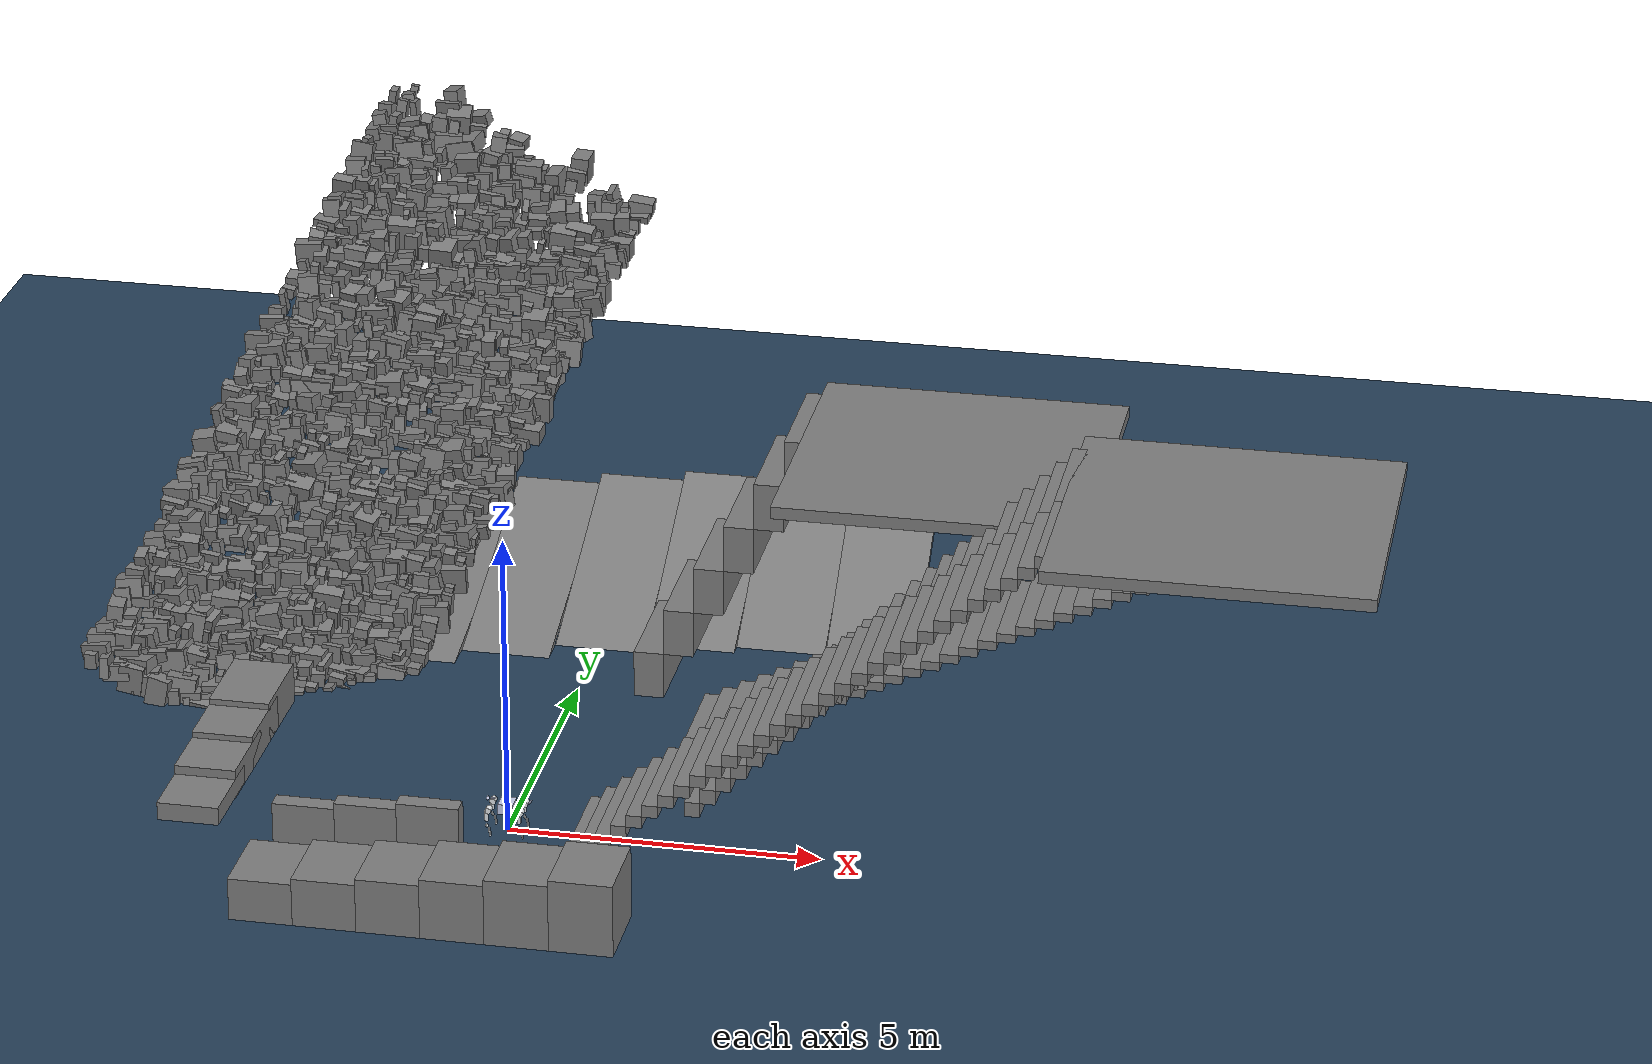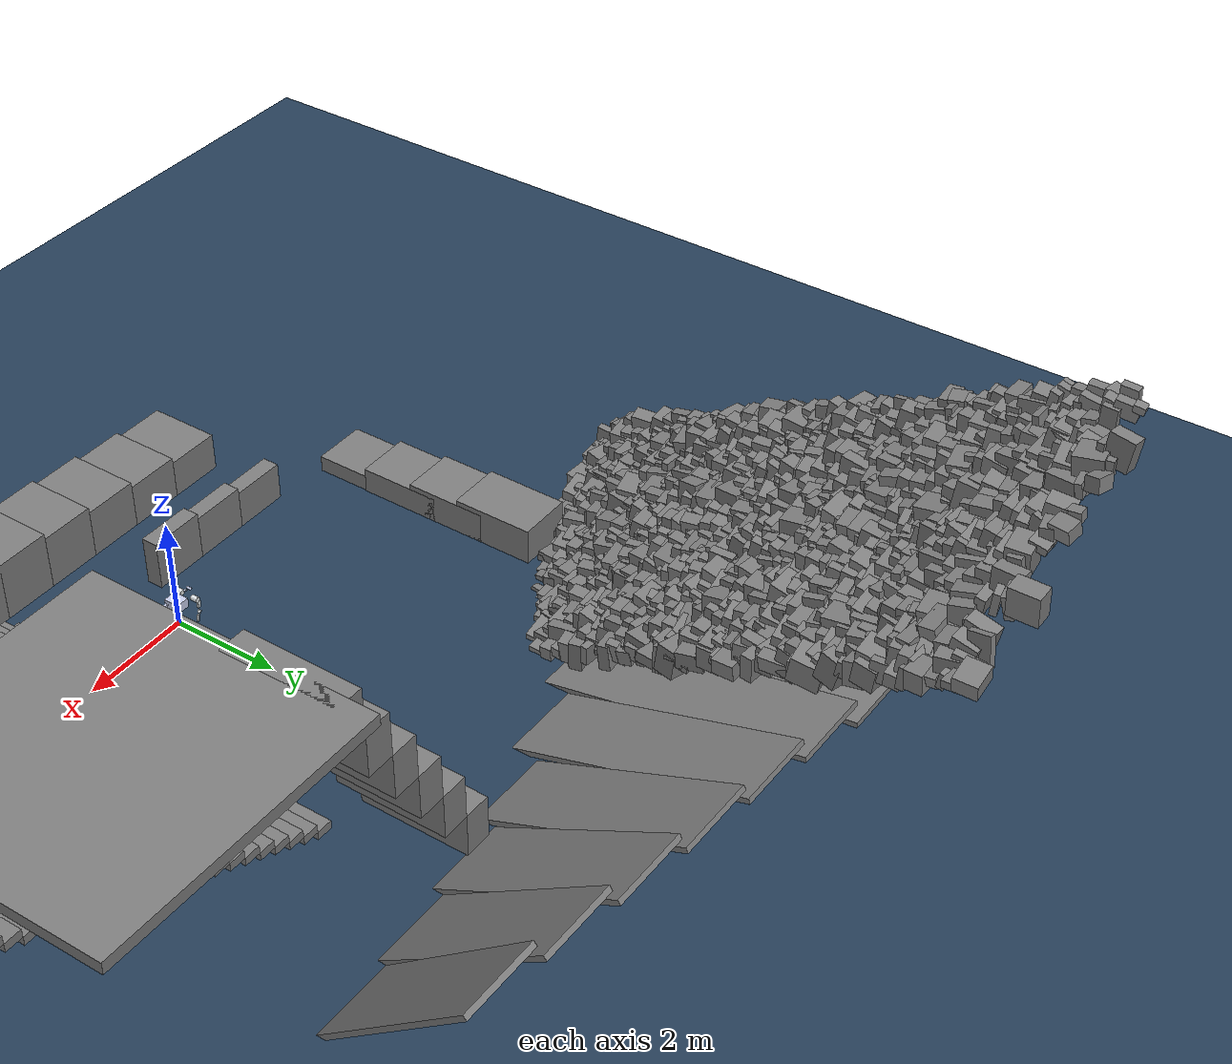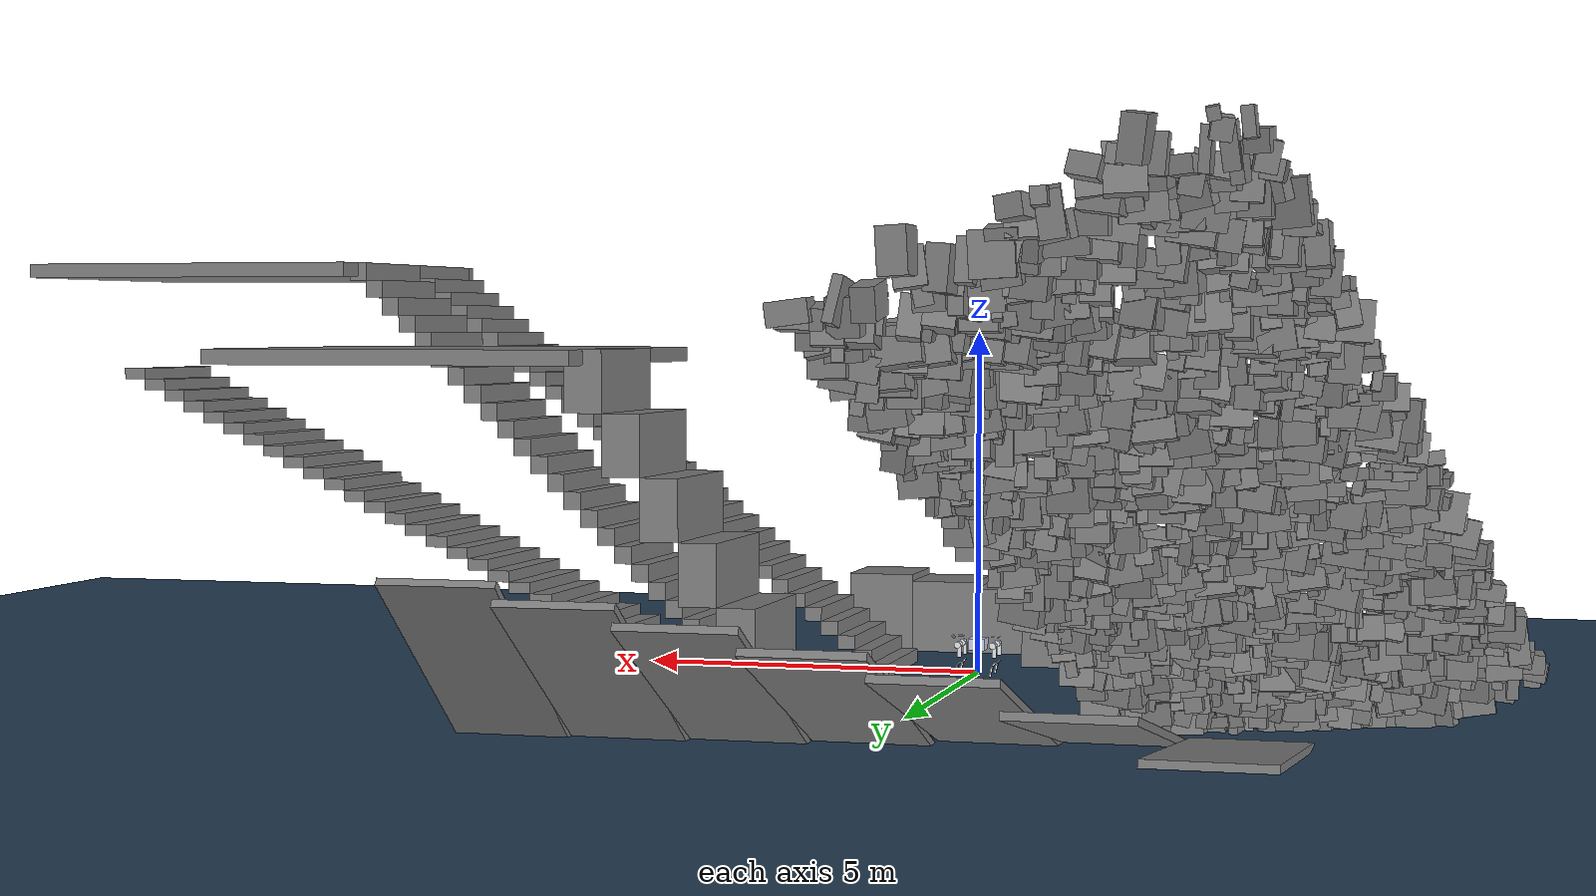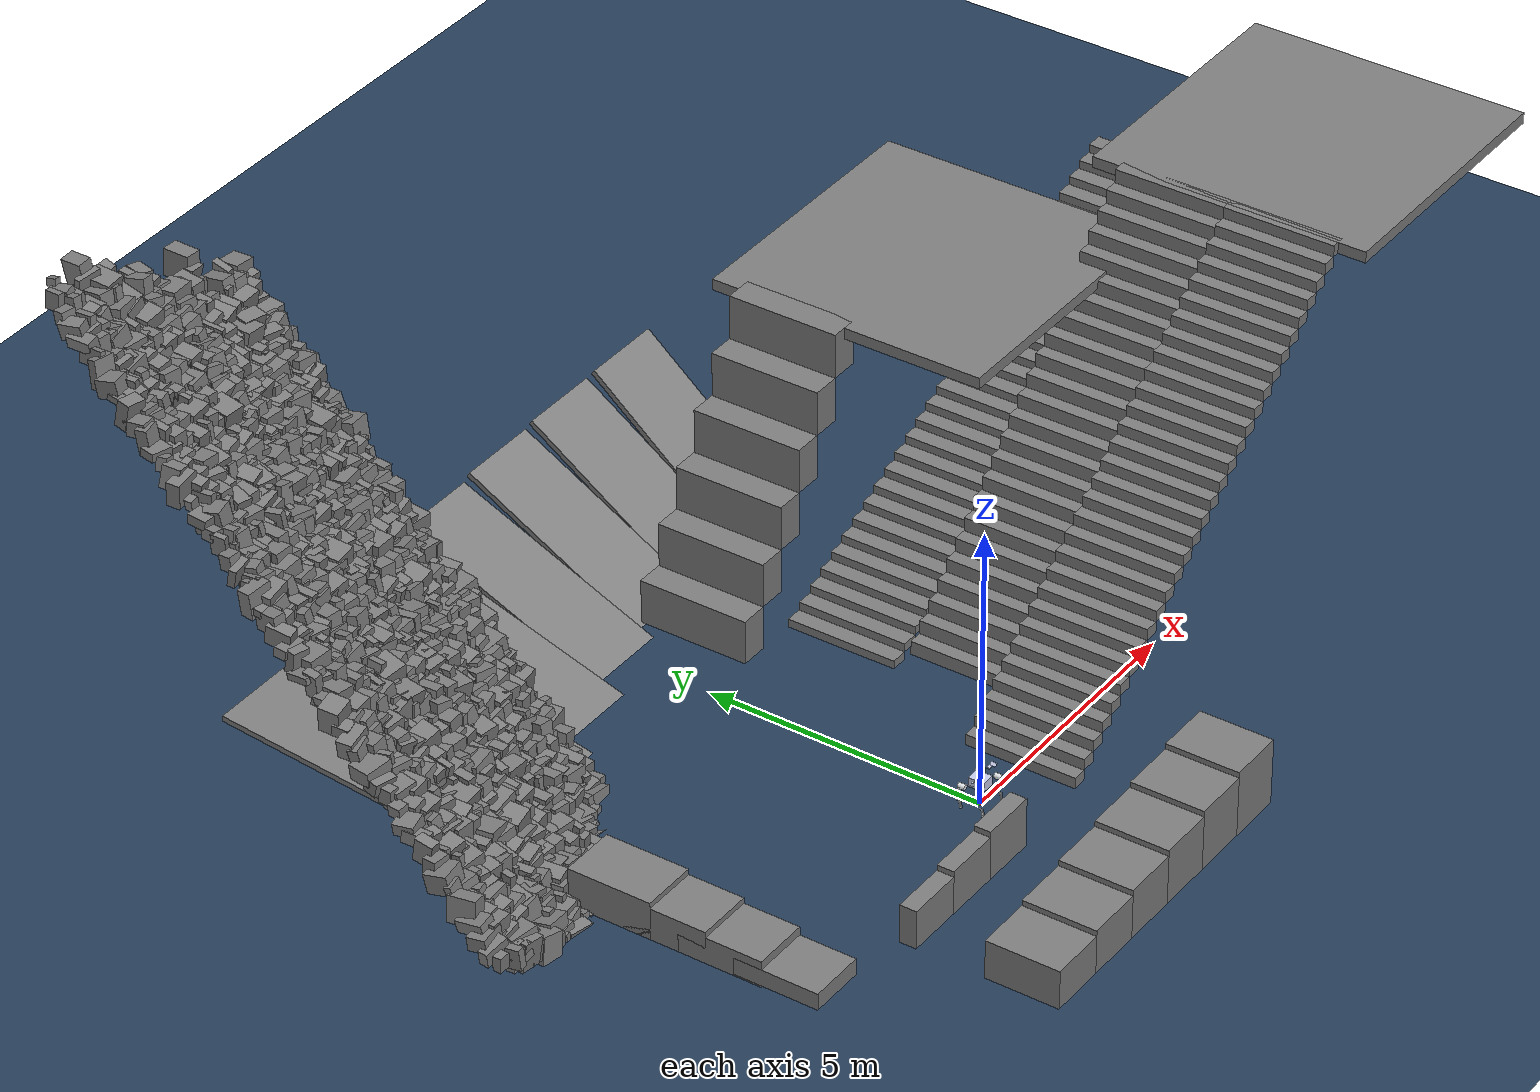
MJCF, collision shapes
<mujoco model="a2 scene">
  <include file="a2.xml" />

  <statistic center="0 0 0.1" extent="3.0" />

  <visual>
    <headlight diffuse="0.6 0.6 0.6" ambient="0.3 0.3 0.3" specular="0 0 0" />
    <rgba haze="0.15 0.25 0.35 1" />
    <global azimuth="-130" elevation="-20" />
  </visual>

  <asset>
    <texture type="skybox" builtin="gradient" rgb1="0.3 0.5 0.7" rgb2="0 0 0" width="512"
      height="3072" />
    <texture type="2d" name="groundplane" builtin="checker" mark="edge" rgb1="0.2 0.3 0.4"
      rgb2="0.1 0.2 0.3" markrgb="0.8 0.8 0.8" width="300" height="300" />
    <material name="groundplane" texture="groundplane" texuniform="true" texrepeat="5 5"
      reflectance="0.2" />
  </asset>

  <worldbody>
    <geom name="floor" size="0 0 0.05" type="plane" material="groundplane" />
    <geom pos="-5.0 0.0 0.15" type="box" size="0.5 0.75 0.15" quat="1.0 0.0 0.0 0.0" />
    <geom pos="-4.5 8.0 0.2" type="box" size="2.5 0.75 0.05"
      quat="0.7065042180310854 0.03532653537124295 -0.03535467804479965 0.7059418336827035" />
    <geom pos="-3.0 8.0 0.4" type="box" size="2.5 0.75 0.05"
      quat="0.703854274290177 0.07056477280176178 -0.0706209878068477 0.7032939993232339" />
    <geom pos="-1.5 8.0 0.5" type="box" size="2.5 0.75 0.05"
      quat="0.6994450614237634 0.10562663504969944 -0.10571078187807807 0.6988882962338909" />
    <geom pos="0.0 8.0 0.5" type="box" size="2.5 0.75 0.05"
      quat="0.6932876001677367 0.14042448571930102 -0.14053635404772424 0.6927357363779519" />
    <geom pos="1.5 8.0 0.5" type="box" size="2.5 0.75 0.05"
      quat="0.6853972809684932 0.17487134830626277 -0.17501065852216943 0.6848516979508653" />
    <geom pos="3.0 8.0 0.5" type="box" size="2.5 0.75 0.05"
      quat="0.6757938255148319 0.20888112359369654 -0.20904752749409825 0.675255886942771" />
    <geom pos="4.5 8.0 0.5" type="box" size="2.5 0.75 0.05"
      quat="0.6645012374440044 0.2423688048553323 -0.2425618865171395 0.6639722878837875" />
    <geom pos="-3.0 -3.0 0.35" type="box" size="0.5 0.65 0.35" quat="1.0 0.0 0.0 0.0" />
    <geom pos="-2.0 -3.0 0.4" type="box" size="0.5 0.65 0.4" quat="1.0 0.0 0.0 0.0" />
    <geom pos="-1.0 -3.0 0.45" type="box" size="0.5 0.65 0.45" quat="1.0 0.0 0.0 0.0" />
    <geom pos="0.0 -3.0 0.5" type="box" size="0.5 0.65 0.5" quat="1.0 0.0 0.0 0.0" />
    <geom pos="1.0 -3.0 0.55" type="box" size="0.5 0.65 0.55" quat="1.0 0.0 0.0 0.0" />
    <geom pos="2.0 -3.0 0.6" type="box" size="0.5 0.65 0.6" quat="1.0 0.0 0.0 0.0" />
    <geom pos="-3.0 -1.0 0.35" type="box" size="0.5 0.15 0.35" quat="1.0 0.0 0.0 0.0" />
    <geom pos="-2.0 -1.0 0.4" type="box" size="0.5 0.15 0.4" quat="1.0 0.0 0.0 0.0" />
    <geom pos="-1.0 -1.0 0.45" type="box" size="0.5 0.15 0.45" quat="1.0 0.0 0.0 0.0" />
    <geom pos="-5.0 1.0 0.2" type="box" size="0.5 0.75 0.25" quat="1.0 0.0 0.0 0.0" />
    <geom pos="-5.0 2.0 0.25" type="box" size="0.5 0.75 0.3" quat="1.0 0.0 0.0 0.0" />
    <geom pos="-5.0 3.0 0.3" type="box" size="0.5 0.75 0.35" quat="1.0 0.0 0.0 0.0" />
    <geom pos="1.25 0.0 0.1" type="box" size="0.125 1.0 0.1" quat="1.0 0.0 0.0 0.0" />
    <geom pos="1.5 0.0 0.30000000000000004" type="box" size="0.125 1.0 0.1" quat="1.0 0.0 0.0 0.0" />
    <geom pos="1.75 0.0 0.5" type="box" size="0.125 1.0 0.1" quat="1.0 0.0 0.0 0.0" />
    <geom pos="2.0 0.0 0.7" type="box" size="0.125 1.0 0.1" quat="1.0 0.0 0.0 0.0" />
    <geom pos="2.25 0.0 0.8999999999999999" type="box" size="0.125 1.0 0.1" quat="1.0 0.0 0.0 0.0" />
    <geom pos="2.5 0.0 1.0999999999999999" type="box" size="0.125 1.0 0.1" quat="1.0 0.0 0.0 0.0" />
    <geom pos="2.75 0.0 1.2999999999999998" type="box" size="0.125 1.0 0.1" quat="1.0 0.0 0.0 0.0" />
    <geom pos="3.0 0.0 1.4999999999999998" type="box" size="0.125 1.0 0.1" quat="1.0 0.0 0.0 0.0" />
    <geom pos="3.25 0.0 1.6999999999999997" type="box" size="0.125 1.0 0.1" quat="1.0 0.0 0.0 0.0" />
    <geom pos="3.5 0.0 1.8999999999999997" type="box" size="0.125 1.0 0.1" quat="1.0 0.0 0.0 0.0" />
    <geom pos="3.75 0.0 2.0999999999999996" type="box" size="0.125 1.0 0.1" quat="1.0 0.0 0.0 0.0" />
    <geom pos="4.0 0.0 2.3" type="box" size="0.125 1.0 0.1" quat="1.0 0.0 0.0 0.0" />
    <geom pos="4.25 0.0 2.5" type="box" size="0.125 1.0 0.1" quat="1.0 0.0 0.0 0.0" />
    <geom pos="4.5 0.0 2.7" type="box" size="0.125 1.0 0.1" quat="1.0 0.0 0.0 0.0" />
    <geom pos="4.75 0.0 2.9000000000000004" type="box" size="0.125 1.0 0.1" quat="1.0 0.0 0.0 0.0" />
    <geom pos="5.0 0.0 3.1000000000000005" type="box" size="0.125 1.0 0.1" quat="1.0 0.0 0.0 0.0" />
    <geom pos="5.25 0.0 3.3000000000000007" type="box" size="0.125 1.0 0.1" quat="1.0 0.0 0.0 0.0" />
    <geom pos="5.5 0.0 3.500000000000001" type="box" size="0.125 1.0 0.1" quat="1.0 0.0 0.0 0.0" />
    <geom pos="5.75 0.0 3.700000000000001" type="box" size="0.125 1.0 0.1" quat="1.0 0.0 0.0 0.0" />
    <geom pos="6.0 0.0 3.9000000000000012" type="box" size="0.125 1.0 0.1" quat="1.0 0.0 0.0 0.0" />
    <geom pos="6.25 0.0 4.100000000000001" type="box" size="0.125 1.0 0.1" quat="1.0 0.0 0.0 0.0" />
    <geom pos="6.5 0.0 4.300000000000002" type="box" size="0.125 1.0 0.1" quat="1.0 0.0 0.0 0.0" />
    <geom pos="6.75 0.0 4.500000000000002" type="box" size="0.125 1.0 0.1" quat="1.0 0.0 0.0 0.0" />
    <geom pos="7.0 0.0 4.700000000000002" type="box" size="0.125 1.0 0.1" quat="1.0 0.0 0.0 0.0" />
    <geom pos="7.25 0.0 4.900000000000002" type="box" size="0.125 1.0 0.1" quat="1.0 0.0 0.0 0.0" />
    <geom pos="7.5 0.0 5.100000000000002" type="box" size="0.125 1.0 0.1" quat="1.0 0.0 0.0 0.0" />
    <geom pos="7.75 0.0 5.3000000000000025" type="box" size="0.125 1.0 0.1" quat="1.0 0.0 0.0 0.0" />
    <geom pos="8.0 0.0 5.500000000000003" type="box" size="0.125 1.0 0.1" quat="1.0 0.0 0.0 0.0" />
    <geom pos="8.25 0.0 5.700000000000003" type="box" size="0.125 1.0 0.1" quat="1.0 0.0 0.0 0.0" />
    <geom pos="8.5 0.0 5.900000000000003" type="box" size="0.125 1.0 0.1" quat="1.0 0.0 0.0 0.0" />
    <geom pos="2.75 2.0 0.125" type="box" size="0.125 1.0 0.125" quat="1.0 0.0 0.0 0.0" />
    <geom pos="3.0 2.0 0.375" type="box" size="0.125 1.0 0.125" quat="1.0 0.0 0.0 0.0" />
    <geom pos="3.25 2.0 0.625" type="box" size="0.125 1.0 0.125" quat="1.0 0.0 0.0 0.0" />
    <geom pos="3.5 2.0 0.875" type="box" size="0.125 1.0 0.125" quat="1.0 0.0 0.0 0.0" />
    <geom pos="3.75 2.0 1.125" type="box" size="0.125 1.0 0.125" quat="1.0 0.0 0.0 0.0" />
    <geom pos="4.0 2.0 1.375" type="box" size="0.125 1.0 0.125" quat="1.0 0.0 0.0 0.0" />
    <geom pos="4.25 2.0 1.625" type="box" size="0.125 1.0 0.125" quat="1.0 0.0 0.0 0.0" />
    <geom pos="4.5 2.0 1.875" type="box" size="0.125 1.0 0.125" quat="1.0 0.0 0.0 0.0" />
    <geom pos="4.75 2.0 2.125" type="box" size="0.125 1.0 0.125" quat="1.0 0.0 0.0 0.0" />
    <geom pos="5.0 2.0 2.375" type="box" size="0.125 1.0 0.125" quat="1.0 0.0 0.0 0.0" />
    <geom pos="5.25 2.0 2.625" type="box" size="0.125 1.0 0.125" quat="1.0 0.0 0.0 0.0" />
    <geom pos="5.5 2.0 2.875" type="box" size="0.125 1.0 0.125" quat="1.0 0.0 0.0 0.0" />
    <geom pos="5.75 2.0 3.125" type="box" size="0.125 1.0 0.125" quat="1.0 0.0 0.0 0.0" />
    <geom pos="6.0 2.0 3.375" type="box" size="0.125 1.0 0.125" quat="1.0 0.0 0.0 0.0" />
    <geom pos="6.25 2.0 3.625" type="box" size="0.125 1.0 0.125" quat="1.0 0.0 0.0 0.0" />
    <geom pos="6.5 2.0 3.875" type="box" size="0.125 1.0 0.125" quat="1.0 0.0 0.0 0.0" />
    <geom pos="6.75 2.0 4.125" type="box" size="0.125 1.0 0.125" quat="1.0 0.0 0.0 0.0" />
    <geom pos="7.0 2.0 4.375" type="box" size="0.125 1.0 0.125" quat="1.0 0.0 0.0 0.0" />
    <geom pos="7.25 2.0 4.625" type="box" size="0.125 1.0 0.125" quat="1.0 0.0 0.0 0.0" />
    <geom pos="7.5 2.0 4.875" type="box" size="0.125 1.0 0.125" quat="1.0 0.0 0.0 0.0" />
    <geom pos="7.75 2.0 5.125" type="box" size="0.125 1.0 0.125" quat="1.0 0.0 0.0 0.0" />
    <geom pos="8.0 2.0 5.375" type="box" size="0.125 1.0 0.125" quat="1.0 0.0 0.0 0.0" />
    <geom pos="8.25 2.0 5.625" type="box" size="0.125 1.0 0.125" quat="1.0 0.0 0.0 0.0" />
    <geom pos="8.5 2.0 5.875" type="box" size="0.125 1.0 0.125" quat="1.0 0.0 0.0 0.0" />
    <geom pos="2.3 4.0 0.075" type="box" size="0.15 1.0 0.075" quat="1.0 0.0 0.0 0.0" />
    <geom pos="2.6 4.0 0.22499999999999998" type="box" size="0.15 1.0 0.075" quat="1.0 0.0 0.0 0.0" />
    <geom pos="2.9 4.0 0.375" type="box" size="0.15 1.0 0.075" quat="1.0 0.0 0.0 0.0" />
    <geom pos="3.2 4.0 0.525" type="box" size="0.15 1.0 0.075" quat="1.0 0.0 0.0 0.0" />
    <geom pos="3.5 4.0 0.675" type="box" size="0.15 1.0 0.075" quat="1.0 0.0 0.0 0.0" />
    <geom pos="3.8 4.0 0.8250000000000001" type="box" size="0.15 1.0 0.075" quat="1.0 0.0 0.0 0.0" />
    <geom pos="4.1 4.0 0.9750000000000001" type="box" size="0.15 1.0 0.075" quat="1.0 0.0 0.0 0.0" />
    <geom pos="4.4 4.0 1.125" type="box" size="0.15 1.0 0.075" quat="1.0 0.0 0.0 0.0" />
    <geom pos="4.699999999999999 4.0 1.275" type="box" size="0.15 1.0 0.075" quat="1.0 0.0 0.0 0.0" />
    <geom pos="5.0 4.0 1.4249999999999998" type="box" size="0.15 1.0 0.075" quat="1.0 0.0 0.0 0.0" />
    <geom pos="5.299999999999999 4.0 1.5749999999999997" type="box" size="0.15 1.0 0.075"
      quat="1.0 0.0 0.0 0.0" />
    <geom pos="5.6 4.0 1.7249999999999996" type="box" size="0.15 1.0 0.075" quat="1.0 0.0 0.0 0.0" />
    <geom pos="5.899999999999999 4.0 1.8749999999999996" type="box" size="0.15 1.0 0.075"
      quat="1.0 0.0 0.0 0.0" />
    <geom pos="6.199999999999999 4.0 2.0249999999999995" type="box" size="0.15 1.0 0.075"
      quat="1.0 0.0 0.0 0.0" />
    <geom pos="6.499999999999999 4.0 2.1749999999999994" type="box" size="0.15 1.0 0.075"
      quat="1.0 0.0 0.0 0.0" />
    <geom pos="6.799999999999999 4.0 2.3249999999999993" type="box" size="0.15 1.0 0.075"
      quat="1.0 0.0 0.0 0.0" />
    <geom pos="7.099999999999999 4.0 2.474999999999999" type="box" size="0.15 1.0 0.075"
      quat="1.0 0.0 0.0 0.0" />
    <geom pos="7.399999999999999 4.0 2.624999999999999" type="box" size="0.15 1.0 0.075"
      quat="1.0 0.0 0.0 0.0" />
    <geom pos="7.699999999999998 4.0 2.774999999999999" type="box" size="0.15 1.0 0.075"
      quat="1.0 0.0 0.0 0.0" />
    <geom pos="7.999999999999998 4.0 2.924999999999999" type="box" size="0.15 1.0 0.075"
      quat="1.0 0.0 0.0 0.0" />
    <geom pos="8.299999999999997 4.0 3.074999999999999" type="box" size="0.15 1.0 0.075"
      quat="1.0 0.0 0.0 0.0" />
    <geom pos="8.599999999999998 4.0 3.2249999999999988" type="box" size="0.15 1.0 0.075"
      quat="1.0 0.0 0.0 0.0" />
    <geom pos="8.899999999999999 4.0 3.3749999999999987" type="box" size="0.15 1.0 0.075"
      quat="1.0 0.0 0.0 0.0" />
    <geom pos="9.199999999999998 4.0 3.5249999999999986" type="box" size="0.15 1.0 0.075"
      quat="1.0 0.0 0.0 0.0" />
    <geom pos="9.499999999999996 4.0 3.6749999999999985" type="box" size="0.15 1.0 0.075"
      quat="1.0 0.0 0.0 0.0" />
    <geom pos="9.799999999999997 4.0 3.8249999999999984" type="box" size="0.15 1.0 0.075"
      quat="1.0 0.0 0.0 0.0" />
    <geom pos="10.099999999999998 4.0 3.9749999999999983" type="box" size="0.15 1.0 0.075"
      quat="1.0 0.0 0.0 0.0" />
    <geom pos="10.399999999999999 4.0 4.124999999999998" type="box" size="0.15 1.0 0.075"
      quat="1.0 0.0 0.0 0.0" />
    <geom pos="10.7 4.0 4.274999999999999" type="box" size="0.15 1.0 0.075" quat="1.0 0.0 0.0 0.0" />
    <geom pos="11.0 4.0 4.424999999999999" type="box" size="0.15 1.0 0.075" quat="1.0 0.0 0.0 0.0" />
    <geom pos="1.2 6.0 0.4" type="box" size="0.25 1.0 0.4" quat="1.0 0.0 0.0 0.0" />
    <geom pos="1.7 6.0 1.2000000000000002" type="box" size="0.25 1.0 0.4" quat="1.0 0.0 0.0 0.0" />
    <geom pos="2.2 6.0 2.0" type="box" size="0.25 1.0 0.4" quat="1.0 0.0 0.0 0.0" />
    <geom pos="2.7 6.0 2.8" type="box" size="0.25 1.0 0.4" quat="1.0 0.0 0.0 0.0" />
    <geom pos="3.2 6.0 3.5999999999999996" type="box" size="0.25 1.0 0.4" quat="1.0 0.0 0.0 0.0" />
    <geom pos="3.7 6.0 4.3999999999999995" type="box" size="0.25 1.0 0.4" quat="1.0 0.0 0.0 0.0" />
    <geom pos="6.2 5.0 4.7" type="box" size="2.5 2.5 0.1" quat="1.0 0.0 0.0 0.0" />
    <geom pos="11 1.0 5.9" type="box" size="2.5 2.5 0.1" quat="1.0 0.0 0.0 0.0" />
    <geom pos="-7.810269149176631 3.2751148441402296 0.6268097013870898" type="box"
      size="0.10102825907424054 0.07228420650981798 0.1330838051795677"
      quat="0.9998232814571422 0.011342523703246012 -0.005370141138312809 -0.013996949541551939" />
    <geom pos="-7.766248305297239 3.4403486867579085 0.7309287882796688" type="box"
      size="0.22863957919713312 0.08840318715318254 0.127969353206475"
      quat="0.9952864598178431 0.012727166276998155 -0.0778885400100897 -0.056358295546615186" />
    <geom pos="-7.712329273150523 3.642735739951109 0.858459291979891" type="box"
      size="0.23492831527196184 0.1588633765353687 0.1235607108350895"
      quat="0.9972392170899962 -0.048799358806733834 -0.020248566312508574 0.0521781758982807" />
    <geom pos="-7.6572285609789885 3.849558272204642 0.9887847317681249" type="box"
      size="0.15375707683397957 0.24304263702187073 0.11660074909106594"
      quat="0.9924955397443884 -0.08257600853600519 -0.08954169461099687 0.010774568573609863" />
    <geom pos="-7.599167741260756 4.067491676068058 1.1261114842915378" type="box"
      size="0.1329317939111506 0.24371050603236405 0.23143540452039849"
      quat="0.9950863471199517 -0.021453547316976324 0.06698258438414866 0.06968673096228667" />
    <geom pos="-7.539303898592788 4.292192792316291 1.2677027871195101" type="box"
      size="0.13529193053960265 0.05766989267372437 0.21668854678154376"
      quat="0.9918618525466295 -0.0889641433096796 -0.07751854583373625 0.04781549664873653" />
    <geom pos="-7.475045625265006 4.533388564278698 1.4196878958673813" type="box"
      size="0.22082795351294832 0.20101245773091353 0.17538758767008192"
      quat="0.9937432145086864 -0.09131219147430555 -0.033941684716016676 0.05463029694904897" />
    <geom pos="-7.4279155873913965 4.71029287992311 1.531160918103336" type="box"
      size="0.16012942070368882 0.1226056389434253 0.16511848222591066"
      quat="0.9987040163208277 -0.021213846042133243 0.022219853955933733 -0.040577562900287446" />
    <geom pos="-7.369008577948126 4.931402487773768 1.6704890975360138" type="box"
      size="0.09606619224201984 0.15995285422851233 0.21729652836577068"
      quat="0.9947877565068095 0.09543079014038168 -0.03514983819740459 0.007400856168540826" />
    <geom pos="-7.3155199612819315 5.132173960766746 1.7970015728917754" type="box"
      size="0.1184415855411031 0.20643443687282306 0.10388772032698276"
      quat="0.9934677456866732 0.05783172133377143 0.05036647527505748 0.08450176599444333" />
    <geom pos="-7.264406659177485 5.324029603941949 1.9178959009914434" type="box"
      size="0.17301969902865422 0.17959350250812547 0.107914658476599"
      quat="0.9932706099966591 -0.030210343163548793 -0.07265338288244025 0.08498421287829361" />
    <geom pos="-7.205116158617495 5.546578659682316 2.058131122211273" type="box"
      size="0.10268456940419798 0.11543279462428785 0.10048939040889787"
      quat="0.9979112228809109 -0.0005343281654198236 -0.04010324908710662 -0.0506422269888937" />
    <geom pos="-7.145868389632048 5.768967320899533 2.198265273752951" type="box"
      size="0.0872567601280222 0.11953875720215154 0.14040186867453244"
      quat="0.9996046937320978 0.013509231513456297 -0.012269937255503016 -0.021387042161591062" />
    <geom pos="-7.097973278789347 5.948743365830009 2.311547863728365" type="box"
      size="0.21199616021959725 0.11894539140367352 0.10825003475760395"
      quat="0.9928252664818275 0.08098380230027268 0.037746480234654656 -0.0794658242905278" />
    <geom pos="-7.041555626784412 6.1605090797673245 2.444988159136403" type="box"
      size="0.24524929308994156 0.20108527526075298 0.13268251583585292"
      quat="0.9956129304313396 -0.015655684220597328 -0.042470471288401986 -0.08189048405063236" />
    <geom pos="-6.976466259315421 6.404824393892648 2.5989389903802236" type="box"
      size="0.1770946631818051 0.08975929793791268 0.18640727038015376"
      quat="0.9886462770345921 -0.0720244196836565 -0.09549324791243166 0.09095087398154887" />
    <geom pos="-6.93237816998537 6.570310644761323 2.7032171277203467" type="box"
      size="0.2273923990332543 0.13838077197069867 0.17141818882346507"
      quat="0.9936547275687532 0.02024017575698736 -0.09792453884203764 0.05149176981001561" />
    <geom pos="-6.878696005115318 6.7718086079947595 2.830187387627231" type="box"
      size="0.130553126949893 0.13883590931338274 0.09551003538646874"
      quat="0.9922536133662647 0.07314107770988931 -0.02992872342123029 0.09585103560944282" />
    <geom pos="-6.824310822268532 6.975945374837758 2.9588204414143746" type="box"
      size="0.18508470777714128 0.17657744576159978 0.23752928352316488"
      quat="0.9939100312882923 0.052427769988999555 -0.0774876825868639 0.05822231261126823" />
    <geom pos="-6.762608648267173 7.207546734776297 3.104759806727544" type="box"
      size="0.09243751164781341 0.13772656415240386 0.07872287221059546"
      quat="0.9931494091546835 -0.06829746685913254 -0.08378766655490986 -0.044377179378732104" />
    <geom pos="-6.701692602244027 7.436197334684308 3.248839804521624" type="box"
      size="0.07227757161649076 0.1303120402854729 0.23738366094483193"
      quat="0.9940941533770553 0.014195711414247029 -0.07861750703745352 -0.0734478290095448" />
    <geom pos="-6.6557082663134315 7.60880121631029 3.3576029868352775" type="box"
      size="0.21064597915543085 0.19683429238055003 0.05851515922452291"
      quat="0.9963139313604495 -0.07144708700624669 0.007544219182672465 -0.046871619262952365" />
    <geom pos="-6.600278022917842 7.816860656028894 3.488707841262749" type="box"
      size="0.15612313272018757 0.08630573071060597 0.18857104933028052"
      quat="0.9943783789195539 0.034687185653168216 0.04012939658894453 -0.09164098547151389" />
    <geom pos="-6.552542357687523 7.996038216039489 3.6016133069009815" type="box"
      size="0.24982032323457953 0.10777800295890683 0.07898157284665745"
      quat="0.9958799961813712 0.05696660180718253 0.06915655395510462 0.013971776171576883" />
    <geom pos="-6.502497216398302 8.183884478646778 3.719981197092274" type="box"
      size="0.1084716106139313 0.21439948107310175 0.17801133502710811"
      quat="0.991527221761935 0.09823084897111285 -0.05147990658272655 0.06763348308128732" />
    <geom pos="-6.4425124363696575 8.409039537688002 3.861858543677136" type="box"
      size="0.1130712946715707 0.21119173160568716 0.16593582923847086"
      quat="0.994290808344882 -0.060019052038446125 -0.0027104899722848264 -0.08818251004251158" />
    <geom pos="-6.397932662580899 8.57637134410055 3.967299624122578" type="box"
      size="0.14485857675402183 0.2347575912737006 0.06131646742080507"
      quat="0.9948170990204127 0.0973067494671882 0.01315560273096552 0.026405797119669706" />
    <geom pos="-6.349939076815094 8.75651701824556 4.080815129193932" type="box"
      size="0.22323113961900715 0.12207567700659225 0.23481687299175774"
      quat="0.9962231561052741 -0.03040090455102165 -0.043592446181623334 -0.0686651795164711" />
    <geom pos="-6.304552670922993 8.926876547669947 4.188164073974926" type="box"
      size="0.09278966106115732 0.07703062682479943 0.10680711402266488"
      quat="0.9923315397337021 -0.07463623192872873 0.09416628077064129 -0.028987233380325314" />
    <geom pos="-6.244116298385566 9.153726675659144 4.331109537286283" type="box"
      size="0.20322490131482943 0.06423818938825285 0.15174524029109746"
      quat="0.9936401187893117 0.08306512574950403 4.194513542415002e-05 0.07602300610464535" />
    <geom pos="-6.196122815728643 9.333871962781206 4.444624798482197" type="box"
      size="0.11693146277429528 0.11308488544113243 0.1344917396449101"
      quat="0.997323822532763 -0.06436162773901996 -0.008360928333540756 -0.03365811582402595" />
    <geom pos="-6.132189119141298 9.573849424113453 4.595842211046562" type="box"
      size="0.05037506717625005 0.1305093406650164 0.19278740179044604"
      quat="0.996662131300332 0.03688396202609224 -0.05787092424917789 0.04421680114712553" />
    <geom pos="-6.0858039441783625 9.74795786966298 4.705553466826336" type="box"
      size="0.10824582075028624 0.11667446593908265 0.09073428191687458"
      quat="0.9947547627636891 0.007181114277330226 0.09529649321808929 -0.036468780306276816" />
    <geom pos="-6.025084760908892 9.975869538046929 4.84916784042175" type="box"
      size="0.14645624067640378 0.16774513556876305 0.0861789385849942"
      quat="0.998674794688667 0.04304689473154066 0.02801243234086094 -0.0033049874235654294" />
    <geom pos="-5.960990416244029 10.216449997795795 5.000765221420797" type="box"
      size="0.08219939346107712 0.06974219126705991 0.1021769613936081"
      quat="0.9950804586575599 0.00842237391523344 -0.09840337458152831 -0.007792322276437761" />
    <geom pos="-5.897995556236947 10.452903501791566 5.149762076656773" type="box"
      size="0.23272816231986718 0.119645889179415 0.21992616594219572"
      quat="0.9978861895449516 0.029530478388442694 -0.02851727689237769 0.05037726153981846" />
    <geom pos="-5.849399435272721 10.63531081377387 5.264702711488291" type="box"
      size="0.12703853058667183 0.15568032342279858 0.19572295313851268"
      quat="0.9902256227458006 0.05258282725440026 0.09319644086519419 0.08945773161490864" />
    <geom pos="-5.794491376703173 10.84141021370769 5.394572482657807" type="box"
      size="0.09830341707804946 0.10161738150391889 0.11957522261320054"
      quat="0.9927850883162104 -0.03075940875978904 0.09792917168311266 0.06197987191969525" />
    <geom pos="-5.7465513782858695 11.021354745786159 5.507961241731054" type="box"
      size="0.20062510534921169 0.13431153299572451 0.07132506067645958"
      quat="0.9948863567182521 0.02139729060835322 0.045666128454105975 -0.08750941596490132" />
    <geom pos="-5.693705503836831 11.219713662430955 5.632953488784489" type="box"
      size="0.14862711506871967 0.10592639325126024 0.22908069052285776"
      quat="0.9961918942433975 -0.060630826136907 -0.03402512871980347 0.05261086752096848" />
    <geom pos="-5.644960365891292 11.402680315086176 5.74824658192118" type="box"
      size="0.12041475858402162 0.2030146613225145 0.14669346462840985"
      quat="0.9960723517058206 -0.0632594551569498 -0.06038271573703855 0.013857818757029938" />
    <geom pos="-5.583914230643018 11.631819209644103 5.892634269667139" type="box"
      size="0.1831971983074277 0.11695321035020702 0.22835954421823212"
      quat="0.9948721560327806 0.06873573702530235 0.04402276142560351 -0.05972259273289825" />
    <geom pos="-5.523401098494546 11.858957457632215 6.035761286531492" type="box"
      size="0.14319317330081088 0.13584597520997752 0.05241482189836805"
      quat="0.9961811846783561 0.040657985882004886 0.05164338273750452 -0.057471179701428614" />
    <geom pos="-5.4724206511542315 12.050314425606015 6.156341383564428" type="box"
      size="0.16296545055602166 0.18371978034843034 0.16133317777202466"
      quat="0.9936286264009482 -0.08009084841766492 -0.019218331386290716 0.07693025760408119" />
    <geom pos="-5.4138736991311065 12.270072544801515 6.294817947114477" type="box"
      size="0.1935121840376472 0.07634120833001624 0.242600765658927"
      quat="0.992331095409519 -0.09434858162825702 0.04627368859071863 -0.06508523620829373" />
    <geom pos="-5.352759732480223 12.499466047002448 6.43936607121467" type="box"
      size="0.055206173774937736 0.23776653384707022 0.14595425936167586"
      quat="0.989961556257945 -0.05339201818233533 0.09989133324297779 -0.08454070657798383" />
    <geom pos="-5.291579639436069 12.729107757031663 6.584070598942782" type="box"
      size="0.11642720866504702 0.22239636070631202 0.10840141619849678"
      quat="0.995537795724722 -0.008400006019316673 -0.09398734460048935 0.0005623498788831843" />
    <geom pos="-5.238826193037982 12.927119741617044 6.708844233097867" type="box"
      size="0.11547603734941175 0.20182103612096386 0.1592047338730951"
      quat="0.9909328839872552 -0.046972372775037935 -0.10022896696212441 0.07615621977414994" />
    <geom pos="-5.182156021013458 13.139833298655434 6.842881794517746" type="box"
      size="0.12883099652443514 0.10358865382208506 0.11805297675909637"
      quat="0.9929655417482319 -0.07052797964381687 -0.0013625852769540564 -0.09509668947636525" />
    <geom pos="-5.11827674698565 13.37960648292607 6.993970485624138" type="box"
      size="0.0624928189435041 0.13517342700043503 0.15137339990418808"
      quat="0.9983103322185476 -0.008552793945603841 0.05604475261678619 -0.012740329883517898" />
    <geom pos="-7.560646370774412 3.32486610249912 0.5582246436389605" type="box"
      size="0.07178450424878266 0.2425481426866247 0.17781999258880304"
      quat="0.9975707838321692 -0.05734945499549921 -0.008159808349623359 0.038690939299642124" />
    <geom pos="-7.495238941105805 3.570375274688095 0.712927762728282" type="box"
      size="0.15470680147373886 0.08193967349798813 0.0799120857885744"
      quat="0.9962766944497093 -0.05643902013753893 -0.02291110511977885 0.061012018196956314" />
    <geom pos="-7.4424384891939885 3.7685636961832065 0.8378125753783074" type="box"
      size="0.2239136783907773 0.23038414008151029 0.19177268515497733"
      quat="0.998123507589077 0.013707367062653722 0.05191223014551608 0.029439633958456408" />
    <geom pos="-7.385550986364412 3.9820930123228164 0.972364172490861" type="box"
      size="0.13701960713217756 0.2429922416053953 0.1153755147211858"
      quat="0.9993367148327579 0.028755011957992117 -0.0006943729144534909 0.022333775337446533" />
    <geom pos="-7.338306110056299 4.159428378218446 1.0841088131667833" type="box"
      size="0.11218854505075385 0.18954887644473914 0.09150366073863603"
      quat="0.9975159928184101 0.04071328854609774 -0.04874198395853673 0.030471153687553383" />
    <geom pos="-7.273791273587134 4.401587169287003 1.236700750808808" type="box"
      size="0.23972427425686765 0.15446564322843856 0.07550841511997843"
      quat="0.9915011140680152 -0.0891353335261657 -0.03655413955895601 -0.08743127586949895" />
    <geom pos="-7.22736404884398 4.5758534502198245 1.346511463671511" type="box"
      size="0.068992393631547 0.1489375246033481 0.11903734046223818"
      quat="0.9927273831648643 -0.093718842989271 -0.023790973114887082 0.07171548495018179" />
    <geom pos="-7.165276576090002 4.808901043075331 1.4933621462327888" type="box"
      size="0.05025984662007542 0.12896315469103245 0.15172945368689147"
      quat="0.9976914103222261 -0.032878430781766325 0.05930940022422272 -0.0036405499062229564" />
    <geom pos="-7.1014370571461605 5.048525005188726 1.6443568077232742" type="box"
      size="0.12680243925030416 0.09870972847274834 0.1758306775389258"
      quat="0.9940534727356197 0.08536224582930292 0.02674362652572386 -0.062094756376724465" />
    <geom pos="-7.049001344863641 5.245344363185897 1.7683789300246078" type="box"
      size="0.19660678250957897 0.05275131379004844 0.18687400090164585"
      quat="0.9954094857327503 -0.07515061353827157 0.05828299243914979 -0.010744011840146325" />
    <geom pos="-6.983387418397835 5.4916286286325775 1.9235704599683308" type="box"
      size="0.13741636321895853 0.17806023515341843 0.2042754550553902"
      quat="0.9974092116650062 0.0040183142650820165 -0.048693282579870975 0.05279850251526914" />
    <geom pos="-6.91910934037641 5.732898738234702 2.0756024112216265" type="box"
      size="0.20156249163349177 0.16115058622155043 0.2195070867261114"
      quat="0.9954255540534037 0.017791020988958548 -0.04202828460318039 -0.08393491051379673" />
    <geom pos="-6.856391300887111 5.968313186323365 2.223944524362615" type="box"
      size="0.23939160730322898 0.05484839346116749 0.09420179219427544"
      quat="0.9922933095234959 -0.02293503477465345 0.0743713542156744 -0.09642029727665875" />
    <geom pos="-6.791718260025744 6.211065803346607 2.376910650580027" type="box"
      size="0.051258584958924186 0.24657899500922617 0.2295706709371192"
      quat="0.9944973737864856 -0.03138050645286807 -0.026356700812736188 0.09641349318852217" />
    <geom pos="-6.730767103564332 6.439848191564867 2.5210736923698702" type="box"
      size="0.1444429934832813 0.2459909666091308 0.20536373925888887"
      quat="0.9981840101257493 -0.05082960211932177 -0.03150200375056536 -0.007256530670336908" />
    <geom pos="-6.67532214767536 6.64796285516384 2.6522133451165457" type="box"
      size="0.14421314740040378 0.18172522695438673 0.0790318133711184"
      quat="0.9954320776154383 0.041367576573299696 0.016902880327220673 0.08436821142651058" />
    <geom pos="-6.614770038990036 6.875247403004218 2.7954325501597204" type="box"
      size="0.14134375520960876 0.20038156798115941 0.12012445192156375"
      quat="0.9927567963764938 -0.0791122610409464 -0.04594526298896975 0.07787314177650853" />
    <geom pos="-6.567585371317993 7.052356773588997 2.9070347840197313" type="box"
      size="0.08430859658465605 0.11582219740403454 0.12297824854937735"
      quat="0.9965048730080388 -0.05032239624625863 0.06235108253132203 0.023622807082139485" />
    <geom pos="-6.5153026588577 7.248601841174662 3.030695027711272" type="box"
      size="0.19420519852819576 0.23656498401151782 0.1871911802267046"
      quat="0.9963172788858692 0.01573238295242238 0.08428685654042932 0.0003126253818407077" />
    <geom pos="-6.4529944631469665 7.482477925696491 3.178067769158484" type="box"
      size="0.15103485391369062 0.11660159813692444 0.1467001489274547"
      quat="0.9882844660932888 0.08774060217941156 0.08244766027848452 -0.09379650378612425" />
    <geom pos="-6.391407196227419 7.713647977713632 3.32373535366553" type="box"
      size="0.22488348920315382 0.1992166194869664 0.2280522270331978"
      quat="0.9993550705043065 -0.01237869327583726 -0.0022690127157812385 -0.03363127400815069" />
    <geom pos="-6.335621214377801 7.9230426946906025 3.4556816086601447" type="box"
      size="0.14081095659307044 0.1658197741051041 0.09246006989156409"
      quat="0.996076382537582 0.014820693941954174 0.04493399786407006 0.07478718485058646" />
    <geom pos="-6.290110124492088 8.093870230031314 3.5633254588182455" type="box"
      size="0.24587830295774032 0.07041470479344153 0.09133282744862808"
      quat="0.9982345711289703 0.049676602207855594 -0.009559995229028504 -0.031122061102459214" />
    <geom pos="-6.225524804148725 8.336293584891703 3.7160841064997756" type="box"
      size="0.17678622257745266 0.06915872669123305 0.14061671549845434"
      quat="0.9974133720452801 0.026405445606479182 -0.030046493217057876 0.05972039813116518" />
    <geom pos="-6.174761858151706 8.52683415364277 3.83614976447916" type="box"
      size="0.2268430506280113 0.0882741740108137 0.1958997619162746"
      quat="0.9936106964449494 -0.07478692516192684 -0.08035352877512951 -0.02622994754839076" />
    <geom pos="-6.113452663120528 8.75696045268768 3.981159647121453" type="box"
      size="0.22792032444504912 0.24067802400555754 0.23665116324535054"
      quat="0.9953147315865639 0.048889461717574266 -0.07365073178941302 0.039165997071648084" />
    <geom pos="-6.065043540019005 8.938665861373895 4.095657990415609" type="box"
      size="0.19151134709953943 0.1996758429379984 0.19602413256346993"
      quat="0.9949626418434186 -0.070938351186771 0.06548348608120522 -0.027000087361337903" />
    <geom pos="-6.018737641691686 9.112476739180995 4.205181739319434" type="box"
      size="0.10695534075159252 0.22333371356371895 0.20265262412724366"
      quat="0.9890666928433833 -0.07459642606515665 -0.10065395648769225 0.07778966107093643" />
    <geom pos="-5.967481740141281 9.304867634576157 4.3264133468257695" type="box"
      size="0.15043519369220454 0.1081654254608917 0.06345893857982877"
      quat="0.9915796348602277 -0.09220645156781289 0.01556788300385479 0.08958481477632271" />
    <geom pos="-5.913737261392313 9.50659949522623 4.453530992916143" type="box"
      size="0.053002828300638044 0.07042887884217838 0.07638709544337806"
      quat="0.9963265652542098 -0.004956171791638916 0.07667130133728614 0.03781961503199303" />
    <geom pos="-5.8513040658104405 9.740944771322205 4.601199386861075" type="box"
      size="0.09317282026181922 0.23781442933560953 0.11278476368566079"
      quat="0.9937600714399375 -0.001430164412310345 0.09423875911181566 0.059648397484837974" />
    <geom pos="-5.7910442079147675 9.967132345167393 4.743727353784293" type="box"
      size="0.17044657054517284 0.24397280306399907 0.2133519519577448"
      quat="0.9916140556991164 -0.07564856923980064 -0.0450285033790267 0.09461126991730842" />
    <geom pos="-5.735311531914392 10.176326976695556 4.875547528589157" type="box"
      size="0.0675028714568391 0.17798068902618613 0.2244657203492219"
      quat="0.9984094038386455 -0.0031365725795499105 0.03001928260738026 0.047620026362367174" />
    <geom pos="-5.676011174748975 10.398913029563788 5.015806062873127" type="box"
      size="0.11510265623277663 0.17784558684457769 0.23109858185913354"
      quat="0.9925880643761363 0.10082300038618375 -0.016326187022583753 0.06585675871515513" />
    <geom pos="-5.6120670745180234 10.638929541351663 5.167048082368603" type="box"
      size="0.15759896773154927 0.05615976357362461 0.22617196318017607"
      quat="0.9938888174634735 0.08982540226882495 -0.05544777130896113 0.03227940961622226" />
    <geom pos="-5.56318782577276 10.822399583783682 5.282658377375569" type="box"
      size="0.1511260058558032 0.16474464131682046 0.06855709707300219"
      quat="0.9925270682772399 0.06914252191089533 0.03843884790314451 -0.0929074021414205" />
    <geom pos="-5.5021578049282285 11.051477992339583 5.427007950972508" type="box"
      size="0.20086699225873145 0.1584152202044596 0.07718899499262534"
      quat="0.9914363689609038 0.09415882350608551 -0.030498440024197992 -0.08519323572713199" />
    <geom pos="-5.45093768165658 11.243734592660866 5.54815493489178" type="box"
      size="0.07073954274789342 0.20809787861723228 0.22853470866833236"
      quat="0.9977486387286026 0.061093997325887515 -0.027498508820066433 0.00300156936249944" />
    <geom pos="-5.4015266321238125 11.42920076873964 5.665023057044344" type="box"
      size="0.24951819605727554 0.09499905678361843 0.16995848793676455"
      quat="0.9952405007726906 -0.06351829538587542 0.00943846428768813 -0.07329861639135433" />
    <geom pos="-5.356642781378168 11.597673939097309 5.771183347125629" type="box"
      size="0.15851946204290585 0.19980465489682436 0.12908741261785844"
      quat="0.9975385782665214 -0.05470468245342191 0.04267470190758472 0.010151473034825139" />
    <geom pos="-5.309397706367642 11.775010050829696 5.8829284577769565" type="box"
      size="0.17266311520430555 0.1047433174297463 0.20255231722116612"
      quat="0.9942914339256103 0.07783592636160021 -0.010897443315734421 -0.07216203100498932" />
    <geom pos="-5.259326046857765 11.962955850545136 6.00135906945828" type="box"
      size="0.057643961834104376 0.19946648216274307 0.24263443764884737"
      quat="0.9957845105501691 0.028726695908428787 -0.04445212172330505 0.07491324559009385" />
    <geom pos="-5.206403045538666 12.161604265708961 6.126533738713974" type="box"
      size="0.14594875169094926 0.08738018455333386 0.07056701475454143"
      quat="0.9967391355024067 0.014982857557053806 0.07243618082232958 0.03224297512971721" />
    <geom pos="-5.157458982568156 12.34531759069874 6.24229733377963" type="box"
      size="0.10568213233425462 0.05741397517779599 0.118394326803851"
      quat="0.9952211081688027 0.05596949428456861 0.03336919734062441 0.072724536668394" />
    <geom pos="-5.097354685491558 12.570921261337368 6.3844573647658915" type="box"
      size="0.16767494800988056 0.07352062354972116 0.2402468230342509"
      quat="0.9976060192911703 -0.04120615323317508 0.010688495905671988 -0.05449806661730581" />
    <geom pos="-5.049736762560382 12.749656871334933 6.497084343678403" type="box"
      size="0.15962258067230645 0.05689105567995181 0.22162460939617673"
      quat="0.9987484093328136 0.03917524231393392 -0.028208008767725765 0.01308523924810375" />
    <geom pos="-4.986480150396256 12.987092871596346 6.6467003009847145" type="box"
      size="0.06805489902047314 0.2484456653181146 0.20000996260270199"
      quat="0.9962274458074518 -0.05362586826565332 0.06121950089916601 -0.03012167296769296" />
    <geom pos="-4.925931756913036 13.21436347429016 6.789910718748576" type="box"
      size="0.08695352411490173 0.13016484342842588 0.23096666663550297"
      quat="0.9945492806169948 -0.08168712162048336 0.06359829001446415 -0.012417732998206829" />
    <geom pos="-4.860433012387427 13.460215400124467 6.944829817784958" type="box"
      size="0.10606128713620555 0.18079428100294676 0.11338867741572786"
      quat="0.9908672813087249 -0.07919798536468305 -0.07520736332205107 0.07907946919508317" />
    <geom pos="-4.809407607328696 13.651741118533618 7.065516249821445" type="box"
      size="0.06428810200798266 0.08562745997884445 0.0671060971703222"
      quat="0.9908425253620647 -0.0927765389640209 0.09156749959859975 0.03519938592140351" />
    <geom pos="-7.3804206486071395 3.2765195812897283 0.4461160673832031" type="box"
      size="0.23107422349615983 0.08295018103662342 0.13584040669133104"
      quat="0.9966851461895829 -0.057624829911592394 -0.05344025297555523 -0.021029448509625258" />
    <geom pos="-7.333354302532603 3.453184827443944 0.5574384443480148" type="box"
      size="0.11278298507183199 0.1629991723678727 0.07142023740594684"
      quat="0.9995932293377987 0.009501432810440942 -0.020676200210749313 0.01719282936067236" />
    <geom pos="-7.277641433145868 3.662305114125609 0.6892117721062335" type="box"
      size="0.20369938785388492 0.17753527167244432 0.07653235608189794"
      quat="0.9982636854398165 0.025523828223894485 -0.041421397954352755 0.033202655261600086" />
    <geom pos="-7.229731674217859 3.8421361411783987 0.8025290080614291" type="box"
      size="0.2484802556934088 0.09892639239316103 0.1288335865375051"
      quat="0.9949538587959987 0.009287128449054067 0.04435120215846409 -0.08951837229989158" />
    <geom pos="-7.173041940206045 4.054923124849362 0.9366128379322249" type="box"
      size="0.05979868057535681 0.1501264088760216 0.08927464158127085"
      quat="0.9947778492967654 -0.07001807425111134 0.04107297324075513 0.06186687882730583" />
    <geom pos="-7.107254995900051 4.301856819067873 1.092213593550626" type="box"
      size="0.09244633151514359 0.18433629753515973 0.05350682493570019"
      quat="0.9948602098916951 -0.08208617469720488 -0.0006990996516754427 0.059283504936105826" />
    <geom pos="-7.061442580019352 4.473815392517912 1.2005701467078111" type="box"
      size="0.2148979900343369 0.1387107253896277 0.05470274310012607"
      quat="0.9947921490741537 -0.05317527851164931 -0.019074611980916405 -0.08483589495852097" />
    <geom pos="-7.016354089482352 4.643056685794141 1.3072144554116436" type="box"
      size="0.057168528330577076 0.1103872161261488 0.19385592823134343"
      quat="0.9978746519506477 -0.05314184915938404 0.02725693180038988 -0.02606113065706912" />
    <geom pos="-6.954037650251078 4.8769637126709 1.4546066946184582" type="box"
      size="0.2216029045160382 0.17925252229760696 0.14938898254265512"
      quat="0.9971957566010216 0.06587161599838838 -0.014636598093741342 -0.032362373505660035" />
    <geom pos="-6.891912523031696 5.110152642935283 1.6015464383655242" type="box"
      size="0.19616659811354742 0.09397166050338138 0.10007205572811939"
      quat="0.9984505754784508 -0.02291754345531985 0.035006775542693935 0.03668460432972435" />
    <geom pos="-6.838532516861392 5.310516442471705 1.7278020257413518" type="box"
      size="0.1012129962046189 0.2422503391159146 0.14258871294150424"
      quat="0.989740349516628 -0.08556683105079071 -0.08766772282882547 -0.07353045856402612" />
    <geom pos="-6.786018748217851 5.507628787866116 1.8520087686978028" type="box"
      size="0.228444499417236 0.24460839738691478 0.16685876390709756"
      quat="0.9922565348770473 0.08757791271327747 0.06016202424049906 0.0643242492211598" />
    <geom pos="-6.722985380318252 5.744226832640544 2.001096703664506" type="box"
      size="0.18332390764608317 0.23775131779306755 0.23583198959917157"
      quat="0.998637058970887 0.027430980106705825 -0.028534783727338444 0.034019581096754396" />
    <geom pos="-6.661520108276275 5.97493897243647 2.146475743151993" type="box"
      size="0.218622876764 0.10143756346968652 0.24915513005580434"
      quat="0.9953882038954219 -0.03407322453262455 0.07497587103536975 -0.04919306534749745" />
    <geom pos="-6.598624163158334 6.211021195789151 2.295238642674498" type="box"
      size="0.19495688910771858 0.21188770660949363 0.10401207842273372"
      quat="0.9963187436922748 0.07270561518956581 0.045407078761813026 -0.0010255172706912937" />
    <geom pos="-6.5540836511766525 6.378205631577249 2.4005868602135925" type="box"
      size="0.14768236189753509 0.20389849424684223 0.2069652742623464"
      quat="0.9922365769655773 -0.09727202940273 -0.04202810749190263 -0.0651027327241937" />
    <geom pos="-6.5095760848278115 6.545266404731193 2.505857154003249" type="box"
      size="0.15873706989371947 0.11486069251083125 0.22149391392843637"
      quat="0.9951859399688728 -0.07315655046266574 -0.05194918632922432 0.03942519565463637" />
    <geom pos="-6.451661364884005 6.762651417764115 2.6428383480646254" type="box"
      size="0.13151013527749753 0.21198002215481632 0.22116206841850033"
      quat="0.9936956587473338 -0.05524275794363527 -0.09352163966425031 0.02776469693681981" />
    <geom pos="-6.388253383565527 7.000655587665705 2.7928123270885106" type="box"
      size="0.1691743957406575 0.22801709622383737 0.2120260781862448"
      quat="0.99839025297808 0.03063825566636915 -0.044088202484983345 0.018287439671315135" />
    <geom pos="-6.330105739802868 7.218914888745708 2.9303444377883983" type="box"
      size="0.11241632434326992 0.15240915032364113 0.18965413454591168"
      quat="0.9967890545563868 -0.016265589332410343 -0.016631263025775306 -0.07661861660472453" />
    <geom pos="-6.2685888369284815 7.4498208267536805 3.075845595678267" type="box"
      size="0.13176884376021036 0.1905580910704281 0.23727621099231477"
      quat="0.9952379445005838 -0.06852005984879259 0.05748192328017566 0.038759046951433423" />
    <geom pos="-6.212132030387837 7.661733508668456 3.2093785002720088" type="box"
      size="0.10661534627601411 0.05916509025752613 0.1593211765139028"
      quat="0.997453817101093 -0.007842845483970599 0.03346185059583276 0.06248741537203069" />
    <geom pos="-6.161407833196067 7.852128632366135 3.3293525087084683" type="box"
      size="0.23494003794476293 0.15250388261157247 0.060995951016394045"
      quat="0.9980391645145479 0.0006568228003785994 -0.027705679694794386 0.056122989866558816" />
    <geom pos="-6.099525974255988 8.084404446273947 3.4757168688672415" type="box"
      size="0.13715676167923746 0.07601901831399913 0.09221101498928103"
      quat="0.9993199855313214 0.004729688434205395 0.021220546484411622 -0.029780614028239373" />
    <geom pos="-6.053513533975884 8.257113818600573 3.584546524218455" type="box"
      size="0.053833469266676565 0.14340762412310307 0.06292980801104647"
      quat="0.9967372770846562 0.01465291607269339 -0.07019819288408818 0.037044651924954194" />
    <geom pos="-5.994067363990467 8.480247185205394 3.7251499382534163" type="box"
      size="0.08287083246549551 0.11705598369260756 0.12468715930674602"
      quat="0.9985226211501554 0.021115448915974163 -0.00178591405423045 0.050035221389448784" />
    <geom pos="-5.946858525595079 8.657447281481573 3.8368093412501905" type="box"
      size="0.16399256159416262 0.09030769396634154 0.12960272936698794"
      quat="0.9950990849935974 0.0070449328653676285 -0.05980419759113774 0.07843237798452936" />
    <geom pos="-5.8952673894606304 8.851096492111484 3.9588338531106793" type="box"
      size="0.2203402397412662 0.11593353737809654 0.21877158293811413"
      quat="0.9976951963646412 -0.022649728266081214 0.017494053887588432 0.061524328838043464" />
    <geom pos="-5.8502573388120584 9.02004335840638 4.065292634031779" type="box"
      size="0.15054389265318835 0.06308035863794191 0.10138686135442154"
      quat="0.9976545437409609 0.02619095259328261 -4.593610834062391e-05 0.06324115151660237" />
    <geom pos="-5.804746185987243 9.190871129991306 4.172936633054856" type="box"
      size="0.21115016575147244 0.12792937973669816 0.16466884540698248"
      quat="0.9997683909916387 -0.014705621827691518 0.0020280114411333635 0.015581919979448923" />
    <geom pos="-5.745178148181273 9.414461931904208 4.313828291591277" type="box"
      size="0.18477610179283635 0.1735189965730076 0.06538191088472302"
      quat="0.9941885137804715 0.04223002371607992 0.0989622394605403 0.0035070393312747654" />
    <geom pos="-5.687320971525326 9.631630954107969 4.450673382978087" type="box"
      size="0.13313293256834707 0.20849726979987943 0.18356801788735078"
      quat="0.994004967130185 -0.06815650929442836 -0.03636059331050347 -0.07737391560097512" />
    <geom pos="-5.629723527080715 9.847825061985954 4.586904149915434" type="box"
      size="0.10377711062708307 0.1409551719761948 0.06025277378411423"
      quat="0.9952194137147777 -0.06812183271436513 -0.06038646751242854 -0.03537243297005767" />
    <geom pos="-5.582538208222182 10.024936876822967 4.698507923976332" type="box"
      size="0.15268485741628582 0.11568239203392491 0.1201720081662201"
      quat="0.9949155080194246 -0.0022331638901761995 0.046636356171517054 0.08923673663090312" />
    <geom pos="-5.535083957346211 10.203058137793404 4.81074778207434" type="box"
      size="0.20477938840920407 0.09535295073597697 0.09993595755740065"
      quat="0.9930713852006222 0.02421038211788504 0.08439809733139043 0.07810276858258196" />
    <geom pos="-5.4841938162680215 10.39407613791951 4.931114284711426" type="box"
      size="0.1152979926882687 0.2265645116598383 0.12048610908980155"
      quat="0.9988342720754435 0.04521356503686272 0.01687737924556818 -0.0009922368558235915" />
    <geom pos="-5.438140493772028 10.566938963134152 5.040040635596243" type="box"
      size="0.12448396494720121 0.15709782364442879 0.17367197199015763"
      quat="0.9973643231794639 0.030679659825422326 0.029451327230086168 0.05878592217660531" />
    <geom pos="-5.388910914183427 10.751723985160627 5.156479540968302" type="box"
      size="0.08760559112139693 0.18166976152402542 0.060024984728403216"
      quat="0.9946545744443739 0.046968735900242024 -0.09195615963016657 0.000529236134471596" />
    <geom pos="-5.344681488592947 10.917740746836316 5.261091970000357" type="box"
      size="0.14366137613743019 0.18483899154010192 0.083781947398409"
      quat="0.9991646964745916 -0.006676133057595422 -0.004400320412140069 -0.040074627216059054" />
    <geom pos="-5.279624138946922 11.161935880895685 5.41496707197146" type="box"
      size="0.12910208462204897 0.24821907796696982 0.21488095753184633"
      quat="0.9987150519726972 0.018418075333682383 -0.013871448596282867 -0.04512873118111546" />
    <geom pos="-5.2209456140085635 11.382187863826003 5.553754834730486" type="box"
      size="0.14866273995159757 0.2472007792381015 0.14174627232131282"
      quat="0.9956705152675691 0.02555955842775065 0.08927402388710107 0.004133117321985653" />
    <geom pos="-5.1589106933238815 11.615038200573219 5.7004812199592445" type="box"
      size="0.12484094656223359 0.08656321840609454 0.19252671811096206"
      quat="0.9955600045743216 -0.07937301038580359 -0.03308426510367524 0.038283598535434823" />
    <geom pos="-5.10345811618541 11.823181470810082 5.831638898656108" type="box"
      size="0.0655162754121055 0.11694734749870966 0.18487430182749237"
      quat="0.9937118173681633 0.09412160305269585 -0.01869720911070058 -0.05769195986551047" />
    <geom pos="-5.057223402836508 11.9967251532051 5.940994279253011" type="box"
      size="0.10571628941387087 0.11787622854483704 0.13100329430930163"
      quat="0.9948049649988547 -0.03300388254161449 -0.09518883282307769 -0.014591485756660548" />
    <geom pos="-4.994585139599975 12.23184015822015 6.089147703812369" type="box"
      size="0.1626525279257857 0.05224077418891235 0.21725659934675617"
      quat="0.9962636535674843 0.08399826204517485 -0.017372714146799913 -0.01006048492528437" />
    <geom pos="-4.934210424008489 12.458458854614586 6.231947334732836" type="box"
      size="0.11330005837176457 0.11924801332208898 0.09233173807803716"
      quat="0.9971007303343807 -0.03486858929567487 0.04916366395534867 0.04644619676206398" />
    <geom pos="-4.87769626300478 12.670586818597771 6.36561589538851" type="box"
      size="0.15925867421464993 0.1417820645561437 0.17196063156650848"
      quat="0.9981667736312513 -0.03277952117296723 0.04612281442280854 0.021477453293382475" />
    <geom pos="-4.821043305583867 12.883235759993815 6.499612740441974" type="box"
      size="0.162873793706168 0.17316323544315923 0.12600066475297325"
      quat="0.9981341825479239 -0.030261249753423355 0.022049148937811923 -0.048231166519875454" />
    <geom pos="-4.7737470650544065 13.060763923367153 6.611478868925818" type="box"
      size="0.22212413646826443 0.10447001246577675 0.12137652331487096"
      quat="0.9929891247011547 0.07345269566272947 -0.08786941175158351 0.029262026647921838" />
    <geom pos="-4.713030277955388 13.288666597637938 6.755087575045156" type="box"
      size="0.05550826601500172 0.12408644858160742 0.23097842009264405"
      quat="0.9990188903410918 -0.008166732172919048 -0.03150532582328468 -0.030032909816381886" />
    <geom pos="-7.13899263457221 3.2894418894472666 0.3536402477495047" type="box"
      size="0.2053805283452318 0.09560644390544892 0.24374566538693473"
      quat="0.9965764487226899 0.026135760250590872 0.07802445345345711 -0.008030476367272653" />
    <geom pos="-7.07710116113936 3.5217537917042625 0.5000273483221358" type="box"
      size="0.24957560312036192 0.19348511180587985 0.1485748769272798"
      quat="0.9935503434035788 -0.0476941418127039 -0.02479392149297365 -0.09984110083718427" />
    <geom pos="-7.030223135718162 3.6977121694195048 0.6109043050555162" type="box"
      size="0.09572679168861221 0.05859289943899994 0.10855255968730193"
      quat="0.9955788325712648 -0.03834365758539742 -0.08483897153351086 -0.012445921747622579" />
    <geom pos="-6.97257829642849 3.914084175576572 0.7472471713429998" type="box"
      size="0.130249523524373 0.1639558401963407 0.21469242318750256"
      quat="0.9945165970972877 0.046054009290733354 -0.09376169038937446 -0.004950933407699421" />
    <geom pos="-6.925313680536018 4.091493634721854 0.8590385005264121" type="box"
      size="0.2185080809624813 0.1373285700574219 0.1883239199715967"
      quat="0.9991376315426829 -0.025078881743360277 -0.021007903988662598 0.025567770645572505" />
    <geom pos="-6.863574332118381 4.323234530187371 1.0050657916024146" type="box"
      size="0.20791993662999136 0.1760983216207796 0.06650975078417608"
      quat="0.993167427114982 0.04045671409763734 -0.05829047079577668 -0.09264953867470534" />
    <geom pos="-6.817867479320623 4.494796868756481 1.1131726645890994" type="box"
      size="0.10768637478661863 0.2301767469689488 0.10055876313593903"
      quat="0.9943459146560724 0.06880115265421112 0.05974603155060787 -0.05452536211878095" />
    <geom pos="-6.773281951716905 4.662150272323278 1.2186273540866848" type="box"
      size="0.2069691601339824 0.19184689765308768 0.1402493903761514"
      quat="0.9922865115150443 0.018731835422732615 -0.07436571051337484 -0.09739783625338234" />
    <geom pos="-6.721850552180592 4.855199905807669 1.3402740533639623" type="box"
      size="0.0772245189779968 0.1609802183794862 0.10466632112199811"
      quat="0.9951786106917604 0.06652577592074507 -0.028702575699244778 -0.06610609735864102" />
    <geom pos="-6.662728189492931 5.077117849913496 1.480111591118501" type="box"
      size="0.2477506904460804 0.09533384741870504 0.1482204765852582"
      quat="0.9954073026207751 0.03704091029856248 0.08637478869628014 0.018211774519796692" />
    <geom pos="-6.602729874288318 5.302323713731251 1.6220209514050257" type="box"
      size="0.16571090410477193 0.23639952463695613 0.061978402321502035"
      quat="0.9965658313155994 0.01855041016176473 -0.07694842919520085 -0.024318005293819663" />
    <geom pos="-6.538755743932465 5.542452944687916 1.7733339988251926" type="box"
      size="0.08218299784441523 0.08160948088986729 0.08785418742310028"
      quat="0.9901048918375478 0.09115668385085438 -0.07748142487454643 -0.07334433139706546" />
    <geom pos="-6.490936548032962 5.721944040111045 1.8864370330749411" type="box"
      size="0.18183959450174808 0.07995373409157792 0.13308604287250966"
      quat="0.9972999357238422 0.057424784890307876 -0.04169605090009336 0.018885751900818485" />
    <geom pos="-6.431950768231813 5.943349315372176 2.0259515219241075" type="box"
      size="0.07957973832202024 0.17412399053467353 0.23222484187677525"
      quat="0.9955530570378631 -0.027573747286805766 0.013061032118454623 0.089124679652328" />
    <geom pos="-6.3774453016107575 6.147937571747761 2.154869073590921" type="box"
      size="0.15865327977530902 0.09524734926997935 0.0617753057971646"
      quat="0.9889044286885487 0.09659629152939421 0.058834573140719285 -0.09631033374613657" />
    <geom pos="-6.315614039245292 6.380023469567874 2.30111376159704" type="box"
      size="0.12289755166953584 0.06386545280230173 0.12004423017430982"
      quat="0.9991937606054092 -0.0099121109076967 0.020971865544802633 -0.032768272462025815" />
    <geom pos="-6.2548712054818765 6.608023910943209 2.4447840738709794" type="box"
      size="0.20234798052874187 0.0623214618137434 0.23640180479465778"
      quat="0.9916263900930828 -0.04648273423675288 0.08052763903561928 0.08962007163680233" />
    <geom pos="-6.208503196998717 6.782067921484959 2.5544547271079123" type="box"
      size="0.23223059162285603 0.2245382147964122 0.0616116828684765"
      quat="0.9928275494330193 0.07655596399070372 0.05077776495814733 0.07651313645469383" />
    <geom pos="-6.161923216691012 6.956907575999196 2.6646267408566784" type="box"
      size="0.20827924656882152 0.163821809166948 0.22528414033082675"
      quat="0.9961323788474463 -0.05068646937784525 -0.06872311072571972 0.020695402530934423" />
    <geom pos="-6.113103934536276 7.140152531647126 2.7800952015392735" type="box"
      size="0.19857120016246632 0.19341290473437037 0.052948691760167824"
      quat="0.9929043146998909 -0.023454648991212825 -0.09994655080404209 0.060013234152260425" />
    <geom pos="-6.052379707508114 7.368083131963236 2.923721504745827" type="box"
      size="0.09824433798626805 0.24677370192743567 0.18254221165849252"
      quat="0.9975133275717726 0.027096937826366126 0.061297712381337514 0.021806139822060148" />
    <geom pos="-5.99754256994631 7.5739163273085195 3.0534235319577743" type="box"
      size="0.1314188458927205 0.08339164247771799 0.2166516225369661"
      quat="0.9946552670807629 -0.05500434897006739 -0.08136032669736915 -0.031873476474535235" />
    <geom pos="-5.93991921918386 7.79020767549513 3.1897155730988986" type="box"
      size="0.1782267223023757 0.2227860936748815 0.056765234222518696"
      quat="0.9929433888675256 -0.031715459438749594 0.06017395244545276 0.0971424293702573" />
    <geom pos="-5.8801705010459 8.014476667622237 3.331034580807401" type="box"
      size="0.06200159430237619 0.18877653588525475 0.13783546894826118"
      quat="0.9954107204051172 0.05723373131703317 -0.07503384151877888 -0.015865696613439458" />
    <geom pos="-5.835302979018312 8.18288854754129 3.437156249838649" type="box"
      size="0.1971041939684274 0.23183124340767056 0.06882373830265648"
      quat="0.9958338414656521 0.02524082294637603 0.0582448035924244 -0.06546299644251452" />
    <geom pos="-5.78662655318165 8.365597286790411 3.5522868235548914" type="box"
      size="0.08904985451138882 0.1505345091599045 0.14738217981517668"
      quat="0.9936299844333369 -0.0767485002093566 -0.07459557436359876 0.03527920118122736" />
    <geom pos="-5.736211293178873 8.554832803484539 3.6715301268255613" type="box"
      size="0.16348432479980238 0.15131581338036545 0.13234255967690456"
      quat="0.9900695081108154 0.08658911253916315 0.10097359046763549 0.04548657743733248" />
    <geom pos="-5.67324514481297 8.79117853728824 3.8204590726441037" type="box"
      size="0.1319237200482373 0.1910589936818221 0.23522469306957003"
      quat="0.9915337543423627 -0.08097675801786601 -0.09400523636825386 -0.03829613813432992" />
    <geom pos="-5.621234111772811 8.986403846264285 3.9434767340800834" type="box"
      size="0.09828368538563272 0.1855324471571096 0.08672609410960964"
      quat="0.9950657080714354 0.007325293404900818 -0.08541307469868503 -0.049951810451095646" />
    <geom pos="-5.560164224806895 9.21563189376043 4.087920599921122" type="box"
      size="0.05007675496942597 0.09083377919583625 0.18949309866436598"
      quat="0.9946534432172573 0.059412429253376836 -0.008760929584458944 0.0840115305126789" />
    <geom pos="-5.50742204876996 9.413601574634283 4.212667577165331" type="box"
      size="0.0899989063297019 0.17050890170790062 0.0944770143305679"
      quat="0.9983014629575017 0.049066896064227275 -0.0018875071436398052 -0.03135388467666567" />
    <geom pos="-5.445053195508912 9.64770533948295 4.360183787210491" type="box"
      size="0.19505286774511613 0.09781013712904897 0.09930450246249202"
      quat="0.9954098766960743 0.02715119651755375 0.09109267602776216 0.011140658762966457" />
    <geom pos="-5.397419100063075 9.826501653603986 4.472849017717265" type="box"
      size="0.18766352715468815 0.07764866227673578 0.10423043959812717"
      quat="0.9965616043069389 -0.017793215734509104 -0.0796763794577747 0.014143721275049707" />
    <geom pos="-5.335269219395171 10.059783496839973 4.619847308875749" type="box"
      size="0.06064837728732314 0.08589750627663459 0.20278048540058352"
      quat="0.9959688332465781 -0.021293312583495004 -0.04440788850050769 0.07497077750429512" />
    <geom pos="-5.272111502950397 10.296848288412793 4.769229355809402" type="box"
      size="0.1150655173737164 0.22942702315688202 0.14518770890654256"
      quat="0.9975260307691636 -0.0013944183752191445 -0.02171295367901505 -0.0668462502900927" />
    <geom pos="-5.221726980702146 10.485968429824528 4.888399957453924" type="box"
      size="0.24241845609007295 0.11246792318362919 0.156552335828053"
      quat="0.9920384390878646 0.062240096268360884 0.0592064487271176 -0.09208964229348268" />
    <geom pos="-5.158724415480485 10.722450855624174 5.037415037236174" type="box"
      size="0.1979229402243317 0.2225296302295871 0.19641526638837065"
      quat="0.9967303885823253 -0.01549649660389416 0.07520363764864767 0.025155594883520573" />
    <geom pos="-5.109055646321986 10.90888439171527 5.1548927236256015" type="box"
      size="0.10468585992291536 0.10940266815221458 0.10152998704988017"
      quat="0.9903912451908363 0.07413190982227587 0.08074157788127803 0.08432341902868641" />
    <geom pos="-5.054910632887654 11.112119673911414 5.282957723333803" type="box"
      size="0.14731375134868302 0.1531675219079921 0.06832971388025098"
      quat="0.991643406956124 -0.08623294035223569 -0.07434678693367033 0.06066126203186202" />
    <geom pos="-4.991077526955422 11.351719564551892 5.433937216625448" type="box"
      size="0.2244565017694698 0.2032174056486578 0.1324053063906236"
      quat="0.9972659862201206 -0.02029125738843732 0.031264011184788235 0.06380736012909939" />
    <geom pos="-4.944374175370252 11.527022297654536 5.544401030885662" type="box"
      size="0.1343636585834216 0.16667220240864494 0.06501755021348357"
      quat="0.9878449652461203 -0.10328680157408014 -0.06494881701024227 -0.09631101924212623" />
    <geom pos="-4.894707662428491 11.71344736495384 5.661873380820677" type="box"
      size="0.09388304028202582 0.20693110766043382 0.17195746564227363"
      quat="0.992320573676022 -0.03398472928875683 -0.09721467977300849 0.06851440192464057" />
    <geom pos="-4.8464278869402175 11.89466726265737 5.776065788239999" type="box"
      size="0.1404733245427308 0.09714671898823762 0.15809113581811632"
      quat="0.9950209009379298 0.09614792192397756 -0.012158601580329758 0.023262678564219638" />
    <geom pos="-4.800755267223298 12.066101106109322 5.884091692376376" type="box"
      size="0.07364085238511614 0.14517353861240992 0.18551218294109098"
      quat="0.9944941840534685 -0.05348166786528384 -0.013414441481527963 -0.08911274794277362" />
    <geom pos="-4.75387653064678 12.24206215317199 5.994970331150263" type="box"
      size="0.2174864059293517 0.12441131361868804 0.16463102776782498"
      quat="0.9962266817321752 -0.023972762128616328 -0.08004011372622886 0.023479469234133566" />
    <geom pos="-4.704077537932328 12.428984488128652 6.112756025213849" type="box"
      size="0.10806406528837428 0.22494968223262235 0.09381441302430274"
      quat="0.9943265935632329 0.037719209538458864 0.09209863916519523 0.037546334423631346" />
    <geom pos="-4.646053428205864 12.646780099699425 6.2499959504416935" type="box"
      size="0.2266754760868227 0.14810431972024396 0.2227644118446502"
      quat="0.9922649416424173 -0.0750271670680297 -0.07354552571579594 0.06612310818695102" />
    <geom pos="-4.5982787716360445 12.826104015124558 6.362993639270297" type="box"
      size="0.1663719816575472 0.23765463677172965 0.12253729468966373"
      quat="0.9875060999552115 -0.08348154663101527 0.10640287372762705 -0.08087621644119572" />
    <geom pos="-4.541450682017677 13.039410321609534 6.497404710923653" type="box"
      size="0.11933608596836129 0.1587117839201101 0.1495900543824156"
      quat="0.9898484771423453 -0.07562180320865546 -0.09143555698545056 0.078236015345946" />
    <geom pos="-4.495090248875277 13.213425897833524 6.607057446794781" type="box"
      size="0.13988122246934656 0.19241703749327863 0.09418957296248609"
      quat="0.9936986970559623 0.01386697306043985 0.05319403587138049 -0.09767804807190787" />
    <geom pos="-6.8979164897508385 3.288907070405489 0.2513176407859906" type="box"
      size="0.20348560505537808 0.0787308497033567 0.19088437662827434"
      quat="0.9947826982944735 0.02381944117764923 0.09383836811876706 0.0321617484717179" />
    <geom pos="-6.837031094158627 3.517442622803388 0.3953251434936382" type="box"
      size="0.12160303337941647 0.1476974687688367 0.05369543853615079"
      quat="0.9988742759506152 -0.008159495083408711 -0.014065838899341983 0.04456181841191477" />
    <geom pos="-6.784291396128823 3.7154030023871214 0.520066259699825" type="box"
      size="0.15854889248355808 0.06746161557038971 0.188193108252724"
      quat="0.9959086808760724 0.06095408340734079 -0.06345155510510161 0.020600952075003617" />
    <geom pos="-6.719875287556103 3.95719121469649 0.6724246839076935" type="box"
      size="0.22056834415196122 0.18104967754977383 0.06623098226091634"
      quat="0.9919579718369975 -0.07833978133261789 -0.09735195343700953 0.020121081774753642" />
    <geom pos="-6.668447141981947 4.15022863431528 0.7940636868407258" type="box"
      size="0.09455426180198591 0.1352992364017098 0.13085699827874964"
      quat="0.9929992600469355 -0.038304220009993346 0.10033499989757345 -0.04917462832821603" />
    <geom pos="-6.602532099296991 4.397643150470031 0.9499674236170177" type="box"
      size="0.16003318173104925 0.14040954885544912 0.21460933153689232"
      quat="0.9970468210252144 0.04322019742561466 0.01202270454533516 -0.06233061682208243" />
    <geom pos="-6.555140213093011 4.5755303233701685 1.0620597753946133" type="box"
      size="0.08413388630652369 0.10046099518851156 0.11551684271067866"
      quat="0.9939819839587681 0.07688157990803579 0.0453372631771891 -0.06351039917870191" />
    <geom pos="-6.491190831860782 4.815566657588896 1.2133142856327104" type="box"
      size="0.06848710269993738 0.11909039600694772 0.1512898115878722"
      quat="0.9942558369000715 -0.032464732165337615 -0.09843988273075152 -0.02666386025180263" />
    <geom pos="-6.443622692157688 4.994115404424626 1.32582351613802" type="box"
      size="0.16900181924988603 0.09712119635898792 0.22772384680938695"
      quat="0.999552412749388 0.006679190015098035 0.009028512341989705 -0.0277281184451966" />
    <geom pos="-6.393224611540875 5.18328643766713 1.4450261863398435" type="box"
      size="0.0945168150517055 0.2470026855778506 0.12506312275790743"
      quat="0.9954805543342026 0.09330615437070695 -0.012658479550522048 -0.012336547105571905" />
    <geom pos="-6.340142874843824 5.382530671860007 1.570576300070321" type="box"
      size="0.16956266137543588 0.06522995524155636 0.17866906825482065"
      quat="0.9958366911354687 0.0400274885772684 0.029216287999678257 -0.07650812546441049" />
    <geom pos="-6.2767533708724805 5.6204654863653944 1.7205065760585017" type="box"
      size="0.07209976364631135 0.09706385414314497 0.1360145188034025"
      quat="0.9967828230228534 -0.03825825782655339 -0.05833268825943276 -0.039466529048000236" />
    <geom pos="-6.214350132832077 5.854698315737135 1.868104113754702" type="box"
      size="0.2323366900272465 0.12985154981191216 0.1522869058079509"
      quat="0.994749628707278 -0.07231912220958665 -0.031133948947803327 0.06537429137270451" />
    <geom pos="-6.157087449776369 6.069635884535593 2.003543095549657" type="box"
      size="0.05193689645494423 0.17336164791627282 0.10241180037364372"
      quat="0.991568905628537 -0.09426242542942301 -0.038390736149161594 0.08019882742729817" />
    <geom pos="-6.104864913979306 6.265655076821626 2.127061008048165" type="box"
      size="0.1647908100508524 0.05392207314551144 0.19808459543290646"
      quat="0.9877950823269765 0.09285358115921931 0.08983212653982829 -0.08700159100775907" />
    <geom pos="-6.0514054509791455 6.466317120466124 2.2535045284993958" type="box"
      size="0.117186437887327 0.2251996843477132 0.175921429599736"
      quat="0.992255149437419 -0.030290034612409394 -0.06593155368341092 -0.1008229261973464" />
    <geom pos="-5.995150897494916 6.677470638158963 2.386559059629583" type="box"
      size="0.19390833785294578 0.19330246659036085 0.1378704934860083"
      quat="0.9991879506119694 0.02714697056708996 0.009059333833748979 -0.028362119303249823" />
    <geom pos="-5.933906617737204 6.907353275357938 2.531415403211673" type="box"
      size="0.12043742634860734 0.15727351135365697 0.23926992697436827"
      quat="0.9972085137161318 -0.06925245809516054 -0.0008718154879969562 0.02790192032094941" />
    <geom pos="-5.87892466254025 7.1137300489771915 2.6614599563410937" type="box"
      size="0.2233712923726091 0.1312660111326881 0.1209209801775805"
      quat="0.9991005446310273 -0.03336021848020361 0.02608258155857005 0.0022127991727532545" />
    <geom pos="-5.819515661411149 7.336723900924558 2.8019754577637705" type="box"
      size="0.08908666717510377 0.19729376548340424 0.12026917871639059"
      quat="0.9987344408112243 -0.027336278252276105 -0.005108324699175947 -0.041906439213727824" />
    <geom pos="-5.775469223623288 7.5020538112108985 2.9061550799424776" type="box"
      size="0.14492016627349286 0.18402882201552992 0.09451992919112057"
      quat="0.9967139742512865 -0.0030907519570151265 0.058623426534424164 0.05581213708423329" />
    <geom pos="-5.724406686748197 7.6937189052466834 3.0269293369835166" type="box"
      size="0.18432488983429562 0.10975201107627765 0.2211179376513565"
      quat="0.9891907893754107 -0.07802002130055993 -0.08571985635436086 0.08981405634809703" />
    <geom pos="-5.66233473099058 7.926708254490557 3.1737433183971087" type="box"
      size="0.051316767155726875 0.10235545610568764 0.07085538882619634"
      quat="0.9874299518798887 0.09521047169385632 0.08326509664958573 -0.09478385880648797" />
    <geom pos="-5.605388209007384 8.140459101175269 3.3084345089350133" type="box"
      size="0.06895926298371707 0.13062943606890817 0.1884959779153407"
      quat="0.9930068525370235 0.06239168690045011 -0.0739427205278402 0.06765458078483728" />
    <geom pos="-5.549799935555946 8.349111712470698 3.439913139593621" type="box"
      size="0.18882580283124045 0.060521993387636586 0.23608490028743143"
      quat="0.9922707502583676 -0.07501520055963506 -0.00022697435855436026 0.09885052528608068" />
    <geom pos="-5.490906051308466 8.570172054420379 3.579210275018948" type="box"
      size="0.09171659900204007 0.18612310363823326 0.20836369052815362"
      quat="0.9929596110778659 0.07532450771833113 0.05747570048010412 0.07109130157343548" />
    <geom pos="-5.425792347962969 8.814578714145519 3.7332186660234923" type="box"
      size="0.24092588013839147 0.12885544607928678 0.06536838220135818"
      quat="0.9937190276176733 0.09389599778479588 0.014571412290154274 -0.05910761113810767" />
    <geom pos="-5.370743179078859 9.021207776790298 3.863422194472707" type="box"
      size="0.21771119051851073 0.20722521202711655 0.22335845597268197"
      quat="0.9972360434795593 -0.017678933059432803 -0.06012277208089239 -0.039912168425484444" />
    <geom pos="-5.3052616875737755 9.266994942782983 4.018300486278134" type="box"
      size="0.1835017024735157 0.24177877228925782 0.19481109237823618"
      quat="0.9991883168380369 -0.026593721498490416 0.030233157950447037 0.0011990127504283336" />
    <geom pos="-5.247776183844111 9.482768877105764 4.154266488526778" type="box"
      size="0.23362980836459005 0.14677175834355416 0.06861888269346536"
      quat="0.9979014619041855 0.005839805709935541 -0.049838938618839514 0.0409224778832878" />
    <geom pos="-5.198538986357359 9.667582493190718 4.270723411922337" type="box"
      size="0.062288614650624824 0.15110913392041658 0.16572087108938535"
      quat="0.9910793788855449 -0.0927514780777711 -0.05957586266776936 0.07489689345775298" />
    <geom pos="-5.134403248447573 9.908318323993713 4.422418697152317" type="box"
      size="0.22296818726205714 0.20471183016705177 0.11220966522169609"
      quat="0.9978560495264263 0.011568838360761466 0.060755324545711295 -0.021406936769254058" />
    <geom pos="-5.076893780701448 10.12418220812607 4.558441379629967" type="box"
      size="0.1452884362338793 0.20635789824498643 0.15305368032618824"
      quat="0.9911744745944465 0.0917628437244772 0.04085935048033071 -0.0865058084890562" />
    <geom pos="-5.017521040362813 10.347039953874258 4.698871116218065" type="box"
      size="0.13468302451947808 0.10393105258914116 0.12230655298384342"
      quat="0.9955411821789236 0.08146244852711598 -0.02197966660356472 -0.04217248299252124" />
    <geom pos="-4.968704374577012 10.530275088885997 4.8143333886062" type="box"
      size="0.21392812412109596 0.10368694485199581 0.06944045771933269"
      quat="0.9948102742340157 -0.010318345199413388 -0.09526382029788229 0.03421775230843471" />
    <geom pos="-4.921074481824061 10.709055628046045 4.926988678809537" type="box"
      size="0.24480465820582514 0.20747299651646006 0.1460397575346353"
      quat="0.9961511781135292 0.07576297868973572 -0.0040092951413476215 -0.04389449801006864" />
    <geom pos="-4.86492651080317 10.919809084576464 5.059791118707855" type="box"
      size="0.24878336030876547 0.05444798799362066 0.197398146820421"
      quat="0.9959999029025068 -0.06619495796100332 -0.031480674227094434 0.05110174271926442" />
    <geom pos="-4.820746539844365 11.085640216488914 5.164286576536297" type="box"
      size="0.127729390786425 0.21048788475542454 0.20861590338538635"
      quat="0.9982052847895578 0.0594563253848395 0.006180877718961813 0.003598824885048536" />
    <geom pos="-4.766627257378646 11.28877891655615 5.292290716780646" type="box"
      size="0.138000513691983 0.14031631187971041 0.08519502715708764"
      quat="0.996355940533011 0.053785523392341945 0.06131721845522512 0.02494305432190921" />
    <geom pos="-4.710043082470293 11.501169680283308 5.426124875893297" type="box"
      size="0.05088426980039534 0.06094708711849567 0.08287007184228247"
      quat="0.997825411743806 -0.03591667092018968 0.05390784689494004 0.012181316491543097" />
    <geom pos="-4.651512736179547 11.720865469256832 5.5645621631928215" type="box"
      size="0.1206584296535681 0.0649301116191737 0.12548927222239217"
      quat="0.9921767517137712 0.0682091785772474 0.08628167340912235 0.05906161317004585" />
    <geom pos="-4.593251067108292 11.939552768490318 5.7023639691090535" type="box"
      size="0.1565310362914368 0.16879720228912107 0.06971365917738846"
      quat="0.9905627192909939 0.07878668401524908 0.06534791462001921 0.0911471756420735" />
    <geom pos="-4.547988762331476 12.109446479853423 5.809419387149821" type="box"
      size="0.12170500533933282 0.166233034098338 0.06418905880392235"
      quat="0.9936867688250037 -0.007984421454873717 0.07303751395126515 -0.08478429118635755" />
    <geom pos="-4.4826183704056835 12.35481662952425 5.964034903739449" type="box"
      size="0.2426056423726356 0.17104510974413528 0.09157359920473931"
      quat="0.9960780753756026 0.04243923408401291 -0.07714409670350873 -0.008727399967783865" />
    <geom pos="-4.419989773643765 12.58989535107437 6.112165464936329" type="box"
      size="0.23963321960094028 0.17631854411444212 0.10820347597812519"
      quat="0.9992099555474642 -0.0015314636422481456 0.02863672974614703 -0.02751466996702329" />
    <geom pos="-4.3567096690766824 12.82741953092687 6.26183698700081" type="box"
      size="0.07790593578634332 0.12073873897463565 0.14204872795767315"
      quat="0.9957567507407687 -0.013729646143951843 -0.08780123982748753 0.02389419292850857" />
    <geom pos="-4.296587241024137 13.053091256844821 6.40403990177788" type="box"
      size="0.1260272717446005 0.05315219660267337 0.10760178062791637"
      quat="0.9949763537300348 -0.04947221371893621 0.05301504002215962 -0.06902145405076603" />
    <geom pos="-4.2320203159358485 13.295445564444549 6.556755040589684" type="box"
      size="0.1425160270772159 0.20373233783692937 0.1731086831761592"
      quat="0.9946996443284755 -0.07989477053118205 0.04102900339179678 -0.05006060422378732" />
    <geom pos="-4.167010432336861 13.539462532965624 6.710517874802142" type="box"
      size="0.22106963199887403 0.055705069056190715 0.20665179783163937"
      quat="0.996339076707888 0.031740384245677426 -0.033633842940671684 -0.07190102114610805" />
    <geom pos="-4.1106176467360145 13.751134909948497 6.843899355633725" type="box"
      size="0.1263800176071913 0.19740715967585087 0.23754054028562685"
      quat="0.9954667926876688 -0.05065981961469442 -0.06518173050806421 -0.047231232682482985" />
    <geom pos="-6.666637122570705 3.309369505873534 0.16873318331711096" type="box"
      size="0.1868005930632407 0.15193131814861563 0.23858586556381817"
      quat="0.9917132925650993 -0.04247473600930453 0.0823309886770672 -0.08900702474572485" />
    <geom pos="-6.605263575901768 3.539737351137205 0.3138952718957982" type="box"
      size="0.0581623754865562 0.07517525969377674 0.06506933979726413"
      quat="0.9957939451125213 -0.07373390560651889 -0.05431059087785718 -0.0028442502962362213" />
    <geom pos="-6.547691326514662 3.7558368884481697 0.4500664469182638" type="box"
      size="0.24404801959883998 0.1204639519507459 0.24085895135237306"
      quat="0.9931936262776707 -0.08015767898097631 -0.0819501220109519 -0.020623887222913077" />
    <geom pos="-6.491470390776765 3.966864220704359 0.5830414646011151" type="box"
      size="0.16440619122589842 0.20582669215924793 0.1504780252842507"
      quat="0.990867533078455 0.03681863494600324 -0.09010020180255453 -0.09331598816316844" />
    <geom pos="-6.430017038017087 4.197531621039568 0.7283923123348788" type="box"
      size="0.0656615056927423 0.12270336680278826 0.2474344582190148"
      quat="0.9967466576517972 0.049470086896749976 0.038229880090292545 -0.0508653834221413" />
    <geom pos="-6.3655124667573535 4.43965188127023 0.8809599704734115" type="box"
      size="0.17137076820756245 0.19003258257119277 0.23383328125742164"
      quat="0.9929377191302836 -0.04253341820921923 0.08820169539646458 0.06697802022290025" />
    <geom pos="-6.319887022074492 4.610908651511719 0.9888742951615683" type="box"
      size="0.22622674200810583 0.19172346139925325 0.140928398724711"
      quat="0.9942372779395372 0.031010219395290067 -0.028718347300354222 -0.09851831290055856" />
    <geom pos="-6.2541166373346675 4.857780188794808 1.1444358837227993" type="box"
      size="0.1156012824631414 0.2179739883026749 0.08474314978417487"
      quat="0.9960561210615774 0.023281066593826245 -0.011248294320322396 0.08487444555872845" />
    <geom pos="-6.197153447723123 5.071593598030276 1.2791664969089647" type="box"
      size="0.12713876020834378 0.15211678306119217 0.2060635833655791"
      quat="0.9996513152885386 0.021642712790051602 0.015041321033224182 -0.001612292330265532" />
    <geom pos="-6.1386904509132325 5.291036588271667 1.4174444877063908" type="box"
      size="0.1318232608287325 0.1922099794408049 0.1561303262352482"
      quat="0.9865449326011915 0.09392147610112489 -0.08986333441878797 0.09915862752697319" />
    <geom pos="-6.079964870537441 5.511465195502163 1.556343547041023" type="box"
      size="0.20050750048422702 0.051669742355376885 0.05667714080679288"
      quat="0.9965566230510171 -0.04420550114851465 0.0677313608496268 0.01825468375019756" />
    <geom pos="-6.0197933884687 5.737321047458543 1.6986624854769907" type="box"
      size="0.16478868077119657 0.051678484810796205 0.05383121416359425"
      quat="0.9984558292842228 -0.025630265133665564 0.03498024629401121 0.03471928638010842" />
    <geom pos="-5.9648846219899685 5.943423104555292 1.828533931009176" type="box"
      size="0.11555862091446462 0.24561127638139107 0.1397616312760617"
      quat="0.9951540840238916 0.07985813634261216 -0.05412633332636298 -0.019009659415616192" />
    <geom pos="-5.905977522418015 6.164533050707256 1.9678623236162398" type="box"
      size="0.1643625326062002 0.09693662842347053 0.10058599992193652"
      quat="0.9965524525547264 0.006523650207706537 -0.05311002330359296 0.06340328634873163" />
    <geom pos="-5.854287682611741 6.358552749168354 2.0901202916142667" type="box"
      size="0.1410963753598628 0.18887513720016968 0.09568333214851421"
      quat="0.9962637642290502 0.009969858790506969 0.0850524552448245 -0.011189006063450127" />
    <geom pos="-5.791269649300885 6.5950932350048 2.2391719568678745" type="box"
      size="0.13307499721014668 0.052773597962431876 0.11224097438048086"
      quat="0.995909716877499 0.054474556315971326 -0.007973472125875042 -0.07164343853707847" />
    <geom pos="-5.725697313445998 6.841221388576887 2.3942651157661867" type="box"
      size="0.24335266349812315 0.0805800554014397 0.07296599007358616"
      quat="0.9941579069112412 0.03288046921952538 0.09722358620471404 -0.03341414603515243" />
    <geom pos="-5.673568292980799 7.036889567654956 2.5175618437051543" type="box"
      size="0.24539802113983328 0.13690609978117244 0.1971545560205484"
      quat="0.9970489870137512 -0.02423281757641496 -0.07279977048133447 0.002506285104706652" />
    <geom pos="-5.620606895356026 7.235682104752154 2.642827328763872" type="box"
      size="0.06364484108991621 0.20270049173576554 0.16865636426569264"
      quat="0.9926552486993673 0.07764800178961577 0.0692129442916061 -0.061773079817699555" />
    <geom pos="-5.570046488562964 7.425462435216057 2.762413936477123" type="box"
      size="0.13812917302226607 0.1127975811970098 0.054706838501844574"
      quat="0.9946480877560822 -0.062540633450124 0.05335154369092043 -0.06258964352528365" />
    <geom pos="-5.5178785293003365 7.6212767724900825 2.8858027633327765" type="box"
      size="0.19867972066384001 0.08989549546897774 0.22825206510673343"
      quat="0.9944851208798432 -0.07244937071512637 -0.07573457743470227 0.0038349462020653086" />
    <geom pos="-5.4536118398183335 7.862504134794231 3.0378077781573003" type="box"
      size="0.07362222629271652 0.16048695809634198 0.2162916289673033"
      quat="0.993589735849552 -0.09741748420466952 0.030320054075707224 -0.048682285345873176" />
    <geom pos="-5.406610294579428 8.0389261486491 3.148976886732842" type="box"
      size="0.20947491777081595 0.06967552245442735 0.12167442656788953"
      quat="0.9962830831587296 -0.06968739419890273 0.05032948753005153 0.0055342557281750655" />
    <geom pos="-5.361221318386989 8.20929532578952 3.2563319108458195" type="box"
      size="0.14218007035453414 0.1808238376056937 0.24065827650722027"
      quat="0.993664728425726 -0.04830549143517643 -0.020836556414798528 -0.09931175608460241" />
    <geom pos="-5.29656037441228 8.452002536707607 3.409269425235694" type="box"
      size="0.2294488774050501 0.11603343419755519 0.23884007946258418"
      quat="0.9947077692047017 -0.05831056254457391 0.0411566096424857 0.07390849519694953" />
    <geom pos="-5.247590631426458 8.635812252571219 3.5250937592493132" type="box"
      size="0.20932930939630856 0.2273111750404227 0.16236095350071023"
      quat="0.9959760450173123 -0.05386356592579905 0.03473671492892409 0.06264019997874484" />
    <geom pos="-5.184114353798392 8.874072775161114 3.6752292742358437" type="box"
      size="0.19136129403625898 0.193640590832054 0.17223371057518536"
      quat="0.9973402275591421 -0.0613677346748373 -0.0057197591831197525 0.03890701720827658" />
    <geom pos="-5.1378555204031935 9.047706993029387 3.7846417041070204" type="box"
      size="0.11355749576668607 0.10878402439847054 0.15740117231525788"
      quat="0.997009807062293 0.058022592936877136 -0.02764397632182278 -0.04290260951981538" />
    <geom pos="-5.09165340542293 9.221128316259103 3.893919982311565" type="box"
      size="0.20975950038537586 0.16708720056632612 0.11266584046289344"
      quat="0.9959963925313542 -0.026094080148534517 0.08544900861567936 0.0029583732570419253" />
    <geom pos="-5.02856016640418 9.457951089462323 4.043149525791597" type="box"
      size="0.10917950379378 0.24282862310238396 0.23329278570778475"
      quat="0.9976808847796135 -0.034419524342397326 -0.023403071066606707 -0.05385577735083617" />
    <geom pos="-4.9673148953956385 9.68783744735743 4.188008213902371" type="box"
      size="0.14755697296642778 0.1265049087754675 0.06756746376577726"
      quat="0.9921595911096174 0.08177778250489758 -0.09246388448157601 -0.019549171960882263" />
    <geom pos="-4.919272350071944 9.868166892988167 4.3016395192177175" type="box"
      size="0.16467056343488132 0.0753604157479142 0.13055872707038027"
      quat="0.9978147215039791 0.05514312848381545 -0.022650013655062643 0.02849550512589947" />
    <geom pos="-4.856764648242439 10.102791831001324 4.449484137009982" type="box"
      size="0.13598558210286188 0.1729668863162485 0.23814940100045418"
      quat="0.9976096817704279 0.02854799138809998 -0.02636624224616866 -0.05713804595387918" />
    <geom pos="-4.8009960142587245 10.312121432131075 4.58138936044322" type="box"
      size="0.0921273148606906 0.10485214802866658 0.09398123506171557"
      quat="0.9978654225239599 -0.03438043303732347 0.023508176414955204 0.05029860829972157" />
    <geom pos="-4.747486063941661 10.51297298176047 4.70795229462832" type="box"
      size="0.09423040382889858 0.12775208263993543 0.20457221631298764"
      quat="0.9936589387920505 -0.09855907215250065 0.04837042581658928 0.02425540272632757" />
    <geom pos="-4.687849143848723 10.73682233584913 4.849006875094217" type="box"
      size="0.08625341384746003 0.1848195386597036 0.14873688141091465"
      quat="0.9943366228217841 -0.05912254970846894 -0.04669900424367165 0.07495603800887704" />
    <geom pos="-4.6348636554346 10.935705298602569 4.974329340228023" type="box"
      size="0.11788814937321002 0.1388179740510835 0.1061537284721761"
      quat="0.9991278484222261 -0.010253900923786499 0.025188131867663412 -0.031685296843114" />
    <geom pos="-4.576265826785328 11.15565438506941 5.112926238314893" type="box"
      size="0.05881254735160793 0.22923757797278144 0.23697131716840347"
      quat="0.9977195630518807 -0.06264829382975595 0.024289673228662854 0.006393477788369265" />
    <geom pos="-4.514777582602151 11.38645275163495 5.258359612025781" type="box"
      size="0.24245498386897846 0.17181811650110934 0.23737525378806187"
      quat="0.9932861227501334 0.06876582815457569 0.05194822634818448 0.07717072637664925" />
    <geom pos="-4.465362501861904 11.571934058997991 5.375237268880656" type="box"
      size="0.050849060334922064 0.12550047699036193 0.2383299069299401"
      quat="0.994595009310374 0.08524777689149816 0.025641886972399462 0.053442283095404934" />
    <geom pos="-4.418106603035934 11.74931079831631 5.487007980262941" type="box"
      size="0.08944683714078969 0.15684567342207212 0.18162638630638026"
      quat="0.9991920868871559 0.007837363687161425 -0.03338158358770529 -0.020962325961183373" />
    <geom pos="-4.356312542461226 11.981257057858338 5.633164677759494" type="box"
      size="0.1719189446724092 0.1965377981849261 0.22583942928880274"
      quat="0.9966066448821771 -0.047496381631611226 0.045492376862990035 -0.04949477503687236" />
    <geom pos="-4.307734935415629 12.163594877172002 5.748061523055588" type="box"
      size="0.13401458561618887 0.1932088539103512 0.22043256027962338"
      quat="0.9959113775694198 0.044104582953837686 -0.06899657061504866 -0.038141670566605675" />
    <geom pos="-4.24483879534141 12.399677832300181 5.896824883693053" type="box"
      size="0.1162396845217564 0.07738852117638004 0.20283759021850561"
      quat="0.9979911038827785 -0.027954795269074646 0.04901390525541595 0.028808385652645832" />
    <geom pos="-4.1835081940654 12.6298844804656 6.041885396865553" type="box"
      size="0.19531251001617192 0.14183271603730993 0.06433013896554031"
      quat="0.9957572744367502 -0.05043534369985142 -0.04472528769765841 0.06263685139384531" />
    <geom pos="-4.125233163365057 12.848621933061063 6.179718806006469" type="box"
      size="0.05991108297975724 0.21355680321495346 0.14239506243626734"
      quat="0.9966537470517962 0.06238007314678581 -0.045871714942368795 -0.02618817920479618" />
    <geom pos="-4.073465466977508 13.04293386903884 6.302160922136079" type="box"
      size="0.23865283888205385 0.17003372858594273 0.20871322935404218"
      quat="0.993303158802815 -0.05118573697711945 0.03422690787314481 0.09776182189332507" />
    <geom pos="-4.012759308186867 13.270796649566597 6.445744489942156" type="box"
      size="0.08609165375672409 0.21078779856965246 0.24114022749905675"
      quat="0.9911152366429894 -0.1024349079688579 0.06695481350979371 0.05210307353113907" />
    <geom pos="-3.966918762489737 13.442860809308296 6.554167576371835" type="box"
      size="0.21081452997375036 0.22639585460642617 0.2490339004475705"
      quat="0.9955433263243958 0.06832213881732138 0.02560132747602737 0.05975067187781096" />
    <geom pos="-3.9047195993842427 13.676327635970745 6.7012824314566215" type="box"
      size="0.09275014765594566 0.08497512240342373 0.09654019160993324"
      quat="0.9950451586426914 -0.006319649118547049 -0.06816753091290723 0.07209980600527033" />
    <geom pos="-6.412142308975678 3.260218459220152 0.024626561188233143" type="box"
      size="0.0916176879054427 0.056452607677304076 0.20025987716880123"
      quat="0.9967706674488193 0.012458244244230208 -0.02518272672671468 0.07522538759351531" />
    <geom pos="-6.346606413301466 3.506209833245375 0.1796335309542244" type="box"
      size="0.2468664021772105 0.20565351225867118 0.20553571828381645"
      quat="0.9934878714461656 -0.07328483178137392 0.06851077041474492 0.05401348958659328" />
    <geom pos="-6.29180737731287 3.7119000129463395 0.3092454394709818" type="box"
      size="0.07364177651493273 0.21165903488099994 0.14471524718339354"
      quat="0.9950981619279183 0.0013300133161217517 0.054238450061557864 0.08268052810170919" />
    <geom pos="-6.2318936785297865 3.936788265940546 0.45095466310020227" type="box"
      size="0.2018461776918599 0.15763368296351327 0.20293442835798498"
      quat="0.9953465997633608 0.014301471708761499 0.09519913729698165 -0.004211710387754503" />
    <geom pos="-6.183208912591786 4.119528310064145 0.5661049630111179" type="box"
      size="0.19518920781179783 0.18245233746755096 0.0663143078025694"
      quat="0.9960738001774389 -0.03151889175331689 -0.04968652561854921 -0.06614221975921517" />
    <geom pos="-6.124112514581098 4.341348794808214 0.705881088529551" type="box"
      size="0.05041047416698688 0.10633746709508463 0.15436682866416462"
      quat="0.9910877511452825 0.04400970780867735 0.09426317208445 -0.08320258131187265" />
    <geom pos="-6.077611555956135 4.515891838554936 0.8158661984226242" type="box"
      size="0.0640581829722516 0.21831044714891362 0.23910350554858242"
      quat="0.9924172071159232 0.07084266579550269 0.06914960124632478 -0.07285421312931267" />
    <geom pos="-6.030899906190454 4.691225719180697 0.9263496397254263" type="box"
      size="0.17005642947221872 0.09945990665489784 0.06966489707514832"
      quat="0.9939738300245479 0.07744426115762845 -0.02649460107469892 0.07291397502518147" />
    <geom pos="-5.974485477804019 4.902979333148429 1.0597823105587132" type="box"
      size="0.22768667046112526 0.23413632123541997 0.21782107749570223"
      quat="0.9939205372325671 -0.0008712088044725112 0.07604044840786027 0.07961819433066425" />
    <geom pos="-5.918537697340284 5.112981367123088 1.1921112552629647" type="box"
      size="0.06765626593489013 0.053246447428928576 0.19253930253640406"
      quat="0.9954246262988629 -0.009950733228053895 0.014802378945356982 -0.09387058028771164" />
    <geom pos="-5.868689180225639 5.300089593721669 1.3100140855482274" type="box"
      size="0.12945291619955931 0.203524923500376 0.07367516795698772"
      quat="0.9933795341017085 -0.09021891142957708 0.018258411986980746 -0.06873339537698103" />
    <geom pos="-5.821714168645512 5.476412012520825 1.421120436119141" type="box"
      size="0.23023497426016548 0.22024693465920137 0.15348043382082063"
      quat="0.9959842131416141 0.0683098621376605 0.026011216575193945 0.05169745177174578" />
    <geom pos="-5.759384271411532 5.710369554501451 1.5685445064956829" type="box"
      size="0.056053930921179135 0.10543749952014071 0.12046397535724346"
      quat="0.9974333171706291 0.05739861339102095 0.04089282709857282 0.012647279180536632" />
    <geom pos="-5.711361415456345 5.89062509536957 1.6821292420751992" type="box"
      size="0.056869780562825406 0.19030319631065457 0.2144072573855301"
      quat="0.99670207109152 0.06519544071471453 -0.007965896330448568 -0.047655854703716936" />
    <geom pos="-5.648319822996403 6.1272540113311385 1.831236629956423" type="box"
      size="0.1156847426168732 0.19760960368720168 0.13230862376394353"
      quat="0.9974931420236242 0.051680053648765045 -0.01972781934653095 -0.04412954582283995" />
    <geom pos="-5.5950602631507715 6.327165711196116 1.9572073349847263" type="box"
      size="0.23731814797143663 0.17283294153172127 0.21422188034008946"
      quat="0.9916864154741173 0.05321423789703291 -0.097876599395683 -0.06439308611854785" />
    <geom pos="-5.535288827087233 6.551519975885233 2.0985800756401423" type="box"
      size="0.07611936475276143 0.14204537334697073 0.06533832151694872"
      quat="0.9928720024298422 0.08733283597265964 0.07320416028316096 -0.03491866934986277" />
    <geom pos="-5.4698406898382315 6.7971819454615225 2.2533794772112765" type="box"
      size="0.18052851071690723 0.10598518992465858 0.1998049399470347"
      quat="0.9957837135002281 -0.0014485826132060505 -0.08767884863958905 0.02692799727690185" />
    <geom pos="-5.421509157131461 6.9785961157718805 2.3676943019641836" type="box"
      size="0.1796036727962504 0.1561156938199544 0.13466075466705793"
      quat="0.994715327212566 -0.05028361839144302 0.08398580485901644 -0.03097353890089141" />
    <geom pos="-5.365418789537568 7.189133355738693 2.5003604969454942" type="box"
      size="0.05089472972764229 0.12351701390614717 0.06570518310084796"
      quat="0.9932502006472705 0.06500616435534581 0.04059320210175962 -0.08706566173347861" />
    <geom pos="-5.307911718548349 7.404988243556617 2.6363775105599783" type="box"
      size="0.06868756928753507 0.13472548126092324 0.22178418185941792"
      quat="0.9930624944119757 0.05575033353834308 0.1001302038658323 0.02631966520332697" />
    <geom pos="-5.260430579297719 7.583210431021755 2.7486809656445654" type="box"
      size="0.22273799583738135 0.08113312444204074 0.15711937457202557"
      quat="0.9951545829672349 0.026789571742263204 0.0944058831034341 -0.00609951478693639" />
    <geom pos="-5.213809520734253 7.758204274266809 2.858950138604831" type="box"
      size="0.06445338777387567 0.06816418680903563 0.190948715334588"
      quat="0.9923035158752042 0.08492233598544684 0.06807496079341883 0.05905699743008572" />
    <geom pos="-5.1563601194187925 7.973842696861489 2.994830750613983" type="box"
      size="0.18778422104844897 0.06901273298684328 0.11060831794615213"
      quat="0.9992050876566049 0.03410183641661336 -0.01968926394211385 0.006212120377919122" />
    <geom pos="-5.104643381663504 8.167963357754987 3.1171523382440736" type="box"
      size="0.1167771456292683 0.0648340120596182 0.1690195296108103"
      quat="0.999640687554151 0.017711977892459378 -0.019695616743631683 -0.004106617402449387" />
    <geom pos="-5.045127509697117 8.391358353286902 3.2579206129671485" type="box"
      size="0.08921097913764009 0.1928696629409811 0.1836510324969102"
      quat="0.9908914887378542 -0.056173934728387394 0.08455418323425658 -0.08848240899521896" />
    <geom pos="-4.985137518293526 8.616532973414012 3.399810285612876" type="box"
      size="0.19143539950943808 0.19923794550793908 0.08245408107745682"
      quat="0.9952244282920918 0.05275807404021196 -0.08112791535305898 0.012774361225261162" />
    <geom pos="-4.925236396217824 8.841374019278483 3.5414897625318273" type="box"
      size="0.15779665186366426 0.21195541125454345 0.14795358567274927"
      quat="0.9945625024530211 -0.010775265018821398 0.030017350456084765 -0.09913768733310062" />
    <geom pos="-4.863983263544414 9.071289886219327 3.6863670452286064" type="box"
      size="0.13068614550122637 0.1818986844334895 0.084669666835664"
      quat="0.9924390985277628 0.09554134752880403 -0.020956727777711615 0.07414379398596324" />
    <geom pos="-4.803795805557064 9.297205704368732 3.828723770265449" type="box"
      size="0.2077139439520736 0.18135707791688244 0.06144772393914427"
      quat="0.9945461729146456 0.06773203730424483 -0.027952495620901414 0.07422222747945385" />
    <geom pos="-4.745652239313779 9.515449700331088 3.9662462367250946" type="box"
      size="0.12043348617753888 0.2244153996533083 0.10064959874564822"
      quat="0.9992465369244273 -0.03309085215910705 -0.009935759948245216 -0.017681476809780283" />
    <geom pos="-4.687856811820099 9.732386944802743 4.1029452776088915" type="box"
      size="0.06725173282080502 0.21447606879218467 0.24734785472864654"
      quat="0.9927134160164339 -0.041903739885459756 -0.06250917823491127 0.09411032292469457" />
    <geom pos="-4.629204954587861 9.95253882952577 4.241669965311514" type="box"
      size="0.22858877434676694 0.10853294700722088 0.22709806643830083"
      quat="0.9926179452962212 0.07669580503378685 -0.011791416825581835 0.09321121528750252" />
    <geom pos="-4.569619951605408 10.176193310847188 4.382601750263709" type="box"
      size="0.12835027837125346 0.22882741487607536 0.09692145653391768"
      quat="0.9963446144426497 -0.005830167363516627 -0.06469320879992088 -0.05548159293685656" />
    <geom pos="-4.515312052145401 10.380039991679961 4.51105201165175" type="box"
      size="0.15404195557923764 0.21125021729388757 0.21676590703662513"
      quat="0.9875344126531314 0.1018189643734335 -0.07472525070689026 0.09394050897535015" />
    <geom pos="-4.4553589459673555 10.60507616176805 4.652854442535046" type="box"
      size="0.12487505857028951 0.1545744220740802 0.1912939476796989"
      quat="0.9978960587518878 -0.06453949345279685 -0.005201406418657701 -0.0033249185814248315" />
    <geom pos="-4.393054420553965 10.83893846969497 4.800218502912694" type="box"
      size="0.2062274793002897 0.13084823733792728 0.15539046863936765"
      quat="0.9962405955170057 0.03071501861716539 -0.0573058461495058 0.05724773770515682" />
    <geom pos="-4.337056320387008 11.049129380510465 4.932666464907178" type="box"
      size="0.1420210961709716 0.10048741443719257 0.13469878639495206"
      quat="0.9971337749621639 -0.02350064691925 -0.04907114810960105 0.05257353751924436" />
    <geom pos="-4.275122621030931 11.281599779309962 5.079153439180133" type="box"
      size="0.1159082610783164 0.1511766414845274 0.2412665249994598"
      quat="0.998178485814987 0.02358183741961857 0.029342692016887745 -0.04714460547313521" />
    <geom pos="-4.216975317631972 11.499857802822408 5.2166847448441676" type="box"
      size="0.1423836496723553 0.16927673067448057 0.2078066763447148"
      quat="0.9946067041240914 -0.05457738218601768 -0.07029256198502899 0.05327071610851785" />
    <geom pos="-4.158818462539065 11.71815167896637 5.354238642388877" type="box"
      size="0.22383078448776114 0.10033135445231997 0.08138768578635841"
      quat="0.9932481714609641 0.04386542423014875 -0.08621035643886163 -0.06404427288403511" />
    <geom pos="-4.109481811419245 11.903338597889382 5.470930795747122" type="box"
      size="0.18511382045442562 0.1785490837697357 0.08926676913232298"
      quat="0.9955251827895545 -0.007860426161011139 -0.06466677797673474 -0.06845459778933038" />
    <geom pos="-4.052893227736018 12.11574591011379 5.604775382592951" type="box"
      size="0.21710562671588404 0.184015116390984 0.10490319114373367"
      quat="0.9944909962490246 -0.09244782073579015 0.010122923831748284 0.04835892093422169" />
    <geom pos="-3.988320294443076 12.358122769728755 5.757504732145106" type="box"
      size="0.23846397200745476 0.07692173128344747 0.11118990982266358"
      quat="0.9946136606749615 -0.046638951918191854 -0.06960359465481264 0.061023059361634505" />
    <geom pos="-3.931879405583582 12.569975704046932 5.890999987882517" type="box"
      size="0.09402218905627624 0.1929235959105759 0.2179289177341786"
      quat="0.9975627049342094 -0.031493600450018304 -0.030514076208373042 -0.05427424811260521" />
    <geom pos="-3.8820068004559083 12.75717434588073 6.008959791676249" type="box"
      size="0.050547967511624145 0.06202718792210457 0.09217942262021236"
      quat="0.994278129691141 0.027555888420020533 0.034847766011897756 -0.09714580297290294" />
    <geom pos="-3.8191815512711287 12.992991209470528 6.1575554795926335" type="box"
      size="0.24389850812744665 0.09935910190634968 0.2497594268817303"
      quat="0.9933836779731731 -0.0072335700812048214 -0.07097888643439855 0.08999189675134207" />
    <geom pos="-3.760370250803031 13.213741570193076 6.296657286011435" type="box"
      size="0.21801234281499954 0.24619359324945972 0.14073181224148"
      quat="0.9937206976632523 0.03450013287200714 -0.06732072904314171 -0.08244292151890806" />
    <geom pos="-3.6983992618450765 13.446351936872896 6.443232458486785" type="box"
      size="0.21083613455947028 0.054315439165931304 0.12777169021245957"
      quat="0.9932303297221774 0.07737462389130724 0.05920878258722039 0.06325345652367691" />
    <geom pos="-3.637241099261815 13.675911330117508 6.587885115797111" type="box"
      size="0.1658086418283306 0.11425991388085119 0.11364360553676553"
      quat="0.9874568421038079 0.08495078910399254 -0.10181230732896009 -0.08571232402249589" />
    <geom pos="-6.199408390122734 3.2809862699547843 -0.049890182792010074" type="box"
      size="0.055329924038292205 0.05838534294963055 0.14976233173156223"
      quat="0.9918773245832544 -0.06318943906769343 -0.05521620170256475 0.09559099767978596" />
    <geom pos="-6.152549059013152 3.4568744778897313 0.060942557736408554" type="box"
      size="0.17071408120938414 0.169317418233333 0.09140058734631998"
      quat="0.9985148318278303 -0.0344205955450904 -0.03562027778838184 0.022683673257226047" />
    <geom pos="-6.092929476606887 3.6806587543392872 0.20195613071707635" type="box"
      size="0.15416882319236014 0.05917900408949926 0.24729994016636508"
      quat="0.995482779584316 -0.05821583056080811 0.018412826953992257 0.07270433568063385" />
    <geom pos="-6.039715296655997 3.8804001191146797 0.3278195022009174" type="box"
      size="0.15439978072116692 0.15171302481018048 0.16916691491771324"
      quat="0.9950489128389017 -0.055910936049171155 0.05222509273557377 0.06343633010339071" />
    <geom pos="-5.9922575854035784 4.058534368734287 0.4400675448588801" type="box"
      size="0.09280506681942205 0.08564421923685447 0.24466993165746934"
      quat="0.9950474715947 0.004215373006303308 0.09037616281105061 0.041169273724021314" />
    <geom pos="-5.93395024049181 4.2773931139006 0.5779773842971477" type="box"
      size="0.0725518479425486 0.22419000409116857 0.18880316556586388"
      quat="0.9948402931082186 0.016058356804049642 -0.08571060804048218 0.05185182787943465" />
    <geom pos="-5.883787404470177 4.465681147977454 0.6966236487082579" type="box"
      size="0.08673073324052998 0.12104527496660178 0.08925315015530613"
      quat="0.9962525333247588 0.06340122677821924 -0.05159845258326442 -0.028262589726173286" />
    <geom pos="-5.8338199781947795 4.653235704446662 0.8148077256064806" type="box"
      size="0.23272752520314569 0.1990854846014507 0.1337388259583281"
      quat="0.9896986479932305 0.09460957311237264 -0.07168762061918674 0.08004061397706412" />
    <geom pos="-5.7782896024505686 4.861670994586907 0.9461494153098837" type="box"
      size="0.21657239116153304 0.23362301331665725 0.16872021220785074"
      quat="0.9959594110379426 -0.03619790277079368 -0.05310043181650882 -0.06272884137979458" />
    <geom pos="-5.716966583454918 5.0918491823865235 1.09119199470288" type="box"
      size="0.16408451543273483 0.11742145954362887 0.0928670918298692"
      quat="0.990272787991769 0.0637978883430485 0.09485319604125911 -0.07932531756466546" />
    <geom pos="-5.6635566294203965 5.292325392323267 1.2175184154385887" type="box"
      size="0.11039074854011846 0.1530872629198952 0.09087924696016414"
      quat="0.9952967082964668 0.01658178374229014 0.07467222609122509 -0.05944380163417323" />
    <geom pos="-5.603152769329405 5.519053483659281 1.3603869795827066" type="box"
      size="0.1830676049472125 0.16719172013682548 0.12147113370275886"
      quat="0.9928968166169732 0.07296514680089612 -0.01224465938533275 -0.09317761115601482" />
    <geom pos="-5.557525581445029 5.690316797071222 1.4683054273301719" type="box"
      size="0.09457651711934126 0.2327268116648285 0.19971123821593448"
      quat="0.9973527264676316 0.06538871953206636 0.027296624954306667 -0.016332441080349046" />
    <geom pos="-5.49857499846341 5.911589959786879 1.6077366678726723" type="box"
      size="0.1750752786677786 0.1700844374936312 0.09401652083165976"
      quat="0.9973219375060443 0.05981202948119779 0.024336719155275962 0.03433945543086716" />
    <geom pos="-5.4465636075113775 6.106816612198192 1.7307551758498394" type="box"
      size="0.10557109227550926 0.17835027306483664 0.15107945381875262"
      quat="0.9934756139669252 -0.035507994276178546 -0.0488353004974604 0.09674967814337622" />
    <geom pos="-5.389126280534551 6.322409713322545 1.8666072293625462" type="box"
      size="0.11114151795282047 0.09841062990027186 0.20292792191103737"
      quat="0.9917976005017399 -0.09602032492967298 0.04118508700082694 0.07363019386179306" />
    <geom pos="-5.329038090361001 6.5479529261132825 2.0087291639406004" type="box"
      size="0.0901399382018059 0.09122826097816006 0.13118825658967764"
      quat="0.9966135991290263 -0.03713326007278681 -0.047695895410331327 0.05574546249214308" />
    <geom pos="-5.2794256224675085 6.73417513335329 2.1260736853157614" type="box"
      size="0.06079419881917675 0.0987982434228434 0.1925154765677646"
      quat="0.9940656092685821 -0.07477876611096256 0.06961026125209949 -0.03736458399098473" />
    <geom pos="-5.226912155266631 6.9312863472716675 2.2502797152932628" type="box"
      size="0.22453081871966216 0.19737540311227184 0.2406916396326319"
      quat="0.9934923960728773 0.08114243966248437 0.07932270442929915 -0.009832191668951202" />
    <geom pos="-5.174647068378695 7.1274652566288195 2.3738982705859017" type="box"
      size="0.06999398659402908 0.10502773639772059 0.1630453900837079"
      quat="0.9932332356174436 -0.06199487744786733 -0.04749103697627155 -0.08595915449820345" />
    <geom pos="-5.119303316655579 7.335200046701083 2.5047985529704953" type="box"
      size="0.21596076745737036 0.22415104528204863 0.23748277220344688"
      quat="0.9915800040434797 0.05883465061889504 -0.07264115997594733 -0.08961496161374886" />
    <geom pos="-5.064171262910385 7.5421402206941455 2.6351981225514294" type="box"
      size="0.09214570190526841 0.10934394220051605 0.11717013665584076"
      quat="0.9956301064072449 0.010314894264081992 0.06184738969064637 0.06920400682238541" />
    <geom pos="-5.014087359268595 7.730131979205175 2.7536576943280666" type="box"
      size="0.06552287101951014 0.11113545895052214 0.19520475316930633"
      quat="0.9910911582051843 0.08701383705903352 0.08123374733528496 -0.05973262577216267" />
    <geom pos="-4.962423259616289 7.92405506105981 2.875854781136839" type="box"
      size="0.21674871440998467 0.08724900461262576 0.09263122359449902"
      quat="0.9984920574931102 0.01212934771290949 -0.033671807743125524 -0.04162570612669544" />
    <geom pos="-4.902733166744605 8.148104001112308 3.017035127051159" type="box"
      size="0.1862607383300084 0.21676236868010285 0.1949036996983709"
      quat="0.9887506062717717 -0.08588196655997925 0.06740482636097124 0.10224048024261886" />
    <geom pos="-4.841438768791643 8.378174758784596 3.1620100113123053" type="box"
      size="0.2463909564038339 0.16083975396974654 0.14297881982493493"
      quat="0.9956997979557274 -0.00500688832447565 -0.04754407171648994 -0.07934988761710506" />
    <geom pos="-4.78715497603036 8.581930954244712 3.2904032549960496" type="box"
      size="0.22619485704875764 0.1536548753774441 0.2444178818721228"
      quat="0.9958360318375556 0.04342743140096456 -0.06695437786963258 -0.04406548740268408" />
    <geom pos="-4.73765243678586 8.767740540292433 3.407487770666007" type="box"
      size="0.08026875307207934 0.14724628524835665 0.12847206555041923"
      quat="0.9936083971275592 0.05750245097778345 -0.09179682292058332 -0.03176735102015068" />
    <geom pos="-4.685045693069222 8.965201871013829 3.5319144203498496" type="box"
      size="0.13236972501584582 0.12473490103163666 0.22954193312405033"
      quat="0.9936579100790655 0.04712515273523646 0.08553864360451963 0.05573435356477293" />
    <geom pos="-4.63205179638163 9.164116394528325 3.657256772920581" type="box"
      size="0.24246024091421142 0.15899589306910003 0.12197137363538736"
      quat="0.9960964955293239 0.044282645561242805 0.015380069932083473 -0.07479486844150678" />
    <geom pos="-4.583278888721638 9.347187281819295 3.77261554760849" type="box"
      size="0.12880256501663112 0.18888160422238326 0.0870377335453709"
      quat="0.9927747040653372 0.0890740469891137 0.03199599106079631 -0.0737594582206274" />
    <geom pos="-4.536521067804472 9.52269446754568 3.8832081939539442" type="box"
      size="0.2305501894984868 0.08767094846667997 0.15570073503185758"
      quat="0.9962690668868353 -0.052054355364493585 -0.015230679402414996 -0.06712910588532592" />
    <geom pos="-4.484976239480996 9.716169860118598 4.005123177541695" type="box"
      size="0.11035519606230995 0.09829423226151757 0.17295277186341962"
      quat="0.9932085343605483 0.06955002042391523 -0.09231673193823463 0.013312510531396687" />
    <geom pos="-4.42667169884945 9.935018079316844 4.143026384233509" type="box"
      size="0.1241480929831747 0.1338238713348478 0.15245737371406823"
      quat="0.9977567778129978 0.01962477625494664 -0.060914396946968284 0.019639672343379298" />
    <geom pos="-4.380464778094263 10.108457441197967 4.25231602916465" type="box"
      size="0.060449784600834694 0.16873838109645067 0.23756288443136192"
      quat="0.9965241899850896 -0.028470819897695246 -0.051208642947219295 0.059216771918256125" />
    <geom pos="-4.331458565791323 10.29240404597315 4.3682266212247605" type="box"
      size="0.18654895604232288 0.19436837785912825 0.20267720434008205"
      quat="0.9913916452859041 0.0934211647335288 0.0314623647510392 -0.0861696654363448" />
    <geom pos="-4.27794554980391 10.493267102707982 4.494796806402099" type="box"
      size="0.16257769730960536 0.06123049923106791 0.14501684145673238"
      quat="0.9993560978880691 -0.031681175232727586 -0.008522521969101507 0.014527882471035827" />
    <geom pos="-4.2334210479002845 10.660391444084322 4.6001071565456275" type="box"
      size="0.18970502729247277 0.1468488163758165 0.05093349755220043"
      quat="0.9961201782805169 0.020760431412943668 0.04048160322098965 0.07533149879431966" />
    <geom pos="-4.181496666771876 10.85529150195006 4.722919866937198" type="box"
      size="0.08613800787421767 0.2040459271336515 0.09569524652255869"
      quat="0.995658034064638 0.041339604209497956 -0.0830151601605332 -0.008037382027947152" />
    <geom pos="-4.1328839929883685 11.037760945543095 4.837899652867996" type="box"
      size="0.060568933718855106 0.20861359329835044 0.05109525115977606"
      quat="0.9900245228221773 -0.10079263342943381 0.06926993892254008 0.06995687828045832" />
    <geom pos="-4.0786125391175885 11.241470826527797 4.966263712331283" type="box"
      size="0.11746759619344685 0.07528174427925681 0.12644036156495964"
      quat="0.9987161470456246 0.03857577826259243 0.025764397781751595 -0.020350989379443154" />
    <geom pos="-4.013708360512871 11.485091027498594 5.119776530721382" type="box"
      size="0.22647002731325555 0.09529301624487774 0.10723875168262366"
      quat="0.9971367157964431 -0.039083204205617714 0.04468043002640947 0.04684583580598318" />
    <geom pos="-3.9659462907611953 11.664367697842884 5.23274444892552" type="box"
      size="0.1651618511769624 0.24724082835211353 0.17893167628353268"
      quat="0.9945740067448152 0.03698226167249465 -0.0288019335486061 -0.0928725258244523" />
    <geom pos="-3.9216363707057136 11.830686598427997 5.337547265270886" type="box"
      size="0.16958375125683006 0.22744795941422144 0.23371815841631166"
      quat="0.9951777384813403 -0.0447906431198795 -0.08718956007100129 0.003612164821551702" />
    <geom pos="-3.863094753891324 12.05042469172297 5.476011209865618" type="box"
      size="0.10654710236552313 0.05424673643914932 0.13283966755149787"
      quat="0.995676484172519 0.03332787060443024 0.07743713294244178 0.03900105573546782" />
    <geom pos="-3.810753817669964 12.246888304318796 5.599809165702216" type="box"
      size="0.11563807268352194 0.24037415917888202 0.07432281932876848"
      quat="0.9965523682389635 0.036717128112556834 0.06495666176261525 0.03627481155205211" />
    <geom pos="-3.760581594410641 12.435211573734607 5.7184776330183755" type="box"
      size="0.17700096541008 0.100981211803234 0.21014117016868847"
      quat="0.9961714859133805 0.06663283846766443 0.009184557185772256 0.055839765402188435" />
    <geom pos="-3.710735008712664 12.622312550690298 5.836375895073631" type="box"
      size="0.23517938046944892 0.12190525628098067 0.09308692203541274"
      quat="0.9975726944142481 -0.009848049117559743 -0.06590079166210468 0.020219321105897126" />
    <geom pos="-3.654384087102885 12.833827789656226 5.9696583582549465" type="box"
      size="0.2043636830440945 0.14280089318927225 0.24636537572283596"
      quat="0.997373075128155 0.06027473933417938 -0.04011051440031293 0.0022475413559889575" />
    <geom pos="-3.6041198138265127 13.022496572167418 6.088544544335194" type="box"
      size="0.1992058211957045 0.15474125307389586 0.12490127876746945"
      quat="0.9963965355185045 -0.013915353342834115 0.0003941908518330313 -0.0836669084025344" />
    <geom pos="-5.915980639615767 3.317763815087803 -0.1424042431805883" type="box"
      size="0.23238810886096903 0.10192544145768634 0.18655872342708085"
      quat="0.9936484516929863 0.07864104504868236 0.04014914319808328 -0.06975949241674707" />
    <geom pos="-5.867138684147102 3.5010938758462946 -0.026882155067551095" type="box"
      size="0.21522528329784074 0.13635449689178716 0.15727849355053303"
      quat="0.9924069078643655 -0.055029294910417574 -0.057994418131616335 0.09347167159266188" />
    <geom pos="-5.822561443978622 3.668416172222747 0.07855293280240627" type="box"
      size="0.19752444407645356 0.19147451199797838 0.166586384166867"
      quat="0.998749057186774 0.013190916263476713 -0.02345406247375349 0.04214531350148126" />
    <geom pos="-5.776240339689383 3.8422841261623653 0.18811264718828447" type="box"
      size="0.054494900204667324 0.2174510072351868 0.15927065773223706"
      quat="0.9974767565925451 -0.03509358745248835 0.0189528704603973 0.05873115764773836" />
    <geom pos="-5.7201124232016225 4.052962307271439 0.3208676536552181" type="box"
      size="0.1429940761672068 0.12037902434107785 0.2494427387231553"
      quat="0.9891256344171311 -0.09150713404242566 -0.08391068399700527 0.07884111154342986" />
    <geom pos="-5.65706432034446 4.289615660246358 0.4699904400739089" type="box"
      size="0.22784389150921072 0.059999478610687385 0.19917074580009503"
      quat="0.9975384220853831 0.016049238452079267 -0.06296593247274544 0.026359244229507146" />
    <geom pos="-5.604156131457816 4.488208476404864 0.595130074632266" type="box"
      size="0.18960781816687666 0.20208698907847428 0.1756052554469583"
      quat="0.9941434664748506 0.03908281296744474 -0.05453707503398557 0.08471723108469102" />
    <geom pos="-5.552980166998859 4.680299325012558 0.7161726131377154" type="box"
      size="0.173307100477326 0.18372662678140236 0.09975180515855361"
      quat="0.9946986080887307 -0.0038928010600804124 0.06290064130268089 0.0812590578948555" />
    <geom pos="-5.49165275554855 4.910494000050894 0.8612255816629483" type="box"
      size="0.1193620640445548 0.08355273627803388 0.15798320293557794"
      quat="0.9913434252440573 -0.09157079606243726 -0.08537961799380982 -0.03953888421671392" />
    <geom pos="-5.430865261501149 5.138662075430602 1.0050015254418567" type="box"
      size="0.0888393142612989 0.09908462991870993 0.0675299917508107"
      quat="0.9979460931595469 -0.06377715018204051 -0.0003505134325721766 -0.0059956152801686775" />
    <geom pos="-5.375818148677906 5.345283420575949 1.1352001908498117" type="box"
      size="0.15238891361924597 0.1073209526958255 0.13833497964956612"
      quat="0.9901732175121163 0.07766286126647448 -0.08169322846134332 -0.08277497040271252" />
    <geom pos="-5.318668864982605 5.559795340740278 1.2703709579351141" type="box"
      size="0.11677376047793273 0.24980964416107965 0.1814587585222712"
      quat="0.9955316023693781 -0.08849568879844363 -0.008299912241565375 -0.03188186325686926" />
    <geom pos="-5.272380211877456 5.733541487977158 1.379853918052825" type="box"
      size="0.13085330708219395 0.0687026818135997 0.2351288703877626"
      quat="0.9863793589598191 -0.10013539313910731 -0.08743763435441565 -0.09686755575214771" />
    <geom pos="-5.207096802240791 5.978585146454138 1.5342637021820629" type="box"
      size="0.11022763971195239 0.16198244558098887 0.11933902760558462"
      quat="0.9907748170959946 -0.05519096362908402 0.09330042999976172 -0.08132803393634089" />
    <geom pos="-5.147522638258065 6.202198943194865 1.6751698504890933" type="box"
      size="0.24439641264708062 0.16710200408217687 0.11680758545347109"
      quat="0.999051804190919 0.007889697553760885 0.04280577063515636 -0.0009545761943308337" />
    <geom pos="-5.093299863158922 6.405726106635273 1.8034187738303251" type="box"
      size="0.216447510674175 0.10332582725720797 0.11886852839929907"
      quat="0.9948918514571712 0.07923594892961962 -0.027618940412930882 -0.05611650765872695" />
    <geom pos="-5.038267325582074 6.6122927430618255 1.9335829655387313" type="box"
      size="0.07332478568022448 0.12683682412016947 0.06711633988921933"
      quat="0.994943199846869 -0.07276607609873273 0.06650363657786748 -0.019245611696848176" />
    <geom pos="-4.9831442064764975 6.8191993805593025 2.063961402709726" type="box"
      size="0.17795034407413873 0.11777540639163055 0.13593510552121685"
      quat="0.9927407479184853 -0.07892433695020948 -0.07906400922307791 0.044560508354249045" />
    <geom pos="-4.918356753802632 7.062381446492511 2.2171981383111747" type="box"
      size="0.09465035775250542 0.11095326475435986 0.23514993237701876"
      quat="0.9947470963153537 -0.05796248867587076 0.07948796136207595 0.028288306368063468" />
    <geom pos="-4.8690447528296925 7.247475840190402 2.3338319885893624" type="box"
      size="0.1099424952314684 0.20107415344596422 0.17016721648187003"
      quat="0.9958790183009996 -0.07390709198379138 0.012757104346295583 0.0509899887334271" />
    <geom pos="-4.815169922114512 7.449696981698634 2.4612579460727195" type="box"
      size="0.20208209376311975 0.1539643058111505 0.12724823121175924"
      quat="0.9952452377601853 -0.036364598410857624 -0.06845934417390835 0.058973306617214664" />
    <geom pos="-4.760012056231158 7.656734042493459 2.591718567101539" type="box"
      size="0.2113325174672512 0.08588461811833434 0.17643083980577495"
      quat="0.9966875524221387 -0.012730175234528055 0.07893476332370106 -0.014871739114736113" />
    <geom pos="-4.712419181431846 7.835375633414749 2.704286301610984" type="box"
      size="0.14502440178552034 0.235970508801318 0.15566612572422386"
      quat="0.9978533859181493 0.05906153621877718 0.007481770108276328 0.02728329648724025" />
    <geom pos="-4.65239692506146 8.06067136127119 2.8462522880795564" type="box"
      size="0.054559014410474005 0.07085548360250361 0.2223405114964241"
      quat="0.9984927333751837 0.03510490510868976 0.0049776225320115695 -0.041894275363032814" />
    <geom pos="-4.589499302284796 8.29675988177706 2.9950191556380865" type="box"
      size="0.18835173305118807 0.12861986168499231 0.17938745995638905"
      quat="0.996004060160014 -0.08538878449467889 -0.004547192032110637 0.02576801645280275" />
    <geom pos="-4.527524723739096 8.529383722105372 3.1416028182868496" type="box"
      size="0.126218096082639 0.14070346940697606 0.23455725119309603"
      quat="0.9991521084929065 0.006022547379246077 -0.03816775493990743 0.01421321568441437" />
    <geom pos="-4.470896375352757 8.741940292592833 3.2755414575000064" type="box"
      size="0.11647282284325719 0.06691303569138264 0.1869842497179302"
      quat="0.9975083067973932 -0.06874776921770419 0.01530911522243338 0.004068548745357815" />
    <geom pos="-4.406520320978369 8.983578160008284 3.427805144619965" type="box"
      size="0.2458303651475665 0.2340232307630809 0.09182787174658835"
      quat="0.9964745663606489 -0.019763021983271983 0.07171065409912863 0.03880004699895454" />
    <geom pos="-4.357475132974237 9.16767106149905 3.5438079228823716" type="box"
      size="0.15402911209648576 0.09936770320670069 0.24797446574823287"
      quat="0.9945741838220634 -0.020598424522632233 -0.0708847317640189 -0.07330247325025906" />
    <geom pos="-4.304635252992574 9.36600747769198 3.668785991687175" type="box"
      size="0.0581547240590469 0.0921820895151676 0.11641603400348767"
      quat="0.9902788331969883 -0.08664755229663773 0.09094827419902761 0.05973646811815545" />
    <geom pos="-4.254164664479067 9.555450671968558 3.788160159191893" type="box"
      size="0.18110516517863662 0.12068308843258528 0.2022473131405225"
      quat="0.996555712282011 -0.05928046985970347 0.0565583137796866 -0.012794348506488354" />
    <geom pos="-4.206850187993324 9.733047284668727 3.900069419768382" type="box"
      size="0.23157743388026542 0.24837900898648194 0.15615517913671542"
      quat="0.9911006055789493 -0.08343728141541872 0.09132195004706252 -0.04917429339243766" />
    <geom pos="-4.154822244269568 9.928336068512262 4.023127078732343" type="box"
      size="0.05899433137830591 0.18870230360183418 0.05573644255907026"
      quat="0.9897361483252884 0.09189795117266385 0.08282630420377375 -0.07153269602379338" />
    <geom pos="-4.099542361429857 10.135831124401834 4.153876297001963" type="box"
      size="0.12698232797588005 0.23986952143965487 0.18590882452952845"
      quat="0.9928052320042847 -0.09231729547629552 0.07280897779472459 -0.022674677800315797" />
    <geom pos="-4.038034836379018 10.36670186240718 4.299355274253326" type="box"
      size="0.09704828373469754 0.23708838030812665 0.08254670294818746"
      quat="0.9920187620356813 -0.0716058419070144 -0.09179541610067855 -0.04842500136174449" />
    <geom pos="-3.991424761930105 10.541654476377749 4.409598467339586" type="box"
      size="0.06301849848471666 0.2443959642956816 0.05566848198098834"
      quat="0.9955496592792611 0.06260829041101959 -0.015418861978876621 -0.0687265347302836" />
    <geom pos="-3.9432436874801944 10.722503896134882 4.523557424850089" type="box"
      size="0.22764773057286172 0.10004828900040165 0.18776852395959814"
      quat="0.9978132764505503 -0.06332000019456707 -0.01575832750801602 -0.01053176284050472" />
    <geom pos="-3.8978670806051294 10.892826644591523 4.630883192776293" type="box"
      size="0.15381734637309658 0.08623283811310005 0.1790681462436601"
      quat="0.9887571298662197 0.0937995987700055 -0.07664697434127332 0.08767105984091406" />
    <geom pos="-3.8345817993098805 11.130370255481953 4.780566958954298" type="box"
      size="0.10051355569047374 0.17326952232277582 0.05341054257701813"
      quat="0.9969746631908321 0.027520536639371165 0.035344169129368185 0.0635211045807903" />
    <geom pos="-3.770971452693513 11.369134010907942 4.931019576917788" type="box"
      size="0.20858721893636673 0.22273666241426582 0.2060794025167322"
      quat="0.9954884872019498 0.09270260137327763 0.016785516427844836 -0.011275902857497718" />
    <geom pos="-3.7195546998183993 11.562128667615468 5.052631633583619" type="box"
      size="0.11013925797655316 0.06609761744135899 0.06556358078438987"
      quat="0.9929070857194218 0.003373077370341918 -0.08130084562936504 -0.08668514277065398" />
    <geom pos="-3.65694461460481 11.797137905393955 5.20071841085136" type="box"
      size="0.11771485318357246 0.0899133142117868 0.056666228022520096"
      quat="0.9931439146499115 -0.07476095792667845 -0.08502815117596932 -0.029089129779552317" />
    <geom pos="-3.599076460898784 12.014348130355438 5.337589465403121" type="box"
      size="0.0706224924722029 0.1655309900107788 0.19124954965341148"
      quat="0.9941244547506098 0.09459103012818197 0.00013492396589481499 0.0526221177986527" />
    <geom pos="-3.5349558449926155 12.255027200166465 5.489248983731106" type="box"
      size="0.15554665124221817 0.22225743162590111 0.1819597468481057"
      quat="0.9970439311899699 0.06605031383097866 -0.010059996875770916 0.03794142568406833" />
    <geom pos="-3.4708534584494606 12.495637845398731 5.64086538556099" type="box"
      size="0.09084622967727377 0.11548516169033116 0.23601570492007465"
      quat="0.9976865500069313 0.06201567205955494 -0.0265363914820105 0.008451288740953713" />
    <geom pos="-3.418010491205501 12.693985849743262 5.765850756427795" type="box"
      size="0.2100810177074794 0.16118513887482594 0.19406739116547653"
      quat="0.9963809569351105 -0.08238745847745871 -0.017401231234083825 -0.01159708990379886" />
    <geom pos="-3.3556514622847846 12.928052738572278 5.913343729722942" type="box"
      size="0.23251906268494693 0.1847188519616778 0.12366147845004388"
      quat="0.9965941881341855 -0.07439263345007939 0.034657674767397166 -0.008037776137941752" />
    <geom pos="-3.2958065023725283 13.152682977708432 6.054890370633753" type="box"
      size="0.16384671446718171 0.22567903947053344 0.14166419775922953"
      quat="0.9900501206552579 -0.04745378115111838 0.10370846902190771 -0.08242239197028055" />
    <geom pos="-3.2417898783970376 13.355436345389395 6.182651700715406" type="box"
      size="0.13310597858533094 0.20196149261701943 0.23813129230021507"
      quat="0.9918885843906226 -0.07969964699764794 0.06877418912417038 0.07123982969049067" />
    <geom pos="-3.1880940799742232 13.556985482660236 6.309654207006947" type="box"
      size="0.08201136873719692 0.16201824207391052 0.09051810284704945"
      quat="0.9977292917576529 0.05512592270241658 0.03862604016510636 0.0023285266035400006" />
    <geom pos="-5.683024120699601 3.275081222813456 -0.2726000441725399" type="box"
      size="0.11904160235268559 0.10329880460767084 0.06221675021881032"
      quat="0.9953594676100577 -0.044843075402771757 -0.024456278097877003 0.08155071605475565" />
    <geom pos="-5.629631735649147 3.475491486927888 -0.1463151779918469" type="box"
      size="0.06994346917539879 0.168811328805727 0.20130454636891176"
      quat="0.9940972684798363 -0.06751793499772059 0.0730376102484525 -0.04332962893640985" />
    <geom pos="-5.575476001023769 3.678767011505546 -0.018224820282213394" type="box"
      size="0.1001395197516704 0.14972972253373215 0.17001778557073255"
      quat="0.994860386356152 -0.006901704413579578 -0.0840210236431137 -0.05608605639050411" />
    <geom pos="-5.516804318916374 3.8989933096203413 0.12054675765960488" type="box"
      size="0.16887632642354525 0.1352668903673371 0.23525196801247736"
      quat="0.9943013485206338 0.0055797472095444915 0.07065964005038425 0.0796298312134154" />
    <geom pos="-5.464740644871398 4.094416208527399 0.24368892678039106" type="box"
      size="0.14214322053263181 0.2258373109140792 0.24434477174972266"
      quat="0.9931079203446458 0.04453638227409379 -0.0627144054119064 0.0884311741214576" />
    <geom pos="-5.4006556333137326 4.334961636118088 0.39526423290504514" type="box"
      size="0.2373812321794569 0.09171574637778196 0.09607365655527705"
      quat="0.9941643851122874 -0.018678460023171153 0.07157981979399748 -0.07851509347717424" />
    <geom pos="-5.33525884332172 4.580430871893014 0.5499421867927432" type="box"
      size="0.05776106942826406 0.08273587149506147 0.1371489129303248"
      quat="0.9956882576138191 0.021793903530429128 0.08082542051756572 -0.03996461956559418" />
    <geom pos="-5.286825440322905 4.762227416059023 0.6644979574443304" type="box"
      size="0.242414836296105 0.14937037315689897 0.12971640288650677"
      quat="0.9908260465877355 -0.013388290689893965 0.09293148372741514 0.09720204940196646" />
    <geom pos="-5.222752137534855 5.002728894356029 0.816045569724579" type="box"
      size="0.19318896210004655 0.24412590437451476 0.2238942883043319"
      quat="0.9921740698786929 0.05806645567459073 -0.0911990313451848 0.06246309684478666" />
    <geom pos="-5.164289015001609 5.222172356504624 0.9543238578857074" type="box"
      size="0.24587727829988082 0.12547029608725677 0.18971535823350896"
      quat="0.9952320930503477 0.011867463094115767 -0.09664724795343581 0.005617272056880317" />
    <geom pos="-5.107009629495211 5.4371726185607585 1.0898023446915022" type="box"
      size="0.16098637805324598 0.19506393964227675 0.05073664493809585"
      quat="0.9942974739462527 0.037586878580972774 0.09079114152150704 0.04143342230448707" />
    <geom pos="-5.048000213116305 5.658666614578358 1.2293727393043157" type="box"
      size="0.16095556346203257 0.1254751077378572 0.2127234867203075"
      quat="0.993326093319413 0.059065750918032504 0.05409720167152937 0.08299398876178411" />
    <geom pos="-5.003983599445378 5.823884578954319 1.3334818208129922" type="box"
      size="0.24363572425494068 0.22676481220836892 0.21134723138612546"
      quat="0.99560352013908 -0.06761890196831767 -0.04162229730734737 0.0496880181747128" />
    <geom pos="-4.958197105598839 5.995745853103948 1.4417770625938067" type="box"
      size="0.1248777309911416 0.15958265880463088 0.11423551003655666"
      quat="0.9955822521309383 -0.08339124857048023 0.031083596111565966 0.02992806302651659" />
    <geom pos="-4.893563756615485 6.238349485215795 1.5946493086914473" type="box"
      size="0.1721632177655748 0.09625765127073274 0.1666723213537065"
      quat="0.9987812621334685 -0.031031792134048046 -0.012228879618551836 0.0363795655732855" />
    <geom pos="-4.828043229797751 6.48428317167784 1.7496199276935276" type="box"
      size="0.14764881893129836 0.22520540733104097 0.23331476646750599"
      quat="0.9994275429974371 -0.0038369000844088778 -0.030926597097114924 0.013168526411168557" />
    <geom pos="-4.774628376423141 6.684777771466244 1.8759579364582535" type="box"
      size="0.14892287416673167 0.19126391816611865 0.2340226054923436"
      quat="0.9904076267986691 -0.04157636579054765 0.09154598283210783 -0.09478117753004352" />
    <geom pos="-4.7112966712773305 6.922495635972499 2.025751505368434" type="box"
      size="0.11639019196189199 0.2270362694131246 0.2216646965478838"
      quat="0.9926168034017417 0.021702158853417967 0.08966001884181049 0.07875264393590237" />
    <geom pos="-4.650860499197599 7.1493450115364325 2.1686964945527576" type="box"
      size="0.1129185344776218 0.08936632287285107 0.12715570529480094"
      quat="0.9940639592156828 0.09633832006729579 -0.04965936396399044 -0.00947209827572068" />
    <geom pos="-4.605039030189585 7.321337566229946 2.2770744603696382" type="box"
      size="0.18470071783746844 0.20437549491352827 0.18430591595433116"
      quat="0.9953827184481135 0.008521570947038724 -0.042677781831127706 0.08555251943346218" />
    <geom pos="-4.546723097984749 7.540228544113901 2.4150046106659957" type="box"
      size="0.13697065242217196 0.20488389923196726 0.15426994201514999"
      quat="0.9951206466234159 -0.05566389031909093 0.07950221425284144 -0.017771547688211403" />
    <geom pos="-4.494673319410527 7.735599285864817 2.538113913907817" type="box"
      size="0.2139947882734155 0.09414533246366899 0.09884842141293694"
      quat="0.9955355697137367 0.05293725745287543 0.03591869801035893 -0.0694004563483174" />
    <geom pos="-4.4383076811310325 7.947169764387132 2.671431185286292" type="box"
      size="0.07219128349489991 0.21426327000903694 0.17541484350260172"
      quat="0.9921838064173707 0.0041900323821223665 -0.09831068555041517 -0.07673817184675086" />
    <geom pos="-4.381199609433624 8.161526993814675 2.806504476830205" type="box"
      size="0.1958995362821734 0.1642211708109654 0.1454534626712525"
      quat="0.9934983332052129 0.08912790753759958 0.06984346392226225 0.011796972652894071" />
    <geom pos="-4.319419934650034 8.393419255765197 2.952627148731075" type="box"
      size="0.20393285406280676 0.11817592992151935 0.1896004215983654"
      quat="0.9931038675420364 -0.08346701451840216 -0.05838393558262034 -0.05804551512665457" />
    <geom pos="-4.262372982934197 8.60754706911331 3.0875558779242605" type="box"
      size="0.1758295856924988 0.12555572351273997 0.20065751208317809"
      quat="0.9928506355230035 -0.04879383774127714 0.06007825751933371 -0.09087012662853672" />
    <geom pos="-4.205414430523392 8.821343072446718 3.2222755230992703" type="box"
      size="0.06780332340447227 0.057836283969814314 0.1598893237433903"
      quat="0.9962529170511226 0.07603402994050794 -0.012513237479881409 -0.039273024404899395" />
    <geom pos="-4.144538611954291 9.049842677139173 3.366260374017144" type="box"
      size="0.21162177510967764 0.23375563914321096 0.23236057962696674"
      quat="0.9969942058879508 0.052164119996786204 -0.03419832098861197 0.045955770610184056" />
    <geom pos="-4.092577150517756 9.244881917293501 3.489160787584832" type="box"
      size="0.2006534683013791 0.07458093988888112 0.13082213991237412"
      quat="0.9986452605288966 -0.03270906574672687 0.01402522516408617 0.03796121310293079" />
    <geom pos="-4.027219801680243 9.490203109256885 3.643745454369636" type="box"
      size="0.15935670964204365 0.17347474965352164 0.07390318574868976"
      quat="0.998511145927227 -0.04356043476027871 0.0328081326186862 -0.001267444936478433" />
    <geom pos="-3.971217868584432 9.700408407110588 3.7762024820933773" type="box"
      size="0.1743760544358732 0.0956324646955346 0.05612355479068035"
      quat="0.9947416890797522 -0.031944324713951075 -0.06777733653640078 -0.0698195157342339" />
    <geom pos="-3.9070065425258047 9.9414279607864 3.928076550107683" type="box"
      size="0.059968904902291814 0.18108842425860866 0.1335780582544658"
      quat="0.9947848443987555 0.0070271124511550286 -0.09825326609941967 0.026458056352272236" />
    <geom pos="-3.8418062065570293 10.186159799221873 4.082289846535114" type="box"
      size="0.2384934212259235 0.2437335552487137 0.22225582336718963"
      quat="0.9960392681970114 0.05018338511865541 0.06818173185423587 0.02717821754552538" />
    <geom pos="-3.7849099051840147 10.399722141015094 4.21686225415987" type="box"
      size="0.24939853116554264 0.24727117994743672 0.11870418971528242"
      quat="0.9966994943091122 0.017995938069709092 0.07834007169091507 -0.01136210475281934" />
    <geom pos="-3.7395033003439897 10.570157487927018 4.324258973945353" type="box"
      size="0.2085183939294779 0.07674622236101424 0.08891615936550203"
      quat="0.9946634778287672 -0.004020779397224119 -0.03177820144918994 -0.09807418171606196" />
    <geom pos="-3.68229189053974 10.784902600706568 4.45957668309641" type="box"
      size="0.09129124028820557 0.18171093551518516 0.08253294929840731"
      quat="0.9961882614781584 0.0017694391334010893 0.07058760080622485 -0.051217256766631504" />
    <geom pos="-3.628659123237296 10.98621514836882 4.5864301067688915" type="box"
      size="0.16779704324052516 0.06219186052866686 0.24988890891994114"
      quat="0.9924969330474424 -0.019556047574806484 0.07070143310591052 0.09781976411463693" />
    <geom pos="-3.58282084255508 11.158270806294452 4.694847835934516" type="box"
      size="0.15751771982034168 0.07033368108609027 0.06916946973943726"
      quat="0.994929886410099 0.03991767103623554 0.04481397295387306 0.08070197330375697" />
    <geom pos="-3.5262581309597607 11.370581006693529 4.828631229537971" type="box"
      size="0.09359611596664955 0.17000206870443046 0.08511691686745046"
      quat="0.9940824224329473 0.08689982354245959 0.050167656829752674 -0.04161447207817373" />
    <geom pos="-3.46325507791786 11.607065263544229 4.9776474631235885" type="box"
      size="0.207565732419904 0.11360619698608143 0.20357560255146329"
      quat="0.9941996152426334 0.06457294091085056 -0.08357656640365468 -0.02030807479056514" />
    <geom pos="-3.4062127033361795 11.821175896452392 5.112565366376447" type="box"
      size="0.19570087297377178 0.17520566994713124 0.13525520163822602"
      quat="0.995278715708683 -0.08831565607289273 0.03148256294627549 -0.025089264238381495" />
    <geom pos="-3.3613004810071434 11.989755560582827 5.218792761562865" type="box"
      size="0.1571371731843118 0.20583230132774283 0.18608659616857995"
      quat="0.9905627049558108 -0.05826807859524366 0.08407362873339816 -0.09122490624300017" />
    <geom pos="-3.3132771958771974 12.170012712374053 5.332378512236143" type="box"
      size="0.12497254112014868 0.22508583689206357 0.17554498839549953"
      quat="0.9956128800217204 0.024792650754024287 0.044720608841535434 0.07836060712045896" />
    <geom pos="-3.267146871713426 12.34316456615638 5.441486989191968" type="box"
      size="0.07100515970980131 0.1863287885799098 0.09661775962957661"
      quat="0.9918396734279208 -0.08049955584512733 -0.023617183462228186 0.09600058525052833" />
    <geom pos="-3.221814926765699 12.513319674440266 5.54870712172631" type="box"
      size="0.20497023061232092 0.10079685198375568 0.1517209973874572"
      quat="0.9960597398895014 0.05969827678792108 0.05855860209210814 -0.029529653584665076" />
    <geom pos="-3.160451940362571 12.743647881361166 5.693844232927543" type="box"
      size="0.13352443892322188 0.22501942398758684 0.0840994233286937"
      quat="0.9917777502205369 0.07516155478167538 -0.027867844548341195 0.09975478981242454" />
    <geom pos="-3.1097885632598237 12.93381471463704 5.8136743883258575" type="box"
      size="0.17300823959813455 0.09173030554712658 0.23097482288004687"
      quat="0.9964714202968286 -0.05303770874297102 -0.009537159077544969 0.0643486797039883" />
    <geom pos="-3.056442888658297 13.13404964937824 5.939848773905499" type="box"
      size="0.0834600485553944 0.09021951685794496 0.23029502839786947"
      quat="0.9896561970109691 -0.09413402229653053 -0.06532145427199468 -0.08632789338245762" />
    <geom pos="-2.9958753022261 13.361392293505865 6.083104587262589" type="box"
      size="0.1989969466633434 0.09849893196021911 0.15318060697834598"
      quat="0.9933919416419714 0.05847384565053053 0.02822696235051736 0.09463877773986076" />
    <geom pos="-2.937770431379958 13.579491044884108 6.220535530501361" type="box"
      size="0.14045558546257295 0.1658669802804718 0.11850523505015476"
      quat="0.991734034254289 0.04091707831218227 0.08233837432622819 -0.08949743078670626" />
    <geom pos="-5.476229880805927 3.2908263100662185 -0.3483362623083681" type="box"
      size="0.08549666922531356 0.20424930303348748 0.0798984577121208"
      quat="0.994680499986675 0.08095916919297154 -0.06134226339362137 0.017130166128499425" />
    <geom pos="-5.42226339345029 3.493391488116444 -0.22069351648405955" type="box"
      size="0.14597868879592696 0.17856846468223828 0.22822858922112543"
      quat="0.9959504879067689 0.01777251282549544 -0.03346592330378938 0.08152788114235508" />
    <geom pos="-5.3739714145478334 3.674657191780075 -0.10647224527591337" type="box"
      size="0.13397215142855629 0.11731119322565634 0.058912717821978405"
      quat="0.9955928430496817 0.05703757189237052 -0.06541859748249637 0.03552482743516544" />
    <geom pos="-5.329473824913866 3.841680516970964 -0.0012255486359540324" type="box"
      size="0.100025992795461 0.1840116404733563 0.17226919314809425"
      quat="0.9909639284725601 -0.09127597231215438 -0.08660443371597563 0.04646354921264989" />
    <geom pos="-5.269663811312312 4.0661795838556625 0.1402384364772864" type="box"
      size="0.12693070993872343 0.22513248035676625 0.19802861702934965"
      quat="0.9987237765540967 -0.010955643502890935 -0.02707619553448434 -0.04120281126742644" />
    <geom pos="-5.222545996538077 4.243038019650884 0.2516825483645574" type="box"
      size="0.19106041215270125 0.1721615978268932 0.15931061338661942"
      quat="0.9933763592388276 0.00828361271871869 0.06777851124673864 0.0924167954373736" />
    <geom pos="-5.174795436121656 4.422271489285632 0.36462324443090954" type="box"
      size="0.1599894225140953 0.07744673204289138 0.1562753335796845"
      quat="0.9957825842970899 0.03827882664988713 -0.05038398452199155 -0.0664321484268368" />
    <geom pos="-5.126988150302884 4.6017178797864595 0.4776981086906861" type="box"
      size="0.13174240830320685 0.19340609346889942 0.06449171035871394"
      quat="0.9922946493176892 0.05283027351529491 0.08612591939436408 -0.0717120432302603" />
    <geom pos="-5.066439851357126 4.828988127630463 0.6209083028524235" type="box"
      size="0.16956328587799446 0.23849570618433558 0.10336801286527639"
      quat="0.9940154340736387 0.08856194904945447 0.048069949868660526 -0.0421826732626301" />
    <geom pos="-5.007353428828657 5.05077116903829 0.7606608341366613" type="box"
      size="0.22476615840025266 0.16883891595203748 0.138249356160806"
      quat="0.9987173081355056 -0.014155819512061841 -0.0317542631448454 -0.03681056881712437" />
    <geom pos="-4.946693447585025 5.278460620459596 0.9041351817732516" type="box"
      size="0.125110847592748 0.15001322356145597 0.2144219793614962"
      quat="0.997097399424548 -0.025768348640384325 0.011491813055119926 -0.07071567366473565" />
    <geom pos="-4.901915334211774 5.446536901734525 1.0100453794507196" type="box"
      size="0.2407873779913816 0.22867431251510176 0.09244449768747504"
      quat="0.9983523832566495 0.04018955005647032 -0.02663172494827582 -0.03111382551706942" />
    <geom pos="-4.857562300020005 5.613017632802249 1.1149501703178526" type="box"
      size="0.13178110631722043 0.18180516582180456 0.07564961887445389"
      quat="0.9991139663470656 -0.01404902088544528 0.01042080453158704 0.03827942130323433" />
    <geom pos="-4.792937728561755 5.855588318153564 1.2678016556163239" type="box"
      size="0.10530994808441885 0.09618875697027598 0.21495343711059445"
      quat="0.9942993326996147 -0.043843249321036754 0.09706471469988154 -0.005004761962846929" />
    <geom pos="-4.73748388924947 6.063736326005856 1.398962319634987" type="box"
      size="0.09219803025861772 0.23654126679612192 0.10086892341694814"
      quat="0.999363387080803 0.010746573876708406 0.02503561225979049 -0.023033667338826194" />
    <geom pos="-4.686494485824024 6.255126910971759 1.519563599801271" type="box"
      size="0.1206169416885028 0.15292306317902588 0.17200151010957423"
      quat="0.9974235494145861 0.05809315973286265 -0.039368116426416536 0.014886210884499736" />
    <geom pos="-4.632907817624389 6.456266423970723 1.6463079888422445" type="box"
      size="0.06877750878913427 0.1946081885147138 0.17976411647896748"
      quat="0.990427277487212 -0.07338282648825349 0.08166553206014568 0.08366307225530574" />
    <geom pos="-4.582846364099744 6.644173915148458 1.7647144610984788" type="box"
      size="0.12950267190418097 0.11421221342725052 0.13833852350770035"
      quat="0.997094046892011 0.05512261836623845 -0.05250721284962992 0.0028197864681796985" />
    <geom pos="-4.518243504040058 6.886663105973614 1.9175145941103" type="box"
      size="0.18536176617384995 0.1228978571075387 0.07032029019418357"
      quat="0.9929861874843188 0.03986334039355248 -0.09587716672790692 -0.05654126332382684" />
    <geom pos="-4.4542847146118305 7.126734754199067 2.0687913568245024" type="box"
      size="0.12881813928416364 0.19113486190015308 0.08175154304589355"
      quat="0.9947878184400115 -0.018619036469743857 -0.08643014555077906 -0.05079722142373665" />
    <geom pos="-4.395363117361875 7.3478991179140305 2.2081540396646133" type="box"
      size="0.11669978003651106 0.1459977431547198 0.15478566155666784"
      quat="0.9962823602029497 0.016125166407135454 -0.006056965678917461 -0.08440823966620098" />
    <geom pos="-4.340555594419685 7.553621153704763 2.3377860217142867" type="box"
      size="0.19786997937742573 0.06851875509180055 0.13239844399406958"
      quat="0.9959811298233812 0.02231239099858147 0.07934242732793144 0.03505032766437479" />
    <geom pos="-4.285348284559627 7.760843804269006 2.4683635887453432" type="box"
      size="0.10496035861920563 0.21597222334041996 0.12758306884717444"
      quat="0.9976032213632818 0.04340248759808938 0.052270214706239514 0.013109593832955346" />
    <geom pos="-4.222459482974022 7.996899214112589 2.6171095922250056" type="box"
      size="0.1761743039021491 0.15290157258152062 0.10773205733889703"
      quat="0.9953560482441434 -0.05300147874321991 0.05082049234631363 0.062245144650109725" />
    <geom pos="-4.168137201542514 8.200799878199792 2.745593870174483" type="box"
      size="0.09510442607665667 0.12081289985260033 0.23239844935398737"
      quat="0.9968437139734668 -0.04874683827931966 0.004092736368371855 -0.06252683566576804" />
    <geom pos="-4.10679535936468 8.43104871950008 2.8906809705799974" type="box"
      size="0.09819498982319919 0.11796455687892561 0.1355487905834622"
      quat="0.9920710499862807 -0.07942026939675009 0.08939042393140008 0.03868856029152625" />
    <geom pos="-4.042482306865175 8.672450107080945 3.0427956442529798" type="box"
      size="0.14471907255306518 0.1274274629341302 0.21643783838047423"
      quat="0.9918220187291086 0.05944632406923025 -0.09500396777199636 0.0610693362199827" />
    <geom pos="-3.9943580043315814 8.85308643138012 3.15662032355418" type="box"
      size="0.21931181137020025 0.20083704093356572 0.14163523904477254"
      quat="0.994977403445045 0.07347380700071289 0.06105365800197176 -0.029900119784994912" />
    <geom pos="-3.9292332041049187 9.097534743653341 3.310654961150852" type="box"
      size="0.14921790553735004 0.2180578770095663 0.05859631144327572"
      quat="0.9994656040605132 0.001050496261434119 -0.021120021652929984 -0.0249268418163803" />
    <geom pos="-3.878519866531268 9.287889105378436 3.430603284175061" type="box"
      size="0.15266803756651806 0.10682245001238323 0.18558892283960043"
      quat="0.9922541895737034 0.028282547333941192 -0.09491641943653434 0.07498395902514311" />
    <geom pos="-3.8208923713823975 9.504196009670594 3.5669051277118644" type="box"
      size="0.1010287385697885 0.16310704389044095 0.07695063349986603"
      quat="0.9961497336901873 -0.08028500247173365 -0.009812561990597423 0.033819226399540075" />
    <geom pos="-3.7633601934530203 9.720145137303863 3.702981524824107" type="box"
      size="0.24269703187081446 0.19623891989358194 0.12237877901047087"
      quat="0.9970993749831712 0.04827743430643382 0.006384509021125152 0.05849242506100318" />
    <geom pos="-3.7066591083862406 9.932974727573527 3.837092202464599" type="box"
      size="0.13674196440873676 0.1988627355459818 0.06583270282412133"
      quat="0.9948211559503173 -0.06715605016858656 -0.07446121980689756 -0.016627066617347884" />
    <geom pos="-3.6527412096060674 10.135357526634085 3.9646200255008637" type="box"
      size="0.19903232414713914 0.19500709896284496 0.058730783215463"
      quat="0.9934295173305528 -0.04693483719492792 0.0888314456230468 0.05480774965632294" />
    <geom pos="-3.590914684846707 10.367425641676938 4.110853508014808" type="box"
      size="0.08188732763485937 0.07945405849899927 0.1472806087721219"
      quat="0.9928912020123164 -0.049565486331067124 0.10081677603929602 -0.03932303650971935" />
    <geom pos="-3.533383476738014 10.583371129052907 4.246927611285423" type="box"
      size="0.15661596921724866 0.18392214238328228 0.20115709717194874"
      quat="0.9957158359354342 -0.06569555236708245 -0.05879721163775557 0.027873937113528473" />
    <geom pos="-3.4740475804038935 10.806090579486721 4.387270203608001" type="box"
      size="0.1893513472250785 0.05153935033666181 0.07166701322323263"
      quat="0.9979438400144512 0.030034908595381306 0.05512099494940888 -0.012948836189653087" />
    <geom pos="-3.423092888357094 10.997350874027207 4.5077893836432805" type="box"
      size="0.11266960458295724 0.07437105709956657 0.12516618463621673"
      quat="0.9925018840020063 0.0673829547223878 -0.05964328938823461 0.08271774716649301" />
    <geom pos="-3.3784130364051936 11.165058327474224 4.613467171203944" type="box"
      size="0.11113556304570468 0.09907303906400133 0.20855250953380827"
      quat="0.9924649691477945 -0.05832875352191358 -0.0608930987624003 0.08889922412574953" />
    <geom pos="-3.332767330982585 11.336391147141114 4.7214294170479985" type="box"
      size="0.1344212749542056 0.20684733161169006 0.11896147277228017"
      quat="0.9953763893679587 0.08128408401336062 -0.01045459740917105 0.05009433668517626" />
    <geom pos="-3.286095578580362 11.511575271558376 4.831818492212252" type="box"
      size="0.09953567491210039 0.2039670321213099 0.1910817844545088"
      quat="0.9920522926754695 -0.07485306948707007 -0.10013735114057994 0.014204840451632783" />
    <geom pos="-3.237631933816342 11.693485329292777 4.946445791364922" type="box"
      size="0.15634809353237947 0.23396567598795917 0.24277977841416615"
      quat="0.9951470493919616 0.006214485745460385 -0.06538704012583423 -0.07326844639389307" />
    <geom pos="-3.175142410198946 11.928042034723958 5.094247413642351" type="box"
      size="0.10719593941676125 0.20283981075429441 0.16340954391380996"
      quat="0.9981475980043477 -0.01696750043140397 0.03496645477320228 -0.046806234284075744" />
    <geom pos="-3.1250406736658842 12.116100729642612 5.21274916417324" type="box"
      size="0.15434274520921812 0.2352195320627967 0.23429478620233876"
      quat="0.9914949245471226 -0.09101215495894711 -0.009514392089670146 -0.09254230702866803" />
    <geom pos="-3.0802516611294655 12.284217921323904 5.318685140795792" type="box"
      size="0.20765055069708296 0.131085501579458 0.21927152331870664"
      quat="0.9906223127133529 -0.09429483884464157 0.09554927084330272 -0.025421521650440544" />
    <geom pos="-3.034251028490999 12.456882973237104 5.427486868448276" type="box"
      size="0.11290430874430327 0.18423387044844527 0.23425622695202744"
      quat="0.9910113801059177 -0.09191798235692124 -0.035874464062450095 0.09033577280473759" />
    <geom pos="-2.97140653390825 12.692772075129916 5.576128076011419" type="box"
      size="0.18745632317240377 0.20877265132807862 0.20293178047186794"
      quat="0.9961175435249211 -0.06513916817322732 -0.058774728810928 -0.007229073576832983" />
    <geom pos="-2.91029500044037 12.922156444289724 5.720670445092619" type="box"
      size="0.19392870826097225 0.1996818122342138 0.08001568996827818"
      quat="0.9942365748239133 -0.08265279108458368 -0.06655570227261351 -0.015247554011719264" />
    <geom pos="-2.8582430313302707 13.11753540829693 5.8437849294390105" type="box"
      size="0.05936221943911492 0.07406079833283055 0.13453688175003492"
      quat="0.9900804068510461 0.06151768575597452 -0.08825639392395351 0.09037240309096099" />
    <geom pos="-2.7930062680758354 13.36240397787736 5.998084384499184" type="box"
      size="0.16362044553395472 0.14169008927607285 0.06015773431346973"
      quat="0.9949671180111054 -0.09822226481663032 0.019801680472223582 0.0008451162304681508" />
    <geom pos="-5.29663259846545 3.251882039555704 -0.45319542530764645" type="box"
      size="0.08524731387355808 0.1042705354715483 0.23899037712547883"
      quat="0.9915456386588107 -0.09010107076439372 -0.06499382408676814 -0.06704361516489422" />
    <geom pos="-5.236975102350117 3.4758086264946786 -0.31209217797226585" type="box"
      size="0.06498372462713581 0.12803888991955514 0.1384282701140013"
      quat="0.9890460974072339 -0.09115461125351369 0.08288653830301163 -0.08129253236850181" />
    <geom pos="-5.188403117530154 3.658125342579428 -0.19720863049028825" type="box"
      size="0.10326674669445202 0.13054633953585468 0.051415790662578814"
      quat="0.9949231499091086 0.0821127333357588 0.029392103667477854 -0.050214828896138146" />
    <geom pos="-5.1396542054161465 3.8411061617136055 -0.08190661060572324" type="box"
      size="0.06664091021893284 0.2261248828527486 0.05900518611076412"
      quat="0.9938680158981468 0.07992027466361963 -0.010798680491309744 -0.07564724166828016" />
    <geom pos="-5.079746206009226 4.065973021891572 0.059789132731217554" type="box"
      size="0.0809430738482131 0.21553098925464398 0.08179387852917924"
      quat="0.9967171344915893 -0.06497202772691371 0.04830165274325564 0.0007346878235361658" />
    <geom pos="-5.03421878531387 4.236861855521746 0.16747160888642532" type="box"
      size="0.16556004763827273 0.2367438371790574 0.1811314132895964"
      quat="0.9951733906210019 -0.012442082090272977 0.08510424904282188 0.047248110946530295" />
    <geom pos="-4.974444643028887 4.461226278111729 0.30885075035747406" type="box"
      size="0.2177654781391707 0.1089073060508465 0.19347558073518173"
      quat="0.9997363198819971 0.009571164720947394 0.016031512430539564 -0.013366904049782942" />
    <geom pos="-4.915127424178829 4.683875621928088 0.4491491662759986" type="box"
      size="0.13442589915578132 0.08665063202831468 0.0657044771773709"
      quat="0.9990173846345988 -0.02276857758716136 0.00792960424955894 -0.03718841820983698" />
    <geom pos="-4.864101604228624 4.875402897647515 0.5698365796231016" type="box"
      size="0.23781706912453557 0.12060287708593095 0.12899919323671746"
      quat="0.9960865331035508 0.05685917972500301 -0.06575105070805427 0.015982852734601663" />
    <geom pos="-4.809257585001667 5.081261923573875 0.6995548835037558" type="box"
      size="0.10051764991550566 0.08234574524037973 0.18419810472711728"
      quat="0.9962742624563545 -0.08587151935914641 0.004026942813467098 -0.006889111813259853" />
    <geom pos="-4.764772155078739 5.248239606846003 0.8047728197225447" type="box"
      size="0.2180232544506225 0.19109504950823747 0.22440149684372873"
      quat="0.9957146742560014 0.06741763542923815 0.014652846771248338 0.06158282216571276" />
    <geom pos="-4.714811110158965 5.435770210664197 0.922941803295376" type="box"
      size="0.09513754587077064 0.20936212701967855 0.11811182750934593"
      quat="0.9961502303262078 0.009802064749330174 0.08667733422473181 -0.008699303385198283" />
    <geom pos="-4.65654865785773 5.654460449779969 1.0607454617247163" type="box"
      size="0.07624135757365134 0.1610601670607959 0.22167015324297867"
      quat="0.9932325474896958 0.06429272518003896 -0.023638388903562624 -0.09379114385749393" />
    <geom pos="-4.591193459954054 5.899773568134764 1.215325041072583" type="box"
      size="0.07373517480873396 0.1914399530384134 0.1312820966220246"
      quat="0.9959090354804048 0.02554377559058922 0.04813662159435566 0.07208033184267232" />
    <geom pos="-4.529136160175989 6.13270790562499 1.3621043578347494" type="box"
      size="0.21284841480750413 0.08827623028357867 0.10676662916705565"
      quat="0.9978303813611447 0.008842320395154495 0.04152850802366199 0.05031626401106906" />
    <geom pos="-4.465791579182002 6.37047410009686 1.5119283809897115" type="box"
      size="0.09426209443566393 0.07968294290215071 0.07125396268107119"
      quat="0.9956607757737016 0.03753288783357793 0.0625239061904029 -0.05780711955526937" />
    <geom pos="-4.418723276836982 6.5471466891836725 1.6232553849693339" type="box"
      size="0.1967883028531902 0.22417244629731445 0.13842709050494462"
      quat="0.9910661184663417 -0.08253695122760389 -0.10208411615831935 0.023546416676126267" />
    <geom pos="-4.362015198839712 6.76000252767291 1.7573826024458004" type="box"
      size="0.17667516575492978 0.18252914623430297 0.13910779230974435"
      quat="0.998964875286404 -0.01160929239327418 0.0341003276181922 0.02777714763037705" />
    <geom pos="-4.314654926587804 6.93777103645122 1.8694001801951712" type="box"
      size="0.11016018166281491 0.2344512274500345 0.22959217592590206"
      quat="0.9982975334040678 0.00259879836024477 0.026735952659616268 -0.051773254502879666" />
    <geom pos="-4.266148305174189 7.1198424086069165 1.9841291286830016" type="box"
      size="0.20702238881646112 0.08925936059993012 0.0684863521209642"
      quat="0.9938985266104481 -0.07578305121800481 -0.0784152590015725 0.01654373311517577" />
    <geom pos="-4.21153505998161 7.324835215780603 2.113301600643581" type="box"
      size="0.23438275318432997 0.21996231173646386 0.17036161667873329"
      quat="0.9921646453272206 0.0966804355142396 0.07534413069168723 0.02419652706074657" />
    <geom pos="-4.163516420435242 7.505074930204486 2.226876363478431" type="box"
      size="0.20576965635291972 0.24156369605767186 0.10633637842825272"
      quat="0.9957683404796891 0.07837520161115916 0.03252381906038059 -0.03528372237256691" />
    <geom pos="-4.102619488111946 7.73365378614317 2.370911153121093" type="box"
      size="0.06831153902985401 0.2165882372335964 0.10851646043381938"
      quat="0.9880458391346408 0.08447244000448477 0.09933128968273217 0.08223819999474943" />
    <geom pos="-4.043885362071707 7.954114469836765 2.5098304248528684" type="box"
      size="0.19600388537712932 0.20350310035863886 0.08144153526561146"
      quat="0.9974356967645603 -0.06453656959981818 -0.029174111140317475 -0.010292387636354854" />
    <geom pos="-3.998862641403462 8.123108893512482 2.616319173188561" type="box"
      size="0.07565163544090071 0.15786119643679022 0.22186507863003718"
      quat="0.992871800722145 -0.07468350400736885 -0.0686729403163594 -0.06254589377610763" />
    <geom pos="-3.9365539732182295 8.356986751484571 2.763693032143051" type="box"
      size="0.08512882477102211 0.09027631371990741 0.11898497909917409"
      quat="0.9944928372338081 -0.0029240283737541435 0.06704065480319345 0.08050464180579026" />
    <geom pos="-3.87284557718512 8.596118538971446 2.914377558785292" type="box"
      size="0.08449549280906833 0.189443690898317 0.1677339083128683"
      quat="0.9919829415775523 -0.09906411932214354 0.001788268762745713 0.07844071632071374" />
    <geom pos="-3.809275348243168 8.83473171124372 3.0647352895258155" type="box"
      size="0.22181590375653748 0.13247131870842357 0.14644046989536488"
      quat="0.9965312151639109 -0.07267896207575153 -0.00014404854022201504 0.04053745090097405" />
    <geom pos="-3.744681699788182 9.07718632597475 3.217513635043673" type="box"
      size="0.1789399807211062 0.21084081745148292 0.10968993169315938"
      quat="0.9942164558835102 -0.07866552022241587 0.023691089930263042 -0.0691672396188025" />
    <geom pos="-3.6924459942514396 9.273254951358876 3.3410626969057367" type="box"
      size="0.16746098036266496 0.17748699035082932 0.11346079937208997"
      quat="0.9924202739995641 0.09784994901477306 0.06671931170652874 -0.032801229822113545" />
    <geom pos="-3.641434682849285 9.46472776871418 3.461715794309711" type="box"
      size="0.13785366611704455 0.05690617983349379 0.13015449701529289"
      quat="0.9948033362564551 0.004358114062628865 -0.07269367211457363 -0.07115447315062255" />
    <geom pos="-3.591235614610053 9.653151801740917 3.580447755974216" type="box"
      size="0.16568351651549174 0.058337969969667725 0.19410021134706512"
      quat="0.997315148188841 0.03780799579334382 -0.004582095195912619 0.06254642316533092" />
    <geom pos="-3.5372595696582696 9.855752854576775 3.708113107639212" type="box"
      size="0.10731883460461739 0.10364810461580673 0.20011321640765595"
      quat="0.9933359864988327 0.09639867014475663 0.039420557782067135 0.049365311149270306" />
    <geom pos="-3.491659706877546 10.026913602215805 3.815966925438885" type="box"
      size="0.23195695520041995 0.12389906513268942 0.07793687771835713"
      quat="0.9896912566100405 0.04573077769295456 -0.09319246696031235 0.09866649209882368" />
    <geom pos="-3.430774526207313 10.255448347896225 3.959973919808254" type="box"
      size="0.22343721417589846 0.2477829814577768 0.11444959919489418"
      quat="0.9917372500194633 -0.08024871354918885 -0.09854582165163553 -0.01749548320386362" />
    <geom pos="-3.3680518141935556 10.490880334475815 4.108327084508848" type="box"
      size="0.15331639330322436 0.10888319074382086 0.08993844908788198"
      quat="0.9950528362368768 0.012243704761091314 0.03462255056929839 -0.09231047493511702" />
    <geom pos="-3.323159256418455 10.65938618698603 4.214507968651419" type="box"
      size="0.12228953278251276 0.07052975564416114 0.20820056727751765"
      quat="0.9971185588585492 -0.03116949352746037 0.05326329552568431 0.04411421089440572" />
    <geom pos="-3.2589187083205218 10.90051542665189 4.366451153288249" type="box"
      size="0.10266457884681804 0.12353954483596345 0.12105060982645305"
      quat="0.9962467615341538 -0.018399763773177712 0.08386494205680509 -0.010977719235412766" />
    <geom pos="-3.212913319735036 11.07319833018564 4.475264129813252" type="box"
      size="0.080318751420071 0.24264301770290192 0.053022999826130485"
      quat="0.9946961642728062 0.022497584970531424 -0.09415225432613529 0.03476711746416785" />
    <geom pos="-3.163938326587921 11.2570277527211 4.591100881626069" type="box"
      size="0.2188959978988056 0.10836381923240136 0.19030872380341246"
      quat="0.9958470258969601 -0.08603937051193165 -0.023487000660539444 -0.018283559119117727" />
    <geom pos="-3.1091389168893677 11.462719335156017 4.720713674049997" type="box"
      size="0.23790314692135672 0.1259316016503236 0.09205656654293594"
      quat="0.9992207904662518 -0.0023051690770291783 -0.028013091494865982 -0.02770856907936466" />
    <geom pos="-3.0647057824387582 11.629500725465967 4.825807919845191" type="box"
      size="0.1712195454407234 0.0819853447244935 0.0877504071969237"
      quat="0.9939607612828925 0.0822995772517969 -0.002285627262489812 0.07255039987570731" />
    <geom pos="-3.014388627922787 11.818367999638182 4.944819181818939" type="box"
      size="0.14323119370578533 0.130861549729705 0.23083626040290248"
      quat="0.9939584109513702 0.044733522865092135 0.046952755103569555 -0.08854957944163123" />
    <geom pos="-2.9659706467306064 12.000106657490669 5.059338476467717" type="box"
      size="0.21705767501656142 0.14843341740188 0.18889085895590432"
      quat="0.9906798552904598 -0.0684655429275023 -0.08398152624177992 -0.08254088080107456" />
    <geom pos="-2.9196619836257716 12.173927912990987 5.1688687646853095" type="box"
      size="0.2088073791661249 0.16155075661208815 0.20078365709588922"
      quat="0.9966496366690073 0.04957213091108917 -0.06471764688745262 0.00661299824746941" />
    <geom pos="-2.8727398828480117 12.350051729164187 5.2798499694402015" type="box"
      size="0.17867601798341107 0.2112155336565453 0.1970062097210586"
      quat="0.9932356483648456 -0.09269758027550665 -0.06924800710492365 -0.00973750174978178" />
    <geom pos="-2.809490905245843 12.587459072818916 5.429447869309404" type="box"
      size="0.09766870074207087 0.23847706918488823 0.11379944551685287"
      quat="0.9971957151002019 0.030122263471753362 0.06797593997695166 0.008522124933717366" />
    <geom pos="-2.765154925910946 12.753875787859505 5.534312321646692" type="box"
      size="0.08344038876148924 0.09452166258422318 0.16314235656475248"
      quat="0.9951543848561077 0.07324487615963976 -0.0038919896785373437 0.06548122505240192" />
    <geom pos="-2.707194697460709 12.971431618730675 5.671401153447781" type="box"
      size="0.20229309182997088 0.15706558873530366 0.19003283937561027"
      quat="0.994238646585361 -0.07911770842084977 0.07212514813010014 0.0052787174156299545" />
    <geom pos="-2.655422945381761 13.165758777893998 5.793852862189615" type="box"
      size="0.2292830659275486 0.18496991206844474 0.23776735769750204"
      quat="0.9981358793534143 -0.007683598838223763 0.02925798531255776 0.05300659347411966" />
    <geom pos="-5.05057422790094 3.2997108823030934 -0.5217013889336843" type="box"
      size="0.12029407857727176 0.22882218461186832 0.05361520317364511"
      quat="0.9932196552816475 0.05726910442750239 -0.08254814663081535 -0.058487345025182116" />
    <geom pos="-5.003426983483854 3.476679783335839 -0.41018766939532836" type="box"
      size="0.07682465951268419 0.10828703848490756 0.06212723668598384"
      quat="0.9981841522968987 -0.020447481006151638 -0.018193674168844973 0.053659005246680186" />
    <geom pos="-4.941764643023172 3.708131626627006 -0.2643425192656407" type="box"
      size="0.14700110710343944 0.19578932056448517 0.15669052894233448"
      quat="0.9965734380787893 0.05707959200726113 0.03174800245433924 0.0507480741729782" />
    <geom pos="-4.892372633355005 3.893526335879763 -0.14751943062770234" type="box"
      size="0.2366791417081997 0.06505663086772874 0.20959725245007194"
      quat="0.9965400518666218 0.05216118959824976 -0.06357011317802767 0.012082054291364136" />
    <geom pos="-4.8413389484587555 4.085083132960946 -0.026813414933881452" type="box"
      size="0.18831677420683152 0.21666599505023565 0.19355548793812502"
      quat="0.9944775624991835 0.053397249018639896 -0.01425119536243609 -0.08921891567187915" />
    <geom pos="-4.77581556472705 4.33102754295375 0.1281639613051735" type="box"
      size="0.18290334726972388 0.17786345893624758 0.1267340154255023"
      quat="0.9956476465427289 -0.07605318006192884 0.02924206959686277 0.04523913241968514" />
    <geom pos="-4.720183369683763 4.539845015545676 0.25974647629754266" type="box"
      size="0.09062564305622078 0.10457314684676389 0.14387521666313266"
      quat="0.9902017014725636 -0.06748990713518 -0.092818199063331 -0.0795643435111762" />
    <geom pos="-4.675303438341391 4.708303474280256 0.3658974961183393" type="box"
      size="0.14787077123727457 0.1209122027517651 0.08870292950027689"
      quat="0.9965610797191963 0.04733822811388683 0.06778181742907768 0.005543624622831097" />
    <geom pos="-4.621612470185035 4.909834480969821 0.49288857775535677" type="box"
      size="0.14636660804516766 0.11311950343320165 0.12242930475708136"
      quat="0.9961647904413878 -0.029598405495300732 0.0703877227099713 0.042722513604732525" />
    <geom pos="-4.573111163984276 5.091885902280259 0.6076049545825756" type="box"
      size="0.2178158009873576 0.05816051207681666 0.059893805424940466"
      quat="0.9927225364128776 0.09478795349321044 0.05808423882544729 0.04629720046201663" />
    <geom pos="-4.521101767728294 5.287105067527214 0.7306187446599216" type="box"
      size="0.15565522937403178 0.08937354826731408 0.11068236568738535"
      quat="0.9930404494234895 -0.061344911548680006 -0.06869262580342955 -0.07340838369088917" />
    <geom pos="-4.469827440876684 5.479565122962284 0.8518939321017623" type="box"
      size="0.05086890365245668 0.15927664308966996 0.11692056519995594"
      quat="0.9905254836205002 0.09379824517091438 -0.04850857358708728 -0.08779563650761539" />
    <geom pos="-4.411942026791621 5.696840135385843 0.988805811289" type="box"
      size="0.24806468810980828 0.22049136072369635 0.16173840832312797"
      quat="0.9944566671716007 0.059440258919384134 0.077724921008622 0.038491939308796554" />
    <geom pos="-4.361627001679619 5.8856994167626215 1.1078120367487414" type="box"
      size="0.11258642673174499 0.12494061743731515 0.22087178153996984"
      quat="0.9914296159607896 0.05798578871874439 0.07157331472649403 0.09264030182144464" />
    <geom pos="-4.314208528642359 6.0636863843109 1.2199672723004866" type="box"
      size="0.1615347285871796 0.20493023049434864 0.07940798142039353"
      quat="0.994731070602456 0.09099616706517959 0.04720719261708139 -0.0011294789734059346" />
    <geom pos="-4.258376289671625 6.273254729078633 1.3520229356750488" type="box"
      size="0.17376969568982836 0.2187402902706222 0.17861057699510602"
      quat="0.9954320921600226 0.04374275086023776 -0.01838795649502469 -0.08284566796783753" />
    <geom pos="-4.196388019499045 6.505929961427672 1.4986389820666774" type="box"
      size="0.16339443197977693 0.09622796612901383 0.17331348878238148"
      quat="0.9941047059394668 -0.0674520926970301 0.055608143490130164 0.06413878075999499" />
    <geom pos="-4.140652760385089 6.715134288766841 1.6304652665096921" type="box"
      size="0.11485454927876909 0.10929210144290637 0.08752171160707001"
      quat="0.9987115144732516 -0.008620256170992057 -0.011417060322244415 0.048689349715205624" />
    <geom pos="-4.08178879596276 6.936082325561866 1.7696916348937717" type="box"
      size="0.21373293675356336 0.2454578765540054 0.21892767621623244"
      quat="0.9918784412842633 0.05350834205141526 0.09371877367557498 -0.06731126582642297" />
    <geom pos="-4.030069621859694 7.130212131375584 1.8920189850282494" type="box"
      size="0.07043423100016169 0.22051595896784837 0.24533398995900366"
      quat="0.9967274081724311 -0.020605763657926858 -0.06742009249368075 0.03955259068740805" />
    <geom pos="-3.967382559382937 7.365510306118164 2.040287830644666" type="box"
      size="0.13537562588094917 0.22546740525665548 0.08929177190975779"
      quat="0.9900303497782712 -0.08387570915166957 0.06187152679018812 0.09474537511070806" />
    <geom pos="-3.912039378941807 7.573242951862663 2.1711867618202985" type="box"
      size="0.2147362858384747 0.2100204851568706 0.11829489099380253"
      quat="0.9964091629489097 0.0026660486915912156 0.08102750458855465 -0.024417528048087448" />
    <geom pos="-3.8613621858496607 7.763461643958509 2.2910495951064926" type="box"
      size="0.08499627631153844 0.23939916441940887 0.07442543571418139"
      quat="0.9977465481942945 -0.005417969436694613 0.06389620333942331 -0.01974199514640582" />
    <geom pos="-3.816959304721605 7.930129477319138 2.396072285064903" type="box"
      size="0.08069309859852153 0.1996522803960572 0.22625193205657443"
      quat="0.9976679754420104 -0.03474056082328365 0.00026003812234122155 0.05875063056086638" />
    <geom pos="-3.769771845000527 8.107249327961771 2.507681122741888" type="box"
      size="0.17209675135004898 0.14638846215895934 0.05210224550793044"
      quat="0.9929339121526983 0.07161175951117583 -0.019623849270173445 0.09256838843078426" />
    <geom pos="-3.70550613092838 8.348473029029464 2.6596838305051542" type="box"
      size="0.19805656403027733 0.05258583171247394 0.05570774808070246"
      quat="0.9935255953620706 0.05935615152488646 0.09168072227422804 0.031279127223658804" />
    <geom pos="-3.6572280628756806 8.529686517811303 2.7738721994595723" type="box"
      size="0.2361316007903657 0.1680873306303904 0.07235571191150922"
      quat="0.995805890452421 0.02698600697130451 -0.05315694919266508 0.06940261321113594" />
    <geom pos="-3.602727152288452 8.734257672947795 2.9027789750930317" type="box"
      size="0.09530493509333818 0.09598611344439595 0.08940336060627886"
      quat="0.9928944672086325 0.01167595884969667 0.08597692780525515 0.08143842371139048" />
    <geom pos="-3.5558887551335685 8.910067304520474 3.0135622021624577" type="box"
      size="0.06015520758686002 0.16295757559907031 0.1249179124504425"
      quat="0.9933480947140271 0.07406380437463975 0.028947846285450628 0.08328347858369695" />
    <geom pos="-3.495221746012999 9.137783135334121 3.157053172291147" type="box"
      size="0.0739373548948444 0.09949305196058064 0.10614142510272137"
      quat="0.9945119542089063 0.057273578983400256 0.05472079505944576 -0.06834723603831482" />
    <geom pos="-3.4512113074774176 9.3029779211144 3.2611476482312565" type="box"
      size="0.09091932019954224 0.10430643808052664 0.07841460796029413"
      quat="0.9930599715177745 0.009436900662085714 -0.09725605269178668 0.06545302200680156" />
    <geom pos="-3.390577829036702 9.530567893298596 3.4045593108441947" type="box"
      size="0.22907148246669565 0.13070231264481513 0.05945396989033977"
      quat="0.9930308399551544 0.012535692124081458 0.06560606889342656 0.09710021135549692" />
    <geom pos="-3.335864149422391 9.735937684736363 3.533969332550801" type="box"
      size="0.11462041743370638 0.22832558751193527 0.19299224743431842"
      quat="0.9944820507411831 0.05458316794327729 -0.005422721045251052 -0.08942439615313295" />
    <geom pos="-3.282944614571334 9.934573088385992 3.659135802838562" type="box"
      size="0.1373091680164125 0.22301225896746543 0.13565816779310194"
      quat="0.999253180208412 -0.02401516363029479 -0.018185429095476047 -0.02420008115274689" />
    <geom pos="-3.236477065151658 10.10899072946248 3.769041892530253" type="box"
      size="0.19799026283396431 0.06548988309111733 0.22637811395162655"
      quat="0.9942261727204097 0.029691938258134314 0.06293164158398122 -0.08168423818428248" />
    <geom pos="-3.171481277445621 10.352954788535394 3.922771386820676" type="box"
      size="0.2061362163557945 0.21680563607764267 0.10472624080569617"
      quat="0.9917324108423211 0.058255904932963454 0.07018423617496987 0.0902621062121561" />
    <geom pos="-3.1263880972512874 10.522213684611422 4.029426787607176" type="box"
      size="0.10675417767001213 0.231255157708604 0.09262731632961832"
      quat="0.9969656310825714 0.04787762382212642 0.061278832912229075 -0.003488296746564676" />
    <geom pos="-3.0662927519271017 10.747783754520967 4.171565645707933" type="box"
      size="0.16223599458300758 0.20897458834633914 0.1711249040582203"
      quat="0.9932753581489165 -0.08337095709850571 0.07973179901995812 -0.009807478353894665" />
    <geom pos="-3.000997206931184 10.992872963511392 4.32600413266095" type="box"
      size="0.054108826913665906 0.15333166115010402 0.1266899370958703"
      quat="0.9945076060039777 0.023323193607815693 -0.04496765377219814 0.09158908425349223" />
    <geom pos="-2.9555837361672355 11.16333408191911 4.433417091883631" type="box"
      size="0.20695848195036692 0.1414910749384182 0.17287069921004125"
      quat="0.9990054751584261 -0.002296728312642669 0.04393150191747131 0.00726696510388131" />
    <geom pos="-2.9105945699121003 11.332202557881736 4.539826476569144" type="box"
      size="0.11449005135856338 0.13334313750815666 0.1933426145060831"
      quat="0.9984825722914674 -0.005245654313696284 -0.03899591564696561 -0.03852732152500355" />
    <geom pos="-2.8643168764191094 11.505907567814766 4.6492835147664655" type="box"
      size="0.17448982980326483 0.09705632128749916 0.17101413157125817"
      quat="0.9964860938185507 0.0733326964036965 0.03951105551700785 0.008755395841549569" />
    <geom pos="-2.8023714791683734 11.738421875088402 4.795798157162135" type="box"
      size="0.22997072436567267 0.23663443063041834 0.07364561134422778"
      quat="0.9930366724754117 0.09376012871573677 0.058420122857379964 -0.040918145455280254" />
    <geom pos="-2.7427540273930324 11.962198154137095 4.9368066907267725" type="box"
      size="0.16302308085353373 0.21056526014694857 0.24333125040240924"
      quat="0.9915069356237722 0.07612568141898494 -0.06408629616305261 -0.08373663405316148" />
    <geom pos="-2.6843121789154205 12.181561763342156 5.075034661014548" type="box"
      size="0.08999559300271837 0.1080095192355201 0.12584784069593505"
      quat="0.9922293241300173 -0.0959042912356841 -0.0739300145594914 0.02859524796716196" />
    <geom pos="-2.639411365067698 12.350098605321998 5.181235072605184" type="box"
      size="0.1490750123455395 0.2043159069235826 0.1130363421678709"
      quat="0.9973736984302122 0.024818201005260773 0.06708691669522773 -0.011362578353117637" />
    <geom pos="-2.584176855512271 12.557423350934581 5.311876972965545" type="box"
      size="0.052403724208121644 0.24969723644456512 0.1838075316909426"
      quat="0.9933673040341643 0.07465811674014042 0.04111392587171646 0.07718296431290125" />
    <geom pos="-2.519705025145476 12.799420717029777 5.464367191610046" type="box"
      size="0.1870189090576498 0.0738753540541405 0.2333967823072022"
      quat="0.9964077900652036 -0.055466197021452696 0.009762073506353164 0.06324333013220568" />
    <geom pos="-2.4638151694565025 13.00920532825028 5.596559131338358" type="box"
      size="0.06796896012114563 0.07335617235730431 0.11308706128449977"
      quat="0.9910726961320284 -0.09561398011120399 0.0865409684798226 0.03381624703394471" />
    <geom pos="-2.4084579120569973 13.21699081237132 5.727491357651544" type="box"
      size="0.09096702738808683 0.11239577766953918 0.22956017690589134"
      quat="0.9978919108352116 0.06332021281124382 -0.01404805229166336 -0.002221973447275902" />
    <geom pos="-4.841856578398758 3.2710921153707644 -0.631202967660988" type="box"
      size="0.18930961118673614 0.12180231516830632 0.23425994668093725"
      quat="0.9979685356844001 0.028506945753857982 -0.04968900229190476 -0.027877569459282887" />
    <geom pos="-4.796428866576635 3.4416066881096126 -0.5237563251682256" type="box"
      size="0.23151470570259386 0.09206251618203026 0.21889942322733874"
      quat="0.9915156795888994 0.07804863308598345 0.09549978582372788 -0.041047032906102274" />
    <geom pos="-4.737831968051905 3.6615522833200647 -0.3851616270327789" type="box"
      size="0.09694913986140043 0.11861582197023662 0.18968731116662493"
      quat="0.9942774829739814 0.012525365709488406 -0.0921238756120721 -0.05261742683730803" />
    <geom pos="-4.673343213629922 3.903613174473508 -0.23263137923350685" type="box"
      size="0.06224859617338871 0.15142562887998656 0.19367198477254208"
      quat="0.9968760857922301 -0.00746408028437544 -0.06332177124319707 0.046612341366803645" />
    <geom pos="-4.607617480188546 4.150317111479767 -0.07717540092444986" type="box"
      size="0.16959214677938872 0.19517098546215117 0.1042330178580099"
      quat="0.9973780667379087 0.025750972306172237 0.00473590996803901 0.0674644393159326" />
    <geom pos="-4.553402695010458 4.35381428446016 0.051054624476368105" type="box"
      size="0.10290618792144784 0.19671053227731305 0.07774617069095284"
      quat="0.9943922855887499 -0.05445083698989009 0.01735988071049241 0.08898158941264489" />
    <geom pos="-4.502471407986754 4.544986727393047 0.17151844642627967" type="box"
      size="0.11471639702426226 0.20459392977998464 0.15065367483128322"
      quat="0.9988647095547609 0.04115207089121336 -0.014683699455602897 -0.01897862054382001" />
    <geom pos="-4.4401393020699835 4.778952559745066 0.3189477408288787" type="box"
      size="0.22646621182632334 0.21559128137747946 0.11536190178952124"
      quat="0.9981763493005332 0.011248324581238442 0.0012389587872080983 -0.059295158928014645" />
    <geom pos="-4.379973122281404 5.004788509399521 0.46125413819292843" type="box"
      size="0.13710257292689434 0.07363482751969261 0.162772679450377"
      quat="0.9993487937321459 -0.0012083078069535715 -0.03605927321112702 0.0005072216814487233" />
    <geom pos="-4.334979542288213 5.173673552488877 0.5676739623506473" type="box"
      size="0.11126534755027909 0.21266946454559926 0.15007387113997164"
      quat="0.9968864389487062 0.05021803449100593 0.031253916334251036 0.052141821657857634" />
    <geom pos="-4.2708605239958946 5.414346625598066 0.7193297019665381" type="box"
      size="0.09627496643700456 0.062178365183757286 0.16813912578519655"
      quat="0.9935019120940264 0.0985356466815954 0.05391666146861359 -0.018375816026305232" />
    <geom pos="-4.217778631906034 5.613591443063518 0.8448801832355719" type="box"
      size="0.1940585400287163 0.09396085960040779 0.09667196498847298"
      quat="0.9987849037556147 0.03484534420539959 -0.021590949032214802 -0.027355967118412858" />
    <geom pos="-4.166041096042235 5.8077901704156645 0.9672509630182062" type="box"
      size="0.1880064716661889 0.08940756713090225 0.18717160963478924"
      quat="0.9944798918133223 -0.05727096629643437 -0.08546216116773778 -0.020639772454542092" />
    <geom pos="-4.106770010253652 6.030266352103644 1.1074402639854255" type="box"
      size="0.20582580867206907 0.18913776713693226 0.13989988060147257"
      quat="0.9976753680342891 0.03194529194791761 -0.021865950066777724 0.05608242654955424" />
    <geom pos="-4.049961910291692 6.243497626684414 1.2418040556552752" type="box"
      size="0.23164364926082276 0.16514981966164996 0.1133528906391066"
      quat="0.9927818124258881 0.061453017469365996 -0.03768157861396709 -0.09585352467926124" />
    <geom pos="-4.005162447588619 6.411654043447284 1.3477647492462914" type="box"
      size="0.09108496982074488 0.08338186798776724 0.23861126658089912"
      quat="0.9969834211987947 -0.03258823313224424 -0.059548657669317634 -0.03763007156315719" />
    <geom pos="-3.9516355407758237 6.612569239901685 1.4743677893152576" type="box"
      size="0.05079878435762872 0.20402153580887558 0.19815290193323112"
      quat="0.9951777887531663 -0.05887307616288566 -0.02239044196369278 -0.07519174013246717" />
    <geom pos="-3.89853372709502 6.811888833785135 1.5999653895778332" type="box"
      size="0.08250515563421561 0.05230156438811252 0.17262767576447804"
      quat="0.9937389750680008 -0.016612028792235542 0.09823592020831612 0.05056277198721411" />
    <geom pos="-3.846582955115549 7.006887950672612 1.7228405202020185" type="box"
      size="0.15733994211431548 0.10220815679652945 0.20634634318359746"
      quat="0.9965402770942225 -0.020126258937011223 0.054920541451201434 0.059043576762232715" />
    <geom pos="-3.8022154733764557 7.173422911136012 1.8277794827319975" type="box"
      size="0.0500577315484214 0.13166857807301122 0.1503263372537754"
      quat="0.9973707512920662 0.06715736936096231 -0.025984857403795546 0.008139987304652464" />
    <geom pos="-3.755611200735105 7.348353747810349 1.9380089532529357" type="box"
      size="0.15829493552688845 0.23890584876587487 0.19115004852431558"
      quat="0.998830927955453 0.017101799926215196 0.04500737123021997 0.004317676907597481" />
    <geom pos="-3.7104995477902003 7.517681982029215 2.0447080462032488" type="box"
      size="0.19200702492533522 0.1483276697223513 0.14252650136608902"
      quat="0.9949121469130507 -0.0763507312037224 -0.04549093433667546 0.047444290095833945" />
    <geom pos="-3.662976621725476 7.696061017824716 2.157110336397395" type="box"
      size="0.10426730139088217 0.18248463486820926 0.18771328597160555"
      quat="0.9931358765216759 0.01488320566285604 0.08885836941930154 0.07459095882787999" />
    <geom pos="-3.614302608623463 7.8787607007863585 2.272235203459553" type="box"
      size="0.17309125292502314 0.11326900945603932 0.13082541556873972"
      quat="0.9978792968183307 -0.05099108514346804 -0.009108787429718324 0.03941888137437001" />
    <geom pos="-3.555507762607985 8.099449299121025 2.411298091438109" type="box"
      size="0.1843047104272811 0.24655005205050112 0.1535377076789244"
      quat="0.9936595377076313 -0.05484303265167009 0.07570812994191131 -0.06245993878417814" />
    <geom pos="-3.494137223276412 8.329805856234245 2.5564530669950383" type="box"
      size="0.10359429671878106 0.07347721069126044 0.17841266545467505"
      quat="0.9917170561915847 0.0673397343909965 0.07748925616626999 0.07718844349800696" />
    <geom pos="-3.4463461857626667 8.5091912581297 2.6694895003994787" type="box"
      size="0.10094802825412698 0.18220361612207692 0.09299264642766031"
      quat="0.9972102860178766 0.07249102937728934 0.009876965753157517 -0.014803434313615364" />
    <geom pos="-3.397303303920351 8.693275503357997 2.7854868240762523" type="box"
      size="0.14919390403772687 0.12998075379830587 0.23403236419778642"
      quat="0.9958632108948181 -0.024546589279666815 0.027758281259053386 -0.08296630618836888" />
    <geom pos="-3.348077264174335 8.878047238456258 2.901917356933266" type="box"
      size="0.10767307766511992 0.1449673722420581 0.05264672963777067"
      quat="0.9954694544159285 0.0037767971215253793 0.056521667284417224 0.07636492817875443" />
    <geom pos="-3.296086244853882 9.073197425205631 3.0248876814706875" type="box"
      size="0.13071198417891394 0.07992192721218014 0.10290504097825665"
      quat="0.9949202250049921 0.042698734284147985 -0.06606722810264992 0.06281469045836958" />
    <geom pos="-3.2380489888640973 9.291042381755123 3.162158700535275" type="box"
      size="0.19335946345140773 0.1606953464224953 0.05010491475244869"
      quat="0.993047007236703 -0.09853902280838885 0.003926461859985937 -0.06428285385277478" />
    <geom pos="-3.176243668531473 9.523030905209051 3.308342029863697" type="box"
      size="0.21048700475677884 0.19182184524782964 0.08078361410260686"
      quat="0.9951226683579847 -0.05659915725467067 -0.07720369604428574 -0.023811754140495113" />
    <geom pos="-3.1157423691952895 9.75012473830479 3.4514410594951377" type="box"
      size="0.2281984804383727 0.075358306865152 0.1030642859826442"
      quat="0.9962024999055442 -0.04127333357472078 0.015680235936050484 -0.07504146399534178" />
    <geom pos="-3.0518710739668693 9.989867973860996 3.602510878966334" type="box"
      size="0.1775088635897353 0.18832086797333875 0.11843793121226637"
      quat="0.9983448391860651 -0.048728211015012166 0.01916527969109111 -0.023787298631609256" />
    <geom pos="-2.988359503039751 10.228260971135766 3.752729870455057" type="box"
      size="0.16304678636772593 0.11875729618399034 0.11819301535758014"
      quat="0.9932401267012958 -0.03905762417889413 -0.0803348373897966 0.07412736745257195" />
    <geom pos="-2.92898887584943 10.45111078510471 3.8931546089773885" type="box"
      size="0.09385276059485005 0.24375507616684086 0.1598590481381906"
      quat="0.9898438913905209 -0.09371559327114226 -0.06898437298946325 0.08165546238898422" />
    <geom pos="-2.8814644480346914 10.62949545777365 4.005560451144338" type="box"
      size="0.10909065130813857 0.15800569491842284 0.16125746083629283"
      quat="0.9965766717869209 -0.06716722059229842 0.014238208610103303 0.046051874485035976" />
    <geom pos="-2.8164967095612674 10.873354233029199 4.1592236027609175" type="box"
      size="0.13418264205247757 0.10629964914389042 0.10493613700748605"
      quat="0.997463089219416 -0.06435428168154465 0.03030742025491966 0.002715207469774771" />
    <geom pos="-2.7636189607409305 11.071832791288891 4.284291239791975" type="box"
      size="0.21627601861114693 0.17474431964696735 0.0908718429147617"
      quat="0.9957295387720485 -0.0239437039019327 0.043600145914015516 0.07777153680195009" />
    <geom pos="-2.7043703387615645 11.29422465424988 4.424427408853993" type="box"
      size="0.22592563720094175 0.1003142264568419 0.09516810561877867"
      quat="0.9969561660708753 0.04024639267165936 0.01729015433098948 0.06449559189116053" />
    <geom pos="-2.6498630319363903 11.498819817898726 4.553349313012847" type="box"
      size="0.23145581428175505 0.06983654298946904 0.2480548227505665"
      quat="0.9938175158648128 0.07976839075442287 -0.03792494058160696 0.06727144920858899" />
    <geom pos="-2.6010667737288777 11.68197835232124 4.6687633169392715" type="box"
      size="0.22634576834495812 0.1298130474862012 0.05029914335682337"
      quat="0.9983394378435849 0.01714959096840431 -0.05480243338886539 0.004577299469224398" />
    <geom pos="-2.5513964013975183 11.86841790598013 4.786244795189095" type="box"
      size="0.18332348512512525 0.1634839101181249 0.11981843244157021"
      quat="0.9991215005573834 -0.027539464392147762 -0.008520912018135337 -0.030417085385298314" />
    <geom pos="-2.4921023998971785 12.090980102627752 4.92648829691153" type="box"
      size="0.11585677096278596 0.13994284023172232 0.21679234752177806"
      quat="0.9963793523849888 0.06506361142744731 -0.05142511660326214 -0.01871817275350104" />
    <geom pos="-2.433617949876771 12.310503618277062 5.064817029323455" type="box"
      size="0.24223187092493711 0.10712961700097123 0.09070158538602147"
      quat="0.994605208625456 0.050076892962167475 -0.04997684688860411 -0.07586236577804659" />
    <geom pos="-2.3875621471803417 12.483375753014469 5.173749246433947" type="box"
      size="0.23820851441791274 0.12659490764557566 0.14593775783122778"
      quat="0.998100270041693 0.056283974807597205 0.0027193206457441902 -0.024911250827359083" />
    <geom pos="-2.32470986984928 12.719294067736854 5.322408861927889" type="box"
      size="0.16076430408217737 0.14097606434464352 0.15825074976374548"
      quat="0.9954786291997975 0.037858118681969956 -0.08631388690845329 0.011788748156986807" />
    <geom pos="-2.2757063437166964 12.903230589873662 5.438313100597649" type="box"
      size="0.08120279084273445 0.1495935858970937 0.2492391074805643"
      quat="0.9986660669116191 0.04240854481717374 0.007194859755790536 -0.028562845076478927" />
    <geom pos="-2.231591808040748 13.068816108065965 5.542653789428018" type="box"
      size="0.13687450967101414 0.0696731730369003 0.14526551003484736"
      quat="0.9925030860039755 0.05298344582985123 -0.06531808585520792 0.08867878213412833" />
    <geom pos="-2.1855263961400606 13.241724311301935 5.651608734443861" type="box"
      size="0.12437565545198698 0.22485906753234342 0.23652083115284459"
      quat="0.9976169369616418 0.020683164360055812 -0.03977344709767104 -0.0524473708139496" />
    <geom pos="-4.573506519106083 3.331728078284372 -0.6996209568278859" type="box"
      size="0.08491961395056974 0.12520728795364686 0.08788393921245496"
      quat="0.9973851227444318 0.0140980167413351 -0.06261750281413825 -0.03321462318554418" />
    <geom pos="-4.527154220416438 3.505713121543339 -0.5899874607467912" type="box"
      size="0.21255777031535028 0.21879298091691252 0.051151712431165466"
      quat="0.9979435659206175 0.0631862668076442 0.010527523076594075 0.002303515232696649" />
    <geom pos="-4.466748471595822 3.732448302294868 -0.4471144293370186" type="box"
      size="0.07791135459852636 0.187707078096461 0.19217482712662887"
      quat="0.996393984385313 -0.07545626721397096 -0.038089418334432926 0.007387545589639946" />
    <geom pos="-4.401985712807125 3.9755376788296957 -0.29393610026640626" type="box"
      size="0.17864410937195974 0.19139085649231788 0.13963592197697758"
      quat="0.9900995106330078 0.09887913987111338 0.011394797358865937 0.09897491265859654" />
    <geom pos="-4.340856538455162 4.204988263691139 -0.1493520065706655" type="box"
      size="0.08956704332691653 0.07473155550292711 0.24612414405851982"
      quat="0.9936972509843437 0.10038651201259077 0.044017569713081406 -0.02346859920529213" />
    <geom pos="-4.28437805361501 4.416982315893568 -0.015767827976897575" type="box"
      size="0.11614475631402421 0.11038675182669822 0.2427448180231866"
      quat="0.9937801861995512 0.03758281035128364 0.03982432314349712 0.09696647446126659" />
    <geom pos="-4.219867418106643 4.659125338502592 0.13681417345846236" type="box"
      size="0.060094865538279835 0.23727381496516836 0.21411198334030707"
      quat="0.9960045598070232 0.06329023082129791 0.037532609562929455 -0.05060204289949107" />
    <geom pos="-4.160961643475242 4.880230311441874 0.27613943228642207" type="box"
      size="0.16583938402538229 0.060044873910381366 0.21360631073848724"
      quat="0.9981125403902837 -0.02274072004215686 0.03394148534742369 -0.045849666738483605" />
    <geom pos="-4.102779161796009 5.098620377912024 0.4137539424076601" type="box"
      size="0.22671960916471307 0.11098817610341949 0.1325219208554167"
      quat="0.9953181739778452 -0.05917380171787399 -0.06888963330718162 -0.03308190082906868" />
    <geom pos="-4.0374458905234665 5.343851193857358 0.5682816603959746" type="box"
      size="0.05280316034890918 0.05070999497526121 0.1828449864100293"
      quat="0.9977288506819756 -0.05090178705950633 0.02945600557425579 -0.03284040691865141" />
    <geom pos="-3.988801653962234 5.526439109487448 0.6833360993162876" type="box"
      size="0.14948643296518438 0.11897512487109191 0.10491679270656556"
      quat="0.998706346449267 -0.022705230111543875 -0.024307707746681843 -0.03846090783694132" />
    <geom pos="-3.9378913297634304 5.71753286769271 0.8037503395227568" type="box"
      size="0.07757399209149261 0.16055969937454417 0.13491169231772038"
      quat="0.9985758097473609 0.04011479986669212 -0.016875464267571624 -0.03086055289220565" />
    <geom pos="-3.8783304172677573 5.941096924493599 0.9446251451155108" type="box"
      size="0.1255379646623801 0.1089564535259267 0.051978127076461"
      quat="0.9958917911493391 0.01868509342478426 0.08807785993498106 -0.009627990150727656" />
    <geom pos="-3.8288074907719993 6.126983034832293 1.0617578811692274" type="box"
      size="0.062229020512353406 0.17294880666683193 0.24493842659491688"
      quat="0.99807503119856 -0.011798373925861002 -0.04958684526120935 -0.035329523740644075" />
    <geom pos="-3.776477368579128 6.323406056577879 1.1855302594231933" type="box"
      size="0.159864614896457 0.052081288315991875 0.20952184512744504"
      quat="0.9982511241611037 -0.030341577345925762 -0.05066220500797534 -0.002724477745233084" />
    <geom pos="-3.7120020494766974 6.565416517769492 1.338028729703438" type="box"
      size="0.1678347793506934 0.10936055413761919 0.21354506932214143"
      quat="0.9933056406463008 -0.025918374943276992 -0.08148625161076456 0.07766680693171973" />
    <geom pos="-3.65498372606753 6.779436873724658 1.472889746583841" type="box"
      size="0.16656865634189746 0.11436495817530214 0.14566529921109908"
      quat="0.9944706092634663 -0.0967846545817441 0.0219180044983004 -0.03435897302679159" />
    <geom pos="-3.600247059807983 6.984892946373472 1.6023541368191203" type="box"
      size="0.1960647735387059 0.12213958424611299 0.09912854244005892"
      quat="0.994726540215164 0.09591669287906993 -0.03137511751297297 0.01829481401269656" />
    <geom pos="-3.54354396682628 7.197730073425015 1.736469563625006" type="box"
      size="0.13298375577274638 0.06272472203389529 0.09583885081857385"
      quat="0.9981259596425004 0.024007779863961253 -0.023655527682139934 0.05107456513590214" />
    <geom pos="-3.478803764153909 7.440734784754756 1.889594542463574" type="box"
      size="0.21583745700299667 0.17561354440271537 0.10402485279709991"
      quat="0.997621241024352 -0.0007692898657204392 -0.06876654312185419 0.004736052914040888" />
    <geom pos="-3.4169478654258914 7.672913156060018 2.03589750094675" type="box"
      size="0.207644278091426 0.1055887048483764 0.20281927898634045"
      quat="0.9945224790913022 0.05813107194135107 0.06364073251617823 -0.05912422702957242" />
    <geom pos="-3.3717365565748487 7.842615452356288 2.1428323022805484" type="box"
      size="0.21680414463503894 0.183737575093847 0.1468178649553643"
      quat="0.9927687455651353 -0.08681234000196678 0.01760294702109335 -0.08101834180346518" />
    <geom pos="-3.3124542225458216 8.065133854724913 2.2830482078382515" type="box"
      size="0.06275160644386094 0.20654497037052508 0.06326704856245383"
      quat="0.9934580771651789 -0.10005204256436921 0.004370191728978671 0.05487749190893558" />
    <geom pos="-3.2565634098977823 8.274922057926162 2.4152424109875996" type="box"
      size="0.20269068269237908 0.10699577636645224 0.24197887160994822"
      quat="0.9917277466544736 -0.07184562906255625 0.07841400609234112 0.07187159208474411" />
    <geom pos="-3.204812226670299 8.469172011155518 2.537645469820794" type="box"
      size="0.09941268784829282 0.12714759195113462 0.18915677512815623"
      quat="0.9909906535052067 0.06072047354048371 -0.09669663020857126 -0.07000221756950853" />
    <geom pos="-3.156346920061017 8.651088306686702 2.652276699607137" type="box"
      size="0.12013431941245671 0.09075636478170818 0.12136816031936709"
      quat="0.9953215314758859 0.03389592943539271 0.09008511306318741 0.0084135220093084" />
    <geom pos="-3.0958417889908496 8.878196522335664 2.7953847921417028" type="box"
      size="0.15682600889143383 0.23535986594315444 0.10622486640012287"
      quat="0.9908505906134417 -0.08392928226860956 -0.0863052334664539 -0.061011386930390474" />
    <geom pos="-3.0492691533516627 9.05300860836881 2.90553943411582" type="box"
      size="0.19839556929155752 0.15854550216227128 0.22314798045405226"
      quat="0.9996868806399605 0.02054508705480851 0.0089581172819232 0.011126194723252271" />
    <geom pos="-3.002479749649723 9.228634341229434 3.016206780771909" type="box"
      size="0.21259122644560924 0.17299370518729945 0.1285945314680751"
      quat="0.9922493639644675 0.09128282628278973 0.04006296255788015 0.07418628154195055" />
    <geom pos="-2.9525833875091783 9.415922155877283 3.1342227751851146" type="box"
      size="0.14111920190979252 0.0826993128158428 0.24353147188974603"
      quat="0.9951864949817952 -0.06224057693755329 0.012381464015033206 0.07467697193362109" />
    <geom pos="-2.8872714759510156 9.66107279735586 3.288699972698093" type="box"
      size="0.23707009652371774 0.2387825742608495 0.19169620577250607"
      quat="0.9957040355568744 -0.08701784081748072 0.022211258964972936 -0.022539497119719285" />
    <geom pos="-2.824919983425092 9.89511139805222 3.436175120743308" type="box"
      size="0.11762877236843164 0.2057151859493998 0.12892179035795792"
      quat="0.9950218134320644 -0.03361398883604223 0.08730515916700626 0.034343845616365234" />
    <geom pos="-2.777578994827736 10.072807524930035 3.548147088360592" type="box"
      size="0.16077660067609967 0.2017273380432726 0.05377305636940376"
      quat="0.9917536425669259 -0.0615930529193777 0.1021365101113536 -0.046895006019598846" />
    <geom pos="-2.7172462026768045 10.29926886016171 3.6908475610195346" type="box"
      size="0.11408142892185892 0.18079605156989642 0.23554294077227772"
      quat="0.9969990259784882 0.06383048206701719 0.004185372769375043 0.0436015413927023" />
    <geom pos="-2.6644153934522175 10.497571228937213 3.8158041754663365" type="box"
      size="0.11230489388905948 0.2312633214079705 0.1114357454605876"
      quat="0.9950707767312055 0.06916901439386915 0.02468350906805942 -0.06663723526245563" />
    <geom pos="-2.618292425561492 10.670695470680432 3.9248952532002237" type="box"
      size="0.22072031953165755 0.09287986854378208 0.16592028486202617"
      quat="0.9966156795363237 0.0005236940959900196 0.07536376125248129 0.03282097708364496" />
    <geom pos="-2.55507828691647 10.907972045039187 4.074410751186891" type="box"
      size="0.11432756225640364 0.100654356380623 0.0684291882065843"
      quat="0.9967241418152574 0.0326458067652334 -0.0017181463594314493 0.0739748903099835" />
    <geom pos="-2.4941693188367715 11.136596077628386 4.218474008070439" type="box"
      size="0.17860208173241415 0.1913638597322243 0.1676215321249428"
      quat="0.9969416411514438 -0.07262491155025015 -0.028480076499887975 -0.004676708580280639" />
    <geom pos="-2.441310821387755 11.335002375163874 4.343496111326435" type="box"
      size="0.19411170573868786 0.09907815581432272 0.1855231665303731"
      quat="0.992745145246707 0.05701901703295176 -0.042104016863961355 -0.097124456495829" />
    <geom pos="-2.3884618106568984 11.533373063956834 4.468495776383944" type="box"
      size="0.0678051698205636 0.16347077432048565 0.22214238199631753"
      quat="0.994932405093606 -0.015215026793910028 0.03026942170234226 -0.09466664863677766" />
    <geom pos="-2.33738875754959 11.725077631053697 4.5892949066531985" type="box"
      size="0.05525763094568434 0.07640430086848939 0.11495264153607915"
      quat="0.9928129050210565 -0.07915971994107825 0.023696281354758233 -0.0865722854755328" />
    <geom pos="-2.2802012817344144 11.93973290673256 4.724556006596697" type="box"
      size="0.1540790275425723 0.24638462156026056 0.060320444985424646"
      quat="0.9958757170885717 -0.003156337390699737 0.038510789055579454 -0.08208844482578552" />
    <geom pos="-2.220706636370277 12.163048227438951 4.865274075684229" type="box"
      size="0.0535658125377903 0.08999815490549501 0.1261620705649472"
      quat="0.992431350365159 0.07552073874302326 0.09627871343896913 -0.010346118626406475" />
    <geom pos="-2.168284253307622 12.359817553723348 4.9892646714159" type="box"
      size="0.09564418747565936 0.0747089508122934 0.16622405139990237"
      quat="0.991133538803105 0.08434655953477754 -0.050349529620174756 -0.08947005656255724" />
    <geom pos="-2.117925886465308 12.548839519865203 5.108373409707896" type="box"
      size="0.09870848112840269 0.0641182318951291 0.08230058736401011"
      quat="0.9928646876037309 -0.07115312851942628 0.020558150211034264 -0.093457513723318" />
    <geom pos="-2.0618004343835885 12.759508450736343 5.241122587306409" type="box"
      size="0.16813197485309508 0.2020959742968957 0.1943280430165356"
      quat="0.9897579767998057 0.09548195122347299 -0.05874571930740215 0.08838147325525651" />
    <geom pos="-1.9986151964260372 12.996676545310883 5.390569728739116" type="box"
      size="0.16907277701968543 0.07753882003027988 0.1471361867607964"
      quat="0.996642369195816 -0.0772949166851806 0.026747403143776615 0.003749693780367416" />
    <geom pos="-1.9460889675217867 13.193835660748197 5.514805942983555" type="box"
      size="0.09754396315080005 0.05341084010535134 0.22549054627570558"
      quat="0.9882730674666104 -0.064919081929989 0.09373020785168087 0.10157019768408569" />
    <geom pos="-1.8848350186928995 13.423754591158385 5.659685156069567" type="box"
      size="0.16935552614321037 0.07137240980123803 0.20408722983249378"
      quat="0.9917039108083902 0.08445384810304159 0.07798434317501485 0.0575268897776831" />
    <geom pos="-1.8200588797015875 13.666894190771607 5.812895132295389" type="box"
      size="0.15375864593214436 0.2386632910453867 0.24161070988219008"
      quat="0.9995142512617013 0.004667715354165112 0.03032628629667784 -0.005458050713008311" />
    <geom pos="-4.324782320433039 3.2850990030733644 -0.8394145564574926" type="box"
      size="0.19014346644007313 0.08770900969529606 0.1989397236836244"
      quat="0.9939058378253907 -0.05759916526308832 0.09375251416106282 0.00663232885820352" />
    <geom pos="-4.272844641274203 3.4800489755811888 -0.7165703932662149" type="box"
      size="0.08682945168233856 0.13780064443681653 0.24242609768047094"
      quat="0.9969538348562376 -0.0030136500221804668 0.0376274942586946 -0.0682505732928149" />
    <geom pos="-4.225449564370681 3.657948124888398 -0.6044704947745276" type="box"
      size="0.15914808583876616 0.10766034001217106 0.2161107644883375"
      quat="0.9963463417273148 -0.00629483250944488 -0.05835540095907128 -0.0620402255732562" />
    <geom pos="-4.175064881172778 3.847068870430521 -0.4852995124482786" type="box"
      size="0.08468675457816789 0.23381562839224473 0.18314000331074437"
      quat="0.9930599096905498 0.09559458661015562 0.0683762778082835 -0.004286654793005953" />
    <geom pos="-4.122810736794072 4.043206706680282 -0.36170683862380426" type="box"
      size="0.11501889096753726 0.1112300760751579 0.20244157449109845"
      quat="0.9984786701214666 0.04043827637959135 0.026808993067907017 -0.026198645129114073" />
    <geom pos="-4.075841342913895 4.21950803923784 -0.25061377516276107" type="box"
      size="0.2114620871989196 0.15321911818437942 0.12304158047534812"
      quat="0.9910813956277973 -0.01722339655699051 0.09855898870000589 -0.08801788226224343" />
    <geom pos="-4.022412345667237 4.420055728565706 -0.12424231299475619" type="box"
      size="0.08024134586417601 0.23148453794117885 0.15295245869222415"
      quat="0.9950149738476902 -0.012871563859185189 -0.09562385935797497 -0.025211151980541285" />
    <geom pos="-3.975319378732822 4.596820897088145 -0.012856971775317194" type="box"
      size="0.12925799673244626 0.17955326567862073 0.1419639402408658"
      quat="0.9956779689353394 0.025032577709365744 0.08404669436360465 -0.030576222732268385" />
    <geom pos="-3.9272363507371404 4.777302295904294 0.1008700840634369" type="box"
      size="0.2470957801852319 0.1850702137172809 0.06654025073050202"
      quat="0.9956852849513462 0.014110172140102243 0.06926857290399795 -0.06011306997132211" />
    <geom pos="-3.8701272554000816 4.9916633676005855 0.23594579674279936" type="box"
      size="0.07484951997959163 0.14806067497664424 0.18139817755761148"
      quat="0.9953843558490801 0.036643683322928486 -0.055832508840794264 -0.06891992135793418" />
    <geom pos="-3.8081540412372057 5.224282086668218 0.382526232322719" type="box"
      size="0.14392522180111536 0.07788536415248727 0.12226435333762287"
      quat="0.9972528818533851 0.028823423694881965 0.06235370252276871 0.027711291260530686" />
    <geom pos="-3.7627456201898113 5.394724250780728 0.489927247842592" type="box"
      size="0.11535156531472177 0.2037978259649964 0.17011242863930412"
      quat="0.9977259022076206 -0.006903830313614249 0.06474471259312616 0.01742077444386768" />
    <geom pos="-3.710090003589812 5.592369027651855 0.6144694927658938" type="box"
      size="0.23634455730028794 0.07552207959404823 0.09766595894071564"
      quat="0.997860201313214 -0.019143917787367695 0.06114218384138072 0.013044631156545099" />
    <geom pos="-3.6478769884439757 5.825887848452806 0.761617111007058" type="box"
      size="0.171873956928753 0.0947006630568731 0.13853608990763658"
      quat="0.9945787171786102 -0.05303203216152547 0.05384583401722903 0.07142412098974778" />
    <geom pos="-3.588072313596789 6.0503668761283205 0.9030684687787736" type="box"
      size="0.15542041470653664 0.1514816419633302 0.0887366883531053"
      quat="0.9964820224488397 0.0324024145847168 0.024107155611199957 0.07343369467545773" />
    <geom pos="-3.5368439521055697 6.2426543989071455 1.024234937919673" type="box"
      size="0.17994553139977432 0.13833765911683008 0.13146924012531727"
      quat="0.9920162687070733 0.056045744316076986 -0.09358079000167077 0.06328690944592043" />
    <geom pos="-3.4889469087536 6.42243769758163 1.1375220987093382" type="box"
      size="0.11656438343099101 0.12737562563060928 0.2302369527867056"
      quat="0.9983604134427765 -0.05589363939195628 -0.008732509703327429 -0.008725206024646789" />
    <geom pos="-3.444903056880939 6.587757901540976 1.2416956046234366" type="box"
      size="0.17002099773913426 0.18182646847326694 0.22198396455972824"
      quat="0.9966943239862205 0.07403181378626596 0.027910576425514574 0.018458461603360187" />
    <geom pos="-3.395498559606554 6.773199483479004 1.3585482292275741" type="box"
      size="0.2154453847679447 0.08678437297137569 0.22886928321956929"
      quat="0.9963769541607955 -0.06161824392299942 -0.05062084777579026 0.0295581968929507" />
    <geom pos="-3.3414450449564885 6.976091321652113 1.486396813959821" type="box"
      size="0.20682582192118798 0.18695528437679973 0.23024480326321636"
      quat="0.9930670951829105 -0.05152073939946125 0.06322718915624603 -0.08465034216179572" />
    <geom pos="-3.296962782591847 7.1430571153787135 1.5916072581987324" type="box"
      size="0.10030799897427559 0.18524313564146383 0.15280495111229797"
      quat="0.989323315195232 -0.09502749469185835 0.050581219846081146 0.09823794309016491" />
    <geom pos="-3.237030256436271 7.368016037602065 1.7333610127514816" type="box"
      size="0.16512058582498337 0.24067955592277174 0.08077839902931237"
      quat="0.9960679850590392 0.08643499740385545 -0.014686335522423202 0.012722889339471029" />
    <geom pos="-3.1722957291218803 7.6109994462686865 1.8864725681061119" type="box"
      size="0.1357228059729811 0.2237526144191166 0.19178509842542774"
      quat="0.9959251839135963 -0.08083137040156754 0.03000910266429502 0.026434283855597172" />
    <geom pos="-3.123714087164336 7.79335241077147 2.0013789568664087" type="box"
      size="0.16644256758923448 0.09136591456803853 0.2261551338511447"
      quat="0.9909365403143386 -0.03109220758654934 -0.10008800620653636 0.08402641674404517" />
    <geom pos="-3.0746899813137984 7.9773661796300095 2.117331871146472" type="box"
      size="0.05253071072672601 0.1311615477064078 0.23310577959697143"
      quat="0.9966880546149834 -0.05058183337805836 0.04258099777365511 -0.04734193224314789" />
    <geom pos="-3.0280721521042757 8.152347901377286 2.227593405966388" type="box"
      size="0.19746125911615153 0.11553470389623416 0.09232458302531185"
      quat="0.9953131711151724 0.03218479331226865 -0.08847852198314782 0.02207672149084604" />
    <geom pos="-2.9831649760599275 8.320908624094145 2.333808865567124" type="box"
      size="0.09465757415330928 0.10438375806107593 0.11694359943683558"
      quat="0.9932020297634244 0.03975339187582842 -0.0789236646652502 0.07576576445854566" />
    <geom pos="-2.934493693741965 8.50359805695828 2.4489272737176213" type="box"
      size="0.2139861222219734 0.22804952984078136 0.23216212654441054"
      quat="0.9941911252124365 0.0778507036431389 -0.07160976247875424 0.019882565449009085" />
    <geom pos="-2.8876901424673207 8.679276893248911 2.5596280825298607" type="box"
      size="0.23309798898909903 0.05680059991189444 0.2259863606862941"
      quat="0.993023447635267 -0.04914817934683365 0.09835442376536059 -0.042606293422964805" />
    <geom pos="-2.833576199980433 8.882395549510889 2.687619592536554" type="box"
      size="0.13688854489731914 0.17559022893323356 0.15022998373161625"
      quat="0.9959945888829332 -0.07295275669605042 0.020820977410638732 -0.04731977499978201" />
    <geom pos="-2.7819838683507996 9.07604924747557 2.8096469320090574" type="box"
      size="0.21685366188158178 0.07600364483300291 0.0636124281932722"
      quat="0.9939276305791105 0.009074370563257824 -0.08677010558176068 -0.06705572121456918" />
    <geom pos="-2.7221655523168655 9.300579477842934 2.9511305542215025" type="box"
      size="0.08688322061352131 0.18598634425494442 0.20172461280941403"
      quat="0.9945168103145962 0.08365267754206075 -0.062145393128791505 -0.008746065092003732" />
    <geom pos="-2.6606283139175995 9.531561745985027 3.0966798101507385" type="box"
      size="0.22211783848366118 0.10907664491238753 0.07385019264601453"
      quat="0.9938796523625321 0.026284423409283053 -0.09812075264783474 -0.04341294283501907" />
    <geom pos="-2.6076235133639223 9.730517197558452 3.2220479527899952" type="box"
      size="0.18070100522325422 0.10624977777852421 0.16988573655323508"
      quat="0.9965910527642948 -0.0610030798676777 -0.05529645293675454 0.0052153704974474855" />
    <geom pos="-2.5527606455869956 9.936446972204392 3.351810837683624" type="box"
      size="0.1582208849782786 0.18820065042538817 0.10437282116638869"
      quat="0.9971933483691422 -0.0052714231294856894 0.05324162173761865 -0.05237334991460356" />
    <geom pos="-2.502348865515346 10.125669426850145 3.4710459101431708" type="box"
      size="0.2146771857283933 0.20263108480689254 0.1504967510733888"
      quat="0.9991827470794642 -0.020089509259292967 -0.020896175782438884 0.02817089622512826" />
    <geom pos="-2.4494181810371805 10.32434668103167 3.5962387517789436" type="box"
      size="0.06812397574691384 0.16728252596689722 0.24385206316553265"
      quat="0.9941864641703655 0.08581802744115784 0.0028007530050606945 0.06496688702053902" />
    <geom pos="-2.387616830769046 10.556320302703782 3.742412691021827" type="box"
      size="0.14246801594752925 0.07104390829914617 0.0985018924248259"
      quat="0.9896066927294555 -0.08289869572413641 0.07463150012410781 0.09075538078555549" />
    <geom pos="-2.341420238666468 10.729720895610722 3.8516779063922444" type="box"
      size="0.0975022730467788 0.1324391361440293 0.23677903995646862"
      quat="0.9972469726383795 -0.02820666685793423 -0.0031095590384112816 0.06850686207190697" />
    <geom pos="-2.2948570617728468 10.904497477897497 3.961810176329286" type="box"
      size="0.07424783824635059 0.08081774349081054 0.09993238923910566"
      quat="0.9954875668227232 -0.027471857394457642 -0.08972883263459382 0.014090349417462062" />
    <geom pos="-2.2418663931725717 11.10339988466854 4.08714489375552" type="box"
      size="0.08932327772309726 0.14371070448070725 0.1844639084062258"
      quat="0.9946794958149845 0.03683360536081616 0.09346073069040062 0.02282713166801193" />
    <geom pos="-2.188580462976815 11.303410566604242 4.213177970527162" type="box"
      size="0.2436107854943599 0.1905347559184018 0.21627103823386837"
      quat="0.9949623367134508 -0.059719430668742496 0.08007327968062938 -0.008473960319661855" />
    <geom pos="-2.1445066207530443 11.468843340440008 4.317422410292091" type="box"
      size="0.19874614686654551 0.18103381025977702 0.12839425036801252"
      quat="0.99541961391314 -0.07380469138885185 -0.05488363781727068 0.02608536114288853" />
    <geom pos="-2.085115635728589 11.691769568281675 4.45789529962014" type="box"
      size="0.14868529837616432 0.1672309691397074 0.1270446813679267"
      quat="0.9909367408518891 -0.07720429234272809 -0.06599174361304393 -0.08791451898636893" />
    <geom pos="-2.039936801182341 11.8613499710908 4.564753292000162" type="box"
      size="0.2294244940376452 0.24043693567829644 0.1601130557642618"
      quat="0.9967368603144287 -0.020555682255250694 -0.0652003483572251 -0.042918641540169375" />
    <geom pos="-1.992366692475076 12.039906108655481 4.6772671796382825" type="box"
      size="0.1743404946154778 0.18950069775866382 0.1307122541588581"
      quat="0.9988368639797396 0.036973742072090185 -0.02894228590208922 -0.010963833228764265" />
    <geom pos="-1.9434629393494527 12.223468129172675 4.7929354329550655" type="box"
      size="0.11023643027417665 0.20134425580894252 0.09989447516150574"
      quat="0.9948964004744159 0.054059467450085476 0.03389272098434581 0.07816655145483736" />
    <geom pos="-1.8882964357336052 12.430537612011369 4.923416484142437" type="box"
      size="0.22175860169519976 0.21043047196345374 0.22593922239134626"
      quat="0.9954594723000926 0.04502403330420128 0.07646804598119838 0.03443709303732429" />
    <geom pos="-1.8389698291627834 12.615686828353468 5.040084879908193" type="box"
      size="0.15809943409993826 0.1767391781000351 0.06725044409376849"
      quat="0.993923684466558 -0.048124532351836204 -0.09484911767982153 -0.02834402437373648" />
    <geom pos="-1.7812622683853414 12.83229426190187 5.176576096464768" type="box"
      size="0.12277287791933135 0.17872979694230437 0.21641623979606434"
      quat="0.9917278745255489 0.08253367474968146 -0.05429148515261365 0.08195395085823634" />
    <geom pos="-4.1079930348356015 3.2613643257408262 -0.9487010111877838" type="box"
      size="0.09704536887433751 0.10132058173092157 0.06403474966438935"
      quat="0.9916112879308423 -0.07982683495653094 0.034978043372543 0.09545295464671447" />
    <geom pos="-4.046506088599266 3.4921578204155796 -0.8032707074098606" type="box"
      size="0.23931408546778213 0.16887791417304793 0.06038915659702217"
      quat="0.9954974174927359 -0.022758622590813963 0.05434933433822133 -0.07425016309783414" />
    <geom pos="-3.9921326547373877 3.696250487015329 -0.6746654425852325" type="box"
      size="0.14374759228048434 0.1986922035615679 0.19118730603806375"
      quat="0.9977022536362464 -0.035156582652543934 -0.006947725087572824 -0.057497451260537395" />
    <geom pos="-3.946083794312843 3.869096563682085 -0.5657496454918483" type="box"
      size="0.1003735510084042 0.10854926349662022 0.1570182748633558"
      quat="0.9988218433492141 -0.013612289256588209 0.03772426885029541 0.027322341945462413" />
    <geom pos="-3.8992485737262266 4.044894271889949 -0.45497393171290557" type="box"
      size="0.17991399161190663 0.09116774513563891 0.19010116569914334"
      quat="0.9978972168892987 0.0029426076199137933 0.04537446973663831 0.04619137453146983" />
    <geom pos="-3.850813685480353 4.226696390984944 -0.3404146481216783" type="box"
      size="0.14864832887811866 0.05669062682517366 0.2047854762836609"
      quat="0.9969648032526989 -0.03801803963726768 0.06689363665177639 -0.01187649413535549" />
    <geom pos="-3.7985755218384547 4.422774242956403 -0.2168597722941874" type="box"
      size="0.1467144685213703 0.0945536682496286 0.18616637437275624"
      quat="0.9940289997534625 -0.0726901064604728 0.05447487315362537 -0.060456465880766926" />
    <geom pos="-3.741805646919743 4.635862038443556 -0.08258639135363388" type="box"
      size="0.06529777915021086 0.14143423913667919 0.12702019173823978"
      quat="0.9984531075532216 -0.022533143549493522 -0.023866124497594163 0.04487825264600961" />
    <geom pos="-3.6912037241032394 4.825798200815225 0.0370984109890482" type="box"
      size="0.16416232736785719 0.19306013556250962 0.09596063571160349"
      quat="0.9945105234911137 -0.011630561087332597 0.0577469400816962 -0.08648028460537116" />
    <geom pos="-3.643688239392451 5.004149305217398 0.14948310072603055" type="box"
      size="0.20652772796409805 0.09103047616962687 0.19727465707590927"
      quat="0.9957095013353766 0.036659558297665214 -0.021799574563192783 0.08211847712141453" />
    <geom pos="-3.5939916184607936 5.190687383954596 0.26702666275377135" type="box"
      size="0.11012144860418252 0.24200601287663986 0.10824073157911926"
      quat="0.9873238329447245 -0.07760106158324892 -0.10485041338703183 0.09042187209441359" />
    <geom pos="-3.5280311906007 5.438272255019088 0.42303774556383605" type="box"
      size="0.19399184342568354 0.15055765996181308 0.10650605422495542"
      quat="0.9929048362749574 0.08129973699430379 0.021848023826015053 0.08398215716064387" />
    <geom pos="-3.467041278618976 5.66720011349597 0.5672924527792225" type="box"
      size="0.1706015154011109 0.12847692502361807 0.11881739784465195"
      quat="0.9948315505523693 0.08102196941895067 0.013901416252994587 0.05960182147555778" />
    <geom pos="-3.4104303379774983 5.879691343378361 0.7011899188039483" type="box"
      size="0.12931763246201794 0.15460918224791467 0.16302886848849796"
      quat="0.997227643589616 -0.07407100527744165 -0.0012448335713668127 0.006997387174556094" />
    <geom pos="-3.344852457571223 6.125840308626257 0.8562961917995151" type="box"
      size="0.19651486470017887 0.07331591339312636 0.22855484875078846"
      quat="0.9905713723041344 -0.07354610449259336 0.09812281937384482 -0.061083870240807525" />
    <geom pos="-3.292414611212247 6.322667676957223 0.9803233616663298" type="box"
      size="0.06360195013821704 0.23454023630336138 0.19144951436214014"
      quat="0.9943143134382477 -0.06270271055831339 0.07426746406643303 0.04349436701008139" />
    <geom pos="-3.248170087667349 6.488741109355333 1.0849715007186724" type="box"
      size="0.08288170179500366 0.08157920507147311 0.09887392060122825"
      quat="0.9934650839335941 0.06618524666199027 0.09256442335019945 0.008858197274457209" />
    <geom pos="-3.203484587394817 6.656469763979793 1.1906626478139286" type="box"
      size="0.18411034468120258 0.21313366357915894 0.22974820779565142"
      quat="0.9956092975397267 0.0002137233702359241 0.09359985239788209 -0.001071730314738004" />
    <geom pos="-3.147696821077851 6.865871179020017 1.3226131234707192" type="box"
      size="0.2138675770733935 0.1853493595537103 0.1590559485383772"
      quat="0.9993630002945141 0.0041322139205790505 -0.018238314035563682 0.030395433071479194" />
    <geom pos="-3.089425145123416 7.084596039454393 1.4604385978914023" type="box"
      size="0.22872715369404703 0.08199544729436209 0.14971981274267246"
      quat="0.996767647716554 0.04663487963323346 -0.010554375446234002 -0.06456043390608246" />
    <geom pos="-3.040448096760538 7.268433176317159 1.576280210746621" type="box"
      size="0.054835561202056876 0.1506729567463169 0.12096587914471296"
      quat="0.9995114642623876 0.00734102982446975 0.0009551566271423568 -0.030364943026333205" />
    <geom pos="-2.994780535653243 7.4398480320934395 1.6842941501461024" type="box"
      size="0.060900610589665685 0.12533201393337784 0.18431383262033157"
      quat="0.9916234322995289 -0.0858376697861014 0.09220977188810417 -0.028499489969776644" />
    <geom pos="-2.941181660912843 7.641033362788246 1.811067410370964" type="box"
      size="0.1079039580064825 0.07884045548745727 0.2489907825709797"
      quat="0.9987936620183951 0.04747727310391119 -0.00441632984028028 -0.011731380193437545" />
    <geom pos="-2.8834179035114706 7.857851732413649 1.9476915444423903" type="box"
      size="0.19768478100938175 0.13504377940412474 0.17955483601651348"
      quat="0.9939465805750345 -0.08673621110607663 0.03246341920781983 0.05910288537369095" />
    <geom pos="-2.8350008700064855 8.039586833087691 2.062208597600165" type="box"
      size="0.24881318856443235 0.164551325846403 0.1015828061447428"
      quat="0.98757521530916 0.09036446767426871 0.10300946065647623 0.07693184064009785" />
    <geom pos="-2.775812512761438 8.261752490171009 2.202202227161437" type="box"
      size="0.13591995996092845 0.09672923891452595 0.20094137085345046"
      quat="0.9908214299718066 0.06881417399829005 -0.07502539973498674 -0.0889308313250372" />
    <geom pos="-2.7312460790966506 8.429034223941812 2.307611755246576" type="box"
      size="0.16732959133905084 0.10648981074402865 0.08137577143016059"
      quat="0.9903108101644715 -0.07809528622375685 0.08313372611309146 -0.0792111679220203" />
    <geom pos="-2.684065829584716 8.606127010801528 2.4192035391752444" type="box"
      size="0.09062664950641994 0.22416894044593133 0.17545944952200618"
      quat="0.9977017913985039 -0.06624397898733753 -0.002396151111135161 0.014040268800642304" />
    <geom pos="-2.6342444045235442 8.793133546389544 2.537042290728225" type="box"
      size="0.20941898964753705 0.15165293801527638 0.12944842515101807"
      quat="0.9951884835608262 0.031394119158837046 -0.03568837259297913 -0.08567748555956078" />
    <geom pos="-2.5794449275259934 8.998825381433702 2.66665524232925" type="box"
      size="0.19117852729314153 0.20216911301092858 0.1544994809620506"
      quat="0.991284096999813 -0.08860364552335002 0.042725654501765215 0.08763419128760917" />
    <geom pos="-2.5185085504404388 9.227552294725788 2.810783327607961" type="box"
      size="0.1599966189211264 0.20853185281526765 0.20194436228371798"
      quat="0.9961765294027355 0.036523414208209114 -0.06702783896750884 0.042492720377062476" />
    <geom pos="-2.458823600273961 9.451581931446782 2.9519515098806304" type="box"
      size="0.19162461904816114 0.23563953573511437 0.11247863977161367"
      quat="0.9974207226103863 0.05733493835030694 0.04213539626074679 0.009445386900057967" />
    <geom pos="-2.394278654083175 9.693853740453324 3.1046146637112955" type="box"
      size="0.17282291648282724 0.16521347943453682 0.18445390378062387"
      quat="0.9963433484340892 -0.0686796344811511 0.031160553684060073 0.04015046366838144" />
    <geom pos="-2.343006728378204 9.886304783096936 3.225884171907273" type="box"
      size="0.059756172169413854 0.16721579151278246 0.23898659154240454"
      quat="0.997341319278533 0.06543709095205641 -0.03160281134922979 -0.00543528309408235" />
    <geom pos="-2.297170916792025 10.058351173180561 3.3342960611115915" type="box"
      size="0.06713487958953027 0.13583568277077182 0.13676188544744822"
      quat="0.9934623377621219 0.08434707671789253 -0.061584381722344594 -0.04610334071671682" />
    <geom pos="-2.236225390300109 10.287112429103036 3.47844578677136" type="box"
      size="0.20724115454291397 0.17741108852409254 0.1655252312917066"
      quat="0.9960547202321718 -0.003309220507884869 0.08295168958945803 -0.03135379653398784" />
    <geom pos="-2.177782076423015 10.506481538738488 3.616677223054845" type="box"
      size="0.2453790676177355 0.09689154049587131 0.13559207308488244"
      quat="0.9900434466443999 0.052020402135820584 -0.08484016517356792 0.0995489723273236" />
    <geom pos="-2.1164255868085426 10.73678535972628 3.761798967905893" type="box"
      size="0.06960074339424462 0.23022347360391388 0.14487791736609715"
      quat="0.9938173623045071 -0.087406274081401 -0.06739908038917086 -0.01202321071981833" />
    <geom pos="-2.0534834907279764 10.973040812399958 3.9106710247199032" type="box"
      size="0.20581224785551908 0.23757880644944276 0.23012978164709993"
      quat="0.9974031415985123 0.06561122728900494 0.02288285252012948 0.018934493486521032" />
    <geom pos="-1.9980424553372433 11.181140760265837 4.041801404616246" type="box"
      size="0.23214274362583742 0.19178086429590485 0.0768022390973563"
      quat="0.9973496936724132 0.024674284475538412 -0.04730493132372564 0.04946727897935905" />
    <geom pos="-1.9400051561291756 11.398985879036733 4.179072525901688" type="box"
      size="0.09534816828486406 0.20698518710229147 0.21464540129085619"
      quat="0.9955996517515224 0.04797519925833029 0.0770366208890606 0.023346792721191147" />
    <geom pos="-1.891324050513 11.581712184008897 4.2942141683373585" type="box"
      size="0.2467736677587617 0.17825526164345742 0.08575420914072206"
      quat="0.9983618809961632 0.023592573272936516 0.014676246220396191 -0.05001552615981601" />
    <geom pos="-1.8264435229072058 11.825243610092858 4.447671046854549" type="box"
      size="0.13597956912134843 0.15625943365282915 0.1805791958521973"
      quat="0.9945159926360393 -0.040892249914038906 -0.06111571621153583 -0.07436822923851444" />
    <geom pos="-1.7686264595566534 12.042262065542182 4.584421261352095" type="box"
      size="0.24591969987381146 0.07002903008304075 0.20615556362621545"
      quat="0.9946274152999454 -0.0066111517826562965 0.09829878226620148 0.031779660332338415" />
    <geom pos="-1.7199822843613308 12.224849750833094 4.699475555128384" type="box"
      size="0.07838039944370487 0.056568306000754784 0.13111022962267124"
      quat="0.9969479661206612 0.07040751263935278 0.008527408762213237 -0.03263155392590453" />
    <geom pos="-1.6759780410353908 12.390021282668092 4.803555378019754" type="box"
      size="0.17977103527533883 0.08264686020638802 0.1912747358313362"
      quat="0.9918622014572374 0.08334471245312215 -0.003924922972861141 0.09616458394942329" />
    <geom pos="-1.6254398902634835 12.579718074345074 4.923089345292787" type="box"
      size="0.24356560060114643 0.13584250676213044 0.23680903114205426"
      quat="0.9916068473890531 0.09947549576869863 0.06871602103297969 -0.04581041809577786" />
    <geom pos="-1.5665301902916573 12.80083778119277 5.062423888423927" type="box"
      size="0.13638969607328086 0.0938899863118551 0.05365007004891356"
      quat="0.9922539809292814 -0.08436975716086026 0.0019464003465258757 0.09115916263492889" />
    <geom pos="-1.5009109571640726 13.04714196538793 5.217627969803063" type="box"
      size="0.06642911211035937 0.07235982948408672 0.2143563020291803"
      quat="0.9992488592013538 0.012468052523079268 -0.034290914939354156 0.013053666293330306" />
    <geom pos="-1.4482644050734406 13.24475271829263 5.342148775145583" type="box"
      size="0.12805693581477862 0.21951666400903058 0.17753350455115627"
      quat="0.9945855666371756 -0.09770449932568771 0.010747654413337644 -0.03373231941531557" />
    <geom pos="-3.8517869908822453 3.3293628306945036 -1.0065159150014082" type="box"
      size="0.13318375754799155 0.17926039136285415 0.09057639851126462"
      quat="0.9984319267164938 0.020112410852398642 -0.05083168213036917 -0.012054822051463493" />
    <geom pos="-3.8063948579325926 3.4997438568382324 -0.8991534244554937" type="box"
      size="0.1976413015910389 0.14043793226708773 0.21073327847911183"
      quat="0.998438022736448 0.04866305982696857 -0.026254621397617715 -0.008007260310344889" />
    <geom pos="-3.7559173913770296 3.6892128680964555 -0.7797629888515025" type="box"
      size="0.24900351637714013 0.20599414593752535 0.14465282195175125"
      quat="0.9970235787095271 -0.07496668366016247 -0.005848767473431448 -0.01702268361001301" />
    <geom pos="-3.699994835256722 3.899120221578315 -0.6474937053298551" type="box"
      size="0.1250985254288895 0.054687944554222684 0.09745570394256364"
      quat="0.9972759085840173 -0.03691752273460934 -0.052031414717912894 0.03702148775394931" />
    <geom pos="-3.643275509641321 4.112018278412329 -0.513339884734811" type="box"
      size="0.08408131345342411 0.1719407340090439 0.11586700115480905"
      quat="0.9915425502181412 -0.044200472067852575 -0.06957228140885632 -0.10024663104289819" />
    <geom pos="-3.591108691713975 4.30782833164276 -0.3899537573909537" type="box"
      size="0.23948898466197022 0.0907836208239693 0.12783221006760323"
      quat="0.9992722414944294 0.02372110003854675 0.029649596026072273 0.0036329391891076553" />
    <geom pos="-3.5315427552461625 4.531411246106263 -0.24906706898665676" type="box"
      size="0.24999095981606728 0.058329317239334155 0.08092616705391092"
      quat="0.9925906789114327 -0.0792250477260639 0.05558814514491292 0.07346491727547393" />
    <geom pos="-3.4760981426446884 4.739524621163094 -0.11792822819126836" type="box"
      size="0.10224402516022899 0.09233979516717808 0.19407548441643785"
      quat="0.9955392710504871 -0.03875176655182706 -0.024836987017349096 0.08235887603214422" />
    <geom pos="-3.4132903672039268 4.975275896417582 0.030626130434003196" type="box"
      size="0.05589171068802162 0.17238670986823623 0.16599012297336838"
      quat="0.9968103530076796 -0.06457623660437772 -0.025067164729300612 -0.03963164209511276" />
    <geom pos="-3.350709967828154 5.210173707321401 0.1786426940925827" type="box"
      size="0.18967946002629313 0.1116806926093167 0.05014125462029259"
      quat="0.9948597269983874 0.020977923353954014 0.0962199995395148 -0.02357460534273726" />
    <geom pos="-3.298440790505161 5.406367970275685 0.3022709241739239" type="box"
      size="0.2201055417100895 0.23131868676167586 0.1456315290950635"
      quat="0.9965751318062438 -0.060753916966283295 0.05525330525614493 -0.009697447957764078" />
    <geom pos="-3.2338857855193286 5.6486775353362075 0.45495786929215276" type="box"
      size="0.10553378323751902 0.2032316959265657 0.07226661558106867"
      quat="0.9963987832979762 -0.04614754338491652 -0.06910281209538148 0.01687217361103545" />
    <geom pos="-3.1828719710784634 5.840159747938575 0.5756168869394012" type="box"
      size="0.09974002683861302 0.1819773080061366 0.22010293760629684"
      quat="0.9982704106781214 0.01157696763696391 -0.046160753003627264 -0.03451587847653723" />
    <geom pos="-3.1214838695719047 6.070582225315967 0.7208134009463512" type="box"
      size="0.12732121507135263 0.2469360495986281 0.24486848918199616"
      quat="0.9945058316464674 -0.08366993354761063 0.04151787998485924 -0.047262656324730895" />
    <geom pos="-3.0671538338048006 6.274511995584573 0.8493160196242324" type="box"
      size="0.19818305833329355 0.11487794841447908 0.13316986868300412"
      quat="0.9938563206731016 0.03138221246524564 0.08120957475076197 0.0683357561435553" />
    <geom pos="-3.021695318144486 6.445142191653261 0.9568355200457082" type="box"
      size="0.13298847242877754 0.11766144272538132 0.24061481255738565"
      quat="0.9957888456544425 -0.0062187324544187555 0.0568048987533536 0.07168755620381209" />
    <geom pos="-2.9625825178611738 6.667024242925696 1.0966504405870925" type="box"
      size="0.2263161947043199 0.1638108058983684 0.18877136709145564"
      quat="0.9939932558057113 0.04442782056979185 -0.09504595732264588 -0.031142289074539174" />
    <geom pos="-2.909641917402821 6.8657387171004185 1.221866735721521" type="box"
      size="0.07232294630485879 0.08121362353533132 0.11774889167482877"
      quat="0.996946764956302 -0.06981928817334239 -0.009115405051559998 -0.03375387730140025" />
    <geom pos="-2.8524931299973577 7.080248774422744 1.3570363289709713" type="box"
      size="0.12787288314409356 0.23895052785701457 0.09694182399387283"
      quat="0.9953806012110018 0.019342205816957458 -0.07865260202322324 -0.051547124089864144" />
    <geom pos="-2.7974933910756867 7.286692299901163 1.4871229445648044" type="box"
      size="0.23036324975614708 0.21775508603696878 0.09695633760484024"
      quat="0.9958019314031417 -0.06296049515585654 -0.0557774184643772 -0.03610220288225906" />
    <geom pos="-2.743435454019763 7.489600737735917 1.61498198927054" type="box"
      size="0.13323990591691068 0.18782706491733991 0.09754485296907225"
      quat="0.9953601523267029 -0.03238072219088555 -0.08815314796654894 0.020944653115956904" />
    <geom pos="-2.6855262044482773 7.706965217526869 1.7519502446846569" type="box"
      size="0.17481634157310325 0.24346508056642338 0.1536989700272516"
      quat="0.9990222252024897 0.0008790560247898301 -0.042163093927526735 0.013270053595620264" />
    <geom pos="-2.637483604387458 7.887294868615402 1.8655816794654791" type="box"
      size="0.14876116062204608 0.15190849182515834 0.2317382877413745"
      quat="0.998846444358211 -0.008326504033922396 0.04725762410257208 0.0017795751494017558" />
    <geom pos="-2.5922126275425326 8.057221130902365 1.9726576088761685" type="box"
      size="0.22476504778935896 0.1223674505948862 0.14318050453959383"
      quat="0.9944048931362791 -0.039317783713996704 0.07398553440098282 0.0643363123736977" />
    <geom pos="-2.5445417648986624 8.23615545204185 2.0854098019840546" type="box"
      size="0.24460532370588206 0.07546487616365614 0.11609732773171977"
      quat="0.996445309422724 0.031856224413191296 -0.07311193456666966 -0.027139847448139617" />
    <geom pos="-2.4885530250877723 8.446311228419543 2.217835624654508" type="box"
      size="0.2055424653719664 0.10948655591016704 0.21248070106519362"
      quat="0.996664055878078 -0.07434443474348494 -0.029426260743478618 0.01636337135154314" />
    <geom pos="-2.4279523884665366 8.67377792763682 2.361169609059698" type="box"
      size="0.05829411447596053 0.05173967041226221 0.08956965210325529"
      quat="0.9954713016044914 0.06767660783452574 0.036765857886133124 -0.05572285103769137" />
    <geom pos="-2.3643949039037997 8.91234326341702 2.511497196508773" type="box"
      size="0.19133509820774028 0.12182967870271838 0.11308359857135555"
      quat="0.9945453300747374 -0.08083737103294311 -0.021787398875991463 -0.062211053047125466" />
    <geom pos="-2.315696620335255 9.095134046459753 2.6266794686225166" type="box"
      size="0.22911471301107705 0.0715307471049528 0.06650264644896156"
      quat="0.9909052883516654 0.09603140137907815 0.04493987142548707 -0.08285582310335252" />
    <geom pos="-2.2661121892538203 9.281251016503404 2.7439576767012106" type="box"
      size="0.17030720769962265 0.17897119140560386 0.1901521049905048"
      quat="0.9955022828587456 -0.03517231481084176 -0.08789590645650341 0.003524588211780395" />
    <geom pos="-2.217997741908455 9.46185034899422 2.8577590462902585" type="box"
      size="0.13511019241241243 0.09223607311555437 0.2175635700045745"
      quat="0.9992680691554404 -0.007077735890593777 -0.02316108913747412 -0.02961073405013575" />
    <geom pos="-2.155978001445459 9.694643706225827 3.0044495269183447" type="box"
      size="0.05923074533764014 0.21479081087808613 0.15417441226274842"
      quat="0.9896580435446636 -0.09745256384221415 -0.07506499536695442 -0.07379160601644547" />
    <geom pos="-2.1082026695877145 9.873970156368813 3.11744881295309" type="box"
      size="0.22083627515805065 0.21768559977475194 0.050692756026771674"
      quat="0.9940015662675581 0.01409231668327858 0.06089436728917423 -0.08974502159223471" />
    <geom pos="-2.0576240869581532 10.06381871049775 3.2370784105623303" type="box"
      size="0.23472487919614562 0.13049627123004218 0.20141873127125612"
      quat="0.9918692640203819 -0.0922311581486564 0.047311467086656706 0.07382683550262319" />
    <geom pos="-1.9924797213174816 10.308340462265855 3.39115932471487" type="box"
      size="0.10252742677572776 0.22086640251775974 0.1711869475008862"
      quat="0.9945081917037052 0.020704692023051134 -0.08504724390771436 -0.05737367572466351" />
    <geom pos="-1.9344881893245498 10.526013792125942 3.528322196356969" type="box"
      size="0.10954978349619428 0.1751807284473616 0.17663466690471769"
      quat="0.9963063493389198 -0.04369696413150757 0.07362110934427966 0.006645739354046111" />
    <geom pos="-1.8882912582795646 10.699415657265568 3.6375882134015685" type="box"
      size="0.16302282467486678 0.2078881604707183 0.11222473547999479"
      quat="0.9925245332161079 0.0547452612471403 0.05754878063195642 -0.09266145467725115" />
    <geom pos="-1.8274192940007374 10.927900794738942 3.7815639480656715" type="box"
      size="0.14141747334357194 0.17633069913452898 0.16794283016887054"
      quat="0.9991335607735697 0.027111680971672485 0.02595859519435991 0.017978760423179564" />
    <geom pos="-1.7771766493619205 11.11648839337043 3.900398977607458" type="box"
      size="0.22003673760856968 0.22125498161069324 0.07488357737105131"
      quat="0.9934963378762379 -0.06231339504672972 0.07820040034322233 0.0544680163987449" />
    <geom pos="-1.7328647260154737 11.282814813381227 4.0052065321815284" type="box"
      size="0.11573217849962766 0.05340009920479337 0.09372716233081148"
      quat="0.99616444075358 0.04620974094869658 0.07022237820206277 -0.024287536293503723" />
    <geom pos="-1.6701649811063666 11.51816059209607 4.1535053745712815" type="box"
      size="0.17987595384536437 0.21775159667838917 0.1996109516431819"
      quat="0.9947027439466274 0.05408733877044884 -0.00707272325501979 0.08712627362362527" />
    <geom pos="-1.608803138226527 11.748484506760613 4.298639781085597" type="box"
      size="0.0501662752731261 0.17920960323605345 0.11754243894368752"
      quat="0.995433352001875 0.02432933287912218 0.051617003675237305 0.07652587938442404" />
    <geom pos="-1.5527550391738778 11.95886309021664 4.431206001565494" type="box"
      size="0.17842749387392087 0.16733469191784048 0.17253995782627213"
      quat="0.9999479921774193 -0.008648681576485127 -0.003607951785749167 0.0040244168830799966" />
    <geom pos="-1.5021899889615167 12.14866084992419 4.550803591998174" type="box"
      size="0.18048420463034848 0.11869014131031425 0.18572302688374115"
      quat="0.995293483022899 0.05151979918137981 0.0014754226359154337 -0.08206348805956384" />
    <geom pos="-1.4544708013185472 12.327776560709852 4.6636700844773795" type="box"
      size="0.2080281762065362 0.11829736886003814 0.2251107060372469"
      quat="0.9922190366654433 0.07220850323086189 0.042720601587217494 -0.09199057310336087" />
    <geom pos="-1.3957930204200988 12.548025750859244 4.802456087416534" type="box"
      size="0.23968272178598365 0.10390140840315622 0.11676596448084534"
      quat="0.9931818484234006 -0.019745873867630524 0.05692670796283019 0.09979612391268469" />
    <geom pos="-1.3309662320756095 12.791355464666422 4.955785860628049" type="box"
      size="0.07009796133520269 0.09681152978790425 0.05806506536644512"
      quat="0.99350535156887 -0.07108675902333328 0.08260429051296019 -0.032715749791573115" />
    <geom pos="-1.2786704310276251 12.987649660743237 5.079477061740648" type="box"
      size="0.20579959948119558 0.20062631999225686 0.18206460216034948"
      quat="0.9961036517107621 0.08622352719494128 -0.009602338127470536 0.015837092821404296" />
    <geom pos="-1.223951902486685 13.193037652803909 5.208898552237228" type="box"
      size="0.17106714918238985 0.198759240988358 0.20407841954618294"
      quat="0.9955872434955065 -0.08601584710734174 0.016186401936512128 -0.033842503272884496" />
    <geom pos="-1.1720271703711536 13.387939028112607 5.331712092791409" type="box"
      size="0.05821526429021845 0.17631637648946383 0.24345532617506843"
      quat="0.989832108921313 0.09052760523208875 -0.09743692222558278 -0.05043010040178605" />
    <geom pos="-3.6409107349614453 3.2764582351829574 -1.1349689315802858" type="box"
      size="0.22793626006486575 0.21032986188930877 0.14833961972587068"
      quat="0.9978484076563545 0.001074419153824956 -0.007347649808165972 0.06514148450455058" />
    <geom pos="-3.5857582656095826 3.4834750399000582 -1.0045210745487398" type="box"
      size="0.19658356733110705 0.17027823307521778 0.22145021004648907"
      quat="0.9935559969864665 -0.04544586875154528 0.0975071619521136 0.035686233111529526" />
    <geom pos="-3.522477887513162 3.7210002464549055 -0.8548489055265334" type="box"
      size="0.0861585251325124 0.22956845980414728 0.22452897285175444"
      quat="0.9919496186567645 0.08738958138907611 0.09105102244946689 -0.010427196279344911" />
    <geom pos="-3.4613620497631636 3.9504007718945893 -0.7102963558607653" type="box"
      size="0.06557994434108019 0.14206382943035145 0.06248126822569497"
      quat="0.9949581255330221 0.0895050485212165 -0.007631820889527926 -0.04459742184185262" />
    <geom pos="-3.4091515806511525 4.146374671438298 -0.5868069837562773" type="box"
      size="0.061850684386748025 0.09011366180829836 0.14111482869991682"
      quat="0.9975475347147642 0.053884714207492926 0.034726100307937754 0.02809717987053808" />
    <geom pos="-3.3597179394105625 4.331925646316142 -0.4698854271898627" type="box"
      size="0.12904665597775777 0.1186174368835469 0.08991305922693862"
      quat="0.9938581027922733 0.07419619105414559 0.07252261553546323 -0.03848982960595411" />
    <geom pos="-3.3151733046573684 4.499125557077436 -0.3645274583791558" type="box"
      size="0.13582926860317993 0.17441276163461655 0.1635928012376148"
      quat="0.9953195100045474 -0.09473619361685853 0.002167188172514365 -0.018958637048103202" />
    <geom pos="-3.260258541923898 4.705250121334992 -0.23464183037082198" type="box"
      size="0.08407131483332392 0.1503085763121386 0.14845741749270705"
      quat="0.9951269472811346 -0.008652847768280547 0.04991428649437567 0.08459344551551368" />
    <geom pos="-3.199975443468312 4.931524929469221 -0.09205889435424619" type="box"
      size="0.2481295040578541 0.12355866265402606 0.23331071570618903"
      quat="0.9919021597413964 -0.08824050081492812 0.08740948617846785 0.02651982734295321" />
    <geom pos="-3.139966651888633 5.1567701167427815 0.04987524488946482" type="box"
      size="0.2127043398183558 0.1451071442434218 0.11180876302512179"
      quat="0.9961286007612435 0.029152632266526878 -0.0707097496018346 -0.04333665986928704" />
    <geom pos="-3.0889071250380917 5.348423912541666 0.17064238255295483" type="box"
      size="0.0779480364650022 0.21916271402678364 0.1645876186805926"
      quat="0.9884419918429416 0.10082113413257289 0.06736731893181394 -0.09098995556498585" />
    <geom pos="-3.0389258311642324 5.536030521547348 0.2888592594059703" type="box"
      size="0.10448364453269599 0.24270197723246073 0.2208533158776742"
      quat="0.9962485555275185 0.052733404492882184 -0.03525909648014925 0.05886254985410762" />
    <geom pos="-2.9834914029374495 5.744105669182426 0.41997401189000527" type="box"
      size="0.16233984687518013 0.0755587357817343 0.06376264794528239"
      quat="0.9971437719077054 -0.03194503253443098 -0.0033516874744385465 0.06835626696303607" />
    <geom pos="-2.922938770785926 5.971392181872271 0.5631944550471699" type="box"
      size="0.09741745243342971 0.10801523535245755 0.096648188156259"
      quat="0.9920062081989849 -0.09850113952504196 -0.027605446009863276 -0.07388604575653648" />
    <geom pos="-2.870405903271445 6.168576215575149 0.6874463710813643" type="box"
      size="0.22694342343921828 0.1578655992372173 0.19873218645733387"
      quat="0.9931400623282194 -0.08660074179626884 -0.07852651006521202 0.0025913965374815265" />
    <geom pos="-2.821436672462003 6.352384008966046 0.8032694936839282" type="box"
      size="0.20140391477287153 0.1257215810493052 0.12037562944142834"
      quat="0.9996403659439008 0.015900307086626354 -0.019146636988403697 0.00998625566115849" />
    <geom pos="-2.7676746322106336 6.554181787355722 0.930428676633511" type="box"
      size="0.09217952388053574 0.1639600961624798 0.21995865390851638"
      quat="0.9951159120913632 -0.013816858021355693 -0.0948344508679872 0.02366099882844319" />
    <geom pos="-2.7118798211233432 6.76360964519823 1.0623958147390171" type="box"
      size="0.19068163630126111 0.06636314467942603 0.08492540739139758"
      quat="0.9951741361048594 0.08449229004128539 0.04357716184958077 -0.024300673173022126" />
    <geom pos="-2.6500247185117853 6.99578502825133 1.2086968902296942" type="box"
      size="0.10088868598788059 0.1331014458192274 0.19173891454081662"
      quat="0.9948502514098054 0.06617370935803513 0.076732388623323 0.0024815309396472134" />
    <geom pos="-2.5981429586918763 7.190525105481523 1.331408791746827" type="box"
      size="0.2396575369328482 0.13775038389125444 0.08171919048229141"
      quat="0.9956418106616525 -0.030278993952441012 0.07282469546457807 0.04977078578951867" />
    <geom pos="-2.5453399137124055 7.388723260150626 1.4562997375786053" type="box"
      size="0.24025688364591874 0.2058338803589035 0.1654070261117261"
      quat="0.9935467229979233 -0.019559251422703625 -0.08014612608486966 -0.07783921490777819" />
    <geom pos="-2.482060031278815 7.6262466062169665 1.6059707342479723" type="box"
      size="0.07859130751487851 0.0699917291558047 0.2249573910558897"
      quat="0.9912504931822291 -0.09062911881382167 0.06506959755157879 0.07053204990281506" />
    <geom pos="-2.432353273770908 7.812822732962721 1.7235382715331196" type="box"
      size="0.16561707950027085 0.07314583223771612 0.17177159920725688"
      quat="0.9964681546190916 0.05157561628350688 0.04776439338544204 -0.0459318556071942" />
    <geom pos="-2.378502913406485 8.014952024117134 1.850906351194241" type="box"
      size="0.24629644393528377 0.18122836170214757 0.19228133739333303"
      quat="0.994788679525936 0.005999238171607279 0.055452294605754016 -0.08534948887580746" />
    <geom pos="-2.32952320642202 8.198799140212964 1.9667542522808414" type="box"
      size="0.1321996145043838 0.24765448738435794 0.09442489535931431"
      quat="0.9961387978895448 -0.08394733577956448 -0.025172083691485034 0.005167819396475398" />
    <geom pos="-2.277134855818013 8.395440724422908 2.0906643536783083" type="box"
      size="0.11956845688179263 0.1732145128051851 0.23269181614593817"
      quat="0.9980819724130185 -0.03607996561170735 -0.0013315514832390007 0.05028756701456632" />
    <geom pos="-2.2119142741892066 8.640248555681517 2.244925535594752" type="box"
      size="0.07027172081834651 0.05649686663243167 0.14846119999331472"
      quat="0.9939533967712921 0.053979276586799324 0.01803486851083004 0.09390221650085691" />
    <geom pos="-2.1582116151687716 8.841823444455686 2.3719442687256014" type="box"
      size="0.20394299895082368 0.11943101091542346 0.22380739417188528"
      quat="0.9967273203967361 0.007591360937980943 0.08008865169499853 0.007926404199187949" />
    <geom pos="-2.098940096400945 9.064301251347043 2.512134593785034" type="box"
      size="0.10247041344503555 0.1758491957009904 0.1413627696375806"
      quat="0.9956789592135926 -0.07033889027103529 0.03345218216265601 -0.05056483168500761" />
    <geom pos="-2.0418868729448407 9.278452605900934 2.6470781570389126" type="box"
      size="0.14360443896403416 0.06491053868862882 0.23313843334997758"
      quat="0.9912960726220613 0.09496139124475166 0.09045551711332116 -0.011499130432316224" />
    <geom pos="-1.9759730133179456 9.525862681404119 2.8029790956197562" type="box"
      size="0.22927395534506062 0.15018085073370152 0.15558108165873244"
      quat="0.993498360965246 0.02374363138770873 -0.09822444663372332 0.05243286003446157" />
    <geom pos="-1.9232114223924128 9.72390523677024 2.9277719933937574" type="box"
      size="0.08804752322048212 0.23626104066920084 0.23468706094400096"
      quat="0.9934624291815367 -0.020420748073814936 0.10014712759961938 -0.05085221417373869" />
    <geom pos="-1.8765548550193563 9.899032363626837 3.0381251525865753" type="box"
      size="0.09746249725941293 0.07177917410411648 0.055096595729691555"
      quat="0.9877222586807625 0.09064274549433785 0.08276686936163895 -0.09663476461343457" />
    <geom pos="-1.8302269466218748 10.07292585703484 3.147700960201818" type="box"
      size="0.23146011463524913 0.19847182527298127 0.07086949493254749"
      quat="0.9922239221245243 -0.09626291289045914 -0.0316027137428136 -0.07229390326825451" />
    <geom pos="-1.7703781774879221 10.297570394223523 3.289256610769187" type="box"
      size="0.11818591382775256 0.10517313430612979 0.14513834014198856"
      quat="0.9954457838140053 0.08877506039987174 0.03381923922868591 0.007933422711095425" />
    <geom pos="-1.7117911101732464 10.517479087628569 3.4278280559061995" type="box"
      size="0.18669423939718136 0.15878613389833493 0.18113762082752832"
      quat="0.9967786777002453 0.009009997890557495 -0.07415860501270682 -0.02918199655150615" />
    <geom pos="-1.6636964729545847 10.698004062086476 3.5415825701394255" type="box"
      size="0.20930263720210734 0.13633174545776197 0.07191605409829914"
      quat="0.9968602150301422 0.05228257576262141 -0.03992568164102737 0.0440702156471271" />
    <geom pos="-1.598521635379206 10.942640191372593 3.6957355571951185" type="box"
      size="0.22900868374715336 0.14640385317025398 0.13279277438417966"
      quat="0.9952588101937488 -0.04732641511457254 0.06229766649087382 -0.0577850492248504" />
    <geom pos="-1.5522877466008254 11.116180778712092 3.805088987499338" type="box"
      size="0.1913433193699446 0.08654715921723168 0.16778536305127148"
      quat="0.9950616872119395 0.015187540865464895 0.09062386070380882 -0.03753522500965142" />
    <geom pos="-1.5005422013007497 11.31040956977535 3.9274787113802265" type="box"
      size="0.1559147593945689 0.07716837465734981 0.18901715469988437"
      quat="0.9965668163920166 0.038392126552487145 0.010887371335035997 0.0725402662696521" />
    <geom pos="-1.451338614263559 11.49509702781235 4.043856138586936" type="box"
      size="0.11320378180676151 0.13748166281496302 0.16856480641917207"
      quat="0.9902581341518858 -0.05200337654971896 -0.08869683485258287 -0.0939007351440191" />
    <geom pos="-1.4054887539958694 11.667196150134279 4.152301256047736" type="box"
      size="0.237251247559392 0.06456990999359201 0.1964547022563872"
      quat="0.9899277201422192 0.0785746348875365 -0.056987507098931744 0.1030609512908131" />
    <geom pos="-1.3506822006729244 11.872914546423823 4.281930944732234" type="box"
      size="0.2084514140133563 0.24003252190818788 0.20738660633023848"
      quat="0.9954306665587358 -0.0645039043081769 0.07039625711495821 0.0011838021950155227" />
    <geom pos="-1.2861525278252186 12.115129026380208 4.434557973709417" type="box"
      size="0.07710732334456857 0.05205379215099157 0.19501427250435038"
      quat="0.9985941618944721 0.025328574556167535 -0.029685269016413007 -0.03587405670750748" />
    <geom pos="-1.2331384236821386 12.314119399315691 4.559948121406917" type="box"
      size="0.11502730527110597 0.21768721950154146 0.21818044770264372"
      quat="0.9935824969870252 -0.04105182456203826 -0.0445489160678442 0.09551944021159328" />
    <geom pos="-1.1737699529352685 12.536961118995515 4.700367759460852" type="box"
      size="0.22731510235382205 0.23764105633881047 0.13702517425779973"
      quat="0.991266277747181 -0.039976404731134244 -0.09191767384731485 0.08569827828211789" />
    <geom pos="-1.1249260559149095 12.720298467439088 4.815894439775488" type="box"
      size="0.2066471817712929 0.19810323556440743 0.0608229165641003"
      quat="0.9966961411644294 -0.06641216954760183 0.021171151228122288 -0.04168942647234533" />
    <geom pos="-1.0627874606407905 12.953537950538001 4.96286603846757" type="box"
      size="0.06336373379926571 0.06257663368421881 0.2279880793386072"
      quat="0.9956492953975118 0.017964481133443632 0.0038877022287596564 0.09134902168838323" />
    <geom pos="-1.0182292982452932 13.120788637797935 5.068256003161142" type="box"
      size="0.1690250602704854 0.23115895719540902 0.1775881697457417"
      quat="0.996699751644911 0.04138380554559179 0.004905352151453454 0.06966292579132626" />
    <geom pos="-0.9653589123901103 13.319239558899449 5.1933062251419395" type="box"
      size="0.06539804294584085 0.21638558956342877 0.11179011618758294"
      quat="0.9945870180219134 -0.08987555782953872 -0.014241874013845614 0.05016190498457377" />
    <geom pos="-3.4428662822257365 3.284573806157448 -1.2126727776115516" type="box"
      size="0.18180438538880822 0.11935331461425525 0.06475440480991662"
      quat="0.9940100993822328 0.004797183722664423 -0.08357066068539053 0.07026274992527325" />
    <geom pos="-3.3826326210793294 3.5106630495490636 -1.0702067718270294" type="box"
      size="0.19470214922885504 0.138377168745261 0.15724310560309765"
      quat="0.9950298599158708 0.028614645240892418 -0.024306623712430298 0.09222780490309336" />
    <geom pos="-3.3242018089743564 3.729985233327009 -0.9320049050152555" type="box"
      size="0.12945119123014037 0.19372804904628577 0.17540596603707176"
      quat="0.9983552474404599 0.0375777970577313 -0.031253221222745535 -0.02996573442432829" />
    <geom pos="-3.2642379166352136 3.955061889664071 -0.7901769624619039" type="box"
      size="0.1555447204794996 0.06365046008677835 0.06840404505938448"
      quat="0.9949649440553775 0.035535705686309586 -0.072798675001941 -0.059011241642737515" />
    <geom pos="-3.2134682776546803 4.1456275807728025 -0.6700954740878542" type="box"
      size="0.19210199220949317 0.23602928641818272 0.19765258988396617"
      quat="0.9900536303348406 0.0853593648588131 -0.05281834384394478 0.09857895538747256" />
    <geom pos="-3.1647401700252695 4.328530309515461 -0.5548426614366937" type="box"
      size="0.21958134666103485 0.07134804300292569 0.07413548651023148"
      quat="0.9922700770521693 0.07038930979114402 -0.07904392702170711 -0.06478809192277893" />
    <geom pos="-3.1013676939978554 4.566401209012426 -0.4049526603232625" type="box"
      size="0.15648894763618695 0.13972515180199266 0.1537268656275014"
      quat="0.992182021534559 0.08379343922765382 0.07660937322740193 0.05181215706474175" />
    <geom pos="-3.053179364672154 4.747277860210369 -0.2909765434178845" type="box"
      size="0.20404194022439404 0.16879925607006746 0.1288894159273415"
      quat="0.9963190677668179 0.08376027039046821 0.016903464839321026 0.006841431487703718" />
    <geom pos="-2.988436585307369 4.990292243249038 -0.1378454701286499" type="box"
      size="0.10870322278839109 0.06803305988992744 0.061939646950476684"
      quat="0.9951313311541236 -0.04583344834321679 0.06721439661328286 0.05563410515416559" />
    <geom pos="-2.926982202633213 5.220963509405791 0.007507813581926093" type="box"
      size="0.20114321628099718 0.16352999232425125 0.09071245555299265"
      quat="0.9983092386597463 -0.02525995653639361 0.05231316035952103 0.0019828907122427285" />
    <geom pos="-2.8744898900382436 5.417995318739542 0.13166380821124868" type="box"
      size="0.19899178380381116 0.10537290205945246 0.11632044699840369"
      quat="0.9990477825484999 0.020821136548226846 0.030031725032664422 -0.023834931284334674" />
    <geom pos="-2.818766623808851 5.627154630349216 0.26346172681481766" type="box"
      size="0.150694612209905 0.08256405093484025 0.1065198498122499"
      quat="0.9953100334227653 -0.0010682979950012456 0.0816485499562589 -0.051868202180218516" />
    <geom pos="-2.759133572356876 5.8509894633529616 0.4045071570843753" type="box"
      size="0.13131932633193003 0.13627262446222455 0.23818424863249438"
      quat="0.9936436911220814 0.0009440033374587082 0.09693309592902573 0.05723022684384853" />
    <geom pos="-2.6938614231256857 6.095990855487408 0.5588903078501243" type="box"
      size="0.2335262363569885 0.1102128515041603 0.24709643370173867"
      quat="0.9959693620138812 0.02202319783029994 -0.013507336164641904 0.08589272703044364" />
    <geom pos="-2.62821928002524 6.34238103310106 0.7141485764107146" type="box"
      size="0.17973541002705404 0.06236008422573992 0.18313040645027195"
      quat="0.9963022301491311 -0.025456848412470087 0.035701730613629926 -0.07388640944019814" />
    <geom pos="-2.563658385556498 6.5847127045504275 0.8668494514659617" type="box"
      size="0.07496743455916005 0.08626302797748998 0.06305358915422311"
      quat="0.9944465384403223 -0.017270475313320596 0.0985990202889825 0.032496862380325585" />
    <geom pos="-2.5166294191583747 6.761237644726266 0.9780834171820683" type="box"
      size="0.20733600646032826 0.09690473558511001 0.2256621295022489"
      quat="0.9957243873014627 0.07181785625747689 -0.011507393788677985 0.05694488514256106" />
    <geom pos="-2.4676660486123287 6.945023441404825 1.0938926789582593" type="box"
      size="0.06919528861578729 0.158000918390293 0.19037979981278896"
      quat="0.9948523566191967 -0.009803821771346487 0.09326185441353534 0.03840442838079071" />
    <geom pos="-2.409011142922334 7.165186768625194 1.232624576941514" type="box"
      size="0.1414050566067423 0.11420021658896498 0.13453184625494582"
      quat="0.9922554899950762 0.08107660026542696 0.05726696145195337 0.07467343965622462" />
    <geom pos="-2.3447191271567283 7.4065091940583105 1.3846894940598324" type="box"
      size="0.06848131038399131 0.1948833259012618 0.1480879873359606"
      quat="0.9965896296171032 -0.0024133837055230426 0.0805263370667206 0.017854824483933066" />
    <geom pos="-2.2967914940722576 7.586407312409119 1.4980490063706307" type="box"
      size="0.18387982729864702 0.0724852269837195 0.11777209983424222"
      quat="0.9937423851635605 0.08478722389385804 -0.07260801974413633 -0.003908204529656543" />
    <geom pos="-2.2385026533723797 7.805196601341389 1.63591507923207" type="box"
      size="0.24514119503891935 0.20519127081998428 0.0862816110133449"
      quat="0.9953584451274563 0.03228688015998236 -0.0471648932921878 -0.0774247759036093" />
    <geom pos="-2.183219409834222 8.012704271735121 1.7666722463010034" type="box"
      size="0.18951131782605038 0.13423155832113695 0.22693559671909297"
      quat="0.9948304603154927 0.040421941531911296 -0.07635467613421286 0.053370266101037095" />
    <geom pos="-2.1314769972998366 8.20692130384813 1.8890545604942446" type="box"
      size="0.24584448499973743 0.17679879935436005 0.23196708005963446"
      quat="0.9932600188391555 -0.02074821247995102 -0.07574613567797063 -0.08524417624906541" />
    <geom pos="-2.0837400808978774 8.386103560177098 2.0019629854316916" type="box"
      size="0.2086695895709825 0.222094699167367 0.05453178291332915"
      quat="0.9974108048693592 -0.026990220967361447 0.028956734189647095 -0.06003933583127558" />
    <geom pos="-2.034381584750454 8.571372475207749 2.11870680713899" type="box"
      size="0.15200987065566557 0.22374526492686092 0.13859874360672114"
      quat="0.9947856791495039 0.05130646197836609 -0.017357286377503625 0.08641657322488722" />
    <geom pos="-1.988690939769005 8.742873977147365 2.226775345035162" type="box"
      size="0.08148270821775926 0.09903492155185181 0.053113058531361196"
      quat="0.9965295265753166 0.061980165004799144 0.055524969315927895 -0.0020831687447146457" />
    <geom pos="-1.9407390641192288 8.922863090850996 2.3401921964049404" type="box"
      size="0.07223922447793213 0.20446046986393612 0.18767126853533495"
      quat="0.9998008795061056 0.019158924783185826 -0.003807285740643175 -0.004079401335911403" />
    <geom pos="-1.8825546269176447 9.14126049744559 2.4778113317714836" type="box"
      size="0.11071427737364364 0.13778206093696135 0.08297235895443908"
      quat="0.9943794219554846 -0.08677135108866799 0.05041741301782518 -0.0337399212552998" />
    <geom pos="-1.825778546076383 9.354371587089318 2.6120993910991883" type="box"
      size="0.24754937032492402 0.1862164459938327 0.1338837241197212"
      quat="0.9987693728130406 0.030846405803893435 0.0336917694149721 -0.01931589638915365" />
    <geom pos="-1.7690346623132314 9.56736182382637 2.746311297175888" type="box"
      size="0.057439125782684314 0.12984008995420518 0.055866575820048184"
      quat="0.9942313569754878 -0.05157738660021802 0.05950275052990136 -0.07282310538248557" />
    <geom pos="-1.709777186007373 9.789786921824703 2.8864684086894403" type="box"
      size="0.19253679781548672 0.10135842242977061 0.21650421358930005"
      quat="0.9980415276413415 -0.004287149945963721 0.010281336378197605 -0.061555045048778526" />
    <geom pos="-1.6470153980221118 10.025365581488145 3.0349139967539216" type="box"
      size="0.09484599919947165 0.13545619379193222 0.14946163104727853"
      quat="0.9992260631629355 0.028383925998347895 -0.0200012570832125 -0.01848180607823664" />
    <geom pos="-1.5959932119485023 10.216879217319272 3.1555928151746304" type="box"
      size="0.1030150752923586 0.24829064387129535 0.13879399990391436"
      quat="0.9949821494585125 0.03403415917889579 0.09338846476527189 0.01143647308788637" />
    <geom pos="-1.543166020899723 10.415168005139952 3.2805408718308913" type="box"
      size="0.05324086434535359 0.19036828913479464 0.20980855844470084"
      quat="0.9935324892039095 -0.07002319942180532 -0.035983377119675676 -0.08182384133051301" />
    <geom pos="-1.4934217723081318 10.601884856035344 3.398197083867723" type="box"
      size="0.11408025128993594 0.11552428434321407 0.13455388100269502"
      quat="0.9954053311170943 -0.04824651160185779 0.0771799437505026 0.029728053831175175" />
    <geom pos="-1.4328406556506375 10.829278286356969 3.541484899217033" type="box"
      size="0.21521036235339427 0.24433508028365397 0.22768024391024744"
      quat="0.9930079312927192 -0.0902950960705834 0.039813227361458356 0.06478387872320561" />
    <geom pos="-1.3842266049963774 11.011752898084582 3.656467941753407" type="box"
      size="0.07007346856425084 0.11973348479322826 0.17645934815203698"
      quat="0.990383308992759 -0.09360041742165856 0.07224953167455503 -0.07183222326958491" />
    <geom pos="-1.3237382881704187 11.23879800085481 3.799536264860592" type="box"
      size="0.13905075915509774 0.17962198979974436 0.21694513761098005"
      quat="0.9898766858467594 -0.09044058663076339 -0.07854258580427521 -0.07612955616642307" />
    <geom pos="-1.2642304597314364 11.462162804713325 3.940285514852314" type="box"
      size="0.08164778849589892 0.1192399679006625 0.12793686094020149"
      quat="0.9965541873658267 -0.06788144062126927 -0.020831044431239874 0.0428710770884305" />
    <geom pos="-1.203218798752955 11.69117229884256 4.084591663282444" type="box"
      size="0.18076907148761093 0.16162420573578765 0.18294358096979166"
      quat="0.9917505369985815 0.07679323594355891 -0.09624336116589167 0.03564949800254541" />
    <geom pos="-1.1532196775668924 11.878845823314629 4.202850705693972" type="box"
      size="0.1882310348410154 0.17875681199956933 0.17767368691241572"
      quat="0.9974788650462164 -0.054255251252100754 -0.027544365935300043 -0.036518343375709465" />
    <geom pos="-1.0912100283431725 12.111601302711655 4.349517318296674" type="box"
      size="0.07419979881906266 0.1954108840406293 0.15941028826395756"
      quat="0.9951520692219221 -0.01635339215547993 -0.07271150361342375 0.06417135599791432" />
    <geom pos="-1.0324651397806468 12.332102383925085 4.488462045787458" type="box"
      size="0.190189777146972 0.11700479898075097 0.12686283013747168"
      quat="0.9968900253793789 -0.044738576992427045 0.05500293424965448 0.034400788533444714" />
    <geom pos="-0.9839082739030571 12.514362350508359 4.603309833607967" type="box"
      size="0.20115845506476163 0.061174231796093256 0.16301167132307523"
      quat="0.9953714947881198 -0.00017305599753761293 -0.08949539302028625 -0.03501616830880578" />
    <geom pos="-0.9311006607541135 12.712577651968145 4.728211584176602" type="box"
      size="0.2031080077542644 0.14473795481825405 0.16520691597110762"
      quat="0.9986342722672861 0.03553635112527929 0.012771759963191612 -0.036105957255452154" />
    <geom pos="-0.8668345098873989 12.95380299256017 4.880215325056171" type="box"
      size="0.13758767471745317 0.08555063994549589 0.09098339825465415"
      quat="0.9901244478479484 0.09785322665149902 0.09806624185862 -0.021478734027218303" />
    <geom pos="-0.8226727099508118 13.119565918878163 4.984667804375468" type="box"
      size="0.14084997099385235 0.06101349150913661 0.12583761620741094"
      quat="0.9959705988643196 -0.08922147058946674 -0.004764444923155588 -0.007706844248836803" />
    <geom pos="-0.772257215097131 13.308802317093718 5.103911663120759" type="box"
      size="0.2387283253503685 0.12133456285103439 0.059738077816743756"
      quat="0.9967091251909204 0.06843405294176401 -0.01675478677622168 -0.04008712111387394" />
    <geom pos="-0.7193189273836742 13.507508110296149 5.229122488099111" type="box"
      size="0.21680642042798712 0.1853340601351265 0.12384843234455213"
      quat="0.9976403077845826 -0.013166105163108989 0.06477368353969531 0.0185698648088078" />
  </worldbody>
</mujoco>

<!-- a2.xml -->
<mujoco model="a2">
  <compiler angle="radian" meshdir="assets" autolimits="true"/>
  <option gravity="0 0 -9.81"/>

  <default>
    <default class="hip_joint">
      <joint damping="0.2" armature="0.03" frictionloss="1.0"/>
    </default>
    <default class="thigh_joint">
      <joint damping="0.2" armature="0.03" frictionloss="1.0"/>
    </default>
    <default class="calf_joint">
      <joint damping="1.0" armature="0.03" frictionloss="3.0"/>
    </default>
    <default class="collision">
      <geom group="3" priority="1" condim="6"/>
    </default>
    <default class="foot">
      <geom group="3" priority="1" condim="6"/>
    </default>
    <default class="a2_hip">
      <position kp="100" kv="4" forcerange="-120 120"/>
    </default>
    <default class="a2_thigh">
      <position kp="100" kv="4" forcerange="-120 120"/>
    </default>
    <default class="a2_calf">
      <position kp="150" kv="6" forcerange="-180 180"/>
    </default>
  </default>

  <asset>
    <material name="metal" rgba=".9 .95 .95 1"/>
    <material name="black" rgba="0 0 0 1"/>
    <material name="white" rgba="1 1 1 1"/>
    <material name="gray" rgba="0.671705 0.692426 0.774270 1"/>
    <mesh name="base_link" file="a2/base_link.STL"/>
    <mesh name="left_front_Link1" file="a2/left_front_Link1.STL"/>
    <mesh name="left_front_Link2" file="a2/left_front_Link2.STL"/>
    <mesh name="left_front_Link3" file="a2/left_front_Link3.STL"/>
    <mesh name="left_front_Link4" file="a2/left_front_Link4.STL"/>
    <mesh name="left_hind_Link1" file="a2/left_hind_Link1.STL"/>
    <mesh name="left_hind_Link2" file="a2/left_hind_Link2.STL"/>
    <mesh name="left_hind_Link3" file="a2/left_hind_Link3.STL"/>
    <mesh name="left_hind_Link4" file="a2/left_hind_Link4.STL"/>
    <mesh name="right_front_Link1" file="a2/right_front_Link1.STL"/>
    <mesh name="right_front_Link2" file="a2/right_front_Link2.STL"/>
    <mesh name="right_front_Link3" file="a2/right_front_Link3.STL"/>
    <mesh name="right_front_Link4" file="a2/right_front_Link4.STL"/>
    <mesh name="right_hind_Link1" file="a2/right_hind_Link1.STL"/>
    <mesh name="right_hind_Link2" file="a2/right_hind_Link2.STL"/>
    <mesh name="right_hind_Link3" file="a2/right_hind_Link3.STL"/>
    <mesh name="right_hind_Link4" file="a2/right_hind_Link4.STL"/>
  </asset>

  <worldbody>
    <body name="base_link" pos="0 0 0.42">
      <inertial pos="0.00698259 -0.000712858 0.0128895" quat="-0.00152907 0.699583 -0.00252986 0.714546" mass="19.651" diaginertia="0.472398 0.407723 0.141627"/>
      <joint name="floating_base_joint" type="free" limited="false" actuatorfrclimited="false"/>
      <site name="imu" pos="-0.0 0 0.0"/>
      <geom type="mesh" contype="0" conaffinity="0" group="1" density="0" rgba="0.792157 0.819608 0.933333 1" mesh="base_link"/>
      <geom name="base1" class="collision" size="0.12 0.14 0.085" pos="0 0 0.007" type="box" rgba="0.792157 0.819608 0.933333 1"/>
      <geom name="base2" class="collision" size="0.04 0.025 0.01" pos="0.25 0 0.119" type="box" rgba="0.792157 0.819608 0.933333 1"/>
      <geom name="base3" class="collision" size="0.025 0.015 0.008" pos="-0.22 0 0.119" quat="0.999888 0 -0.0149994 0" type="box" rgba="0.792157 0.819608 0.933333 1"/>
      <geom class="collision" size="0.03 0.05 0.005" pos="0.365 0 0.1" quat="0.939373 0 -0.342898 0" type="box" rgba="0.792157 0.819608 0.933333 1"/>
      <geom class="collision" size="0.0225 0.05 0.005" pos="-0.31 0 0.112" quat="0.939373 0 0.342898 0" type="box" rgba="0.792157 0.819608 0.933333 1"/>

      <body name="FL_hip" pos="0.25944 0.075113 0">
        <inertial pos="-0.002408 -0.01622 0.000239" quat="0.66751 0.421649 0.565191 0.239168" mass="1.62" diaginertia="0.0016644 0.00161602 0.00145995"/>
        <joint name="FL_hip_joint" pos="0 0 0" axis="1 0 0" range="-1.01 1.01" actuatorfrcrange="-120 120" class="hip_joint"/>
        <geom type="mesh" contype="0" conaffinity="0" group="1" density="0" rgba="0.898039 0.917647 0.929412 1" mesh="left_front_Link1"/>
        <body name="FL_thigh" pos="0 0.12779 0">
          <inertial pos="-0.003268 -0.03111 -0.053896" quat="0.993045 0.11348 0.0231928 0.0211279" mass="3.079" diaginertia="0.0293395 0.0280448 0.00383794"/>
          <joint name="FL_thigh_joint" pos="0 0 0" axis="0 1 0" range="-2.34 3.15" actuatorfrcrange="-120 120" class="thigh_joint"/>
          <geom type="mesh" contype="0" conaffinity="0" group="1" density="0" rgba="0.898039 0.917647 0.929412 1" mesh="left_front_Link2"/>
          <geom class="collision" size="0.048 0.06" pos="0 -0.04 0" quat="0.707035 0.707179 0 0" type="cylinder" rgba="0.898039 0.917647 0.929412 1"/>
          <geom name="fl_thigh_0" class="collision" size="0.0275 0.018 0.085" pos="-0.025 0 -0.09" quat="0.999988 0 0.00499998 0" type="box" rgba="0.898039 0.917647 0.929412 1"/>
          <geom class="collision" size="0.0085 0.025 0.025" pos="-0.022 0 -0.27" quat="0.930508 0 -0.366273 0" type="box" rgba="0.898039 0.917647 0.929412 1"/>
          <body name="FL_calf" pos="0 0 -0.275">
            <inertial pos="0.0102138 -1.99312e-05 -0.136496" quat="0.706884 -0.0119077 -0.0120568 0.707127" mass="0.407" diaginertia="0.00511119 0.00502314 0.000177746"/>
            <joint name="FL_calf_joint" pos="0 0 0" axis="0 1 0" range="-2.77 -0.54" actuatorfrcrange="-180 180" class="calf_joint"/>
            <geom type="mesh" contype="0" conaffinity="0" group="1" density="0" rgba="0.898039 0.917647 0.929412 1" mesh="left_front_Link3"/>
            <geom name="fl_calf_0" class="collision" size="0.012 0.015 0.05" pos="0.018 0 -0.08" quat="0.992809 0 -0.119712 0" type="box" rgba="0.898039 0.917647 0.929412 1"/>
            <geom name="fl_calf_1" class="collision" size="0.011 0.015 0.04" pos="0.033 0 -0.17" quat="0.999888 0 -0.0149994 0" type="box" rgba="0.898039 0.917647 0.929412 1"/>
            <geom class="collision" size="0.01 0.018 0.03" pos="0.029 0 -0.236" quat="0.995004 0 0.0998334 0" type="box" rgba="0.898039 0.917647 0.929412 1"/>
            <geom class="collision" size="0.005 0.018 0.03" pos="0.008 0 -0.23" quat="0.942755 0 0.333487 0" type="box" rgba="0.898039 0.917647 0.929412 1"/>
            <geom pos="0 0 -0.275" quat="1 0 0 0" type="mesh" contype="0" conaffinity="0" group="1" density="0" rgba="0.698039 0.698039 0.698039 1" mesh="left_front_Link4"/>
            <geom name="FL" size="0.032" pos="0 0 -0.275" rgba="0.698039 0.698039 0.698039 1" class="foot"/>
            <site name="FL" pos="0 0 -0.275" size="0.02" rgba="0 1 0 1" group="3"/>
          </body>
        </body>
      </body>

      <body name="FR_hip" pos="0.25944 -0.075113 0">
        <inertial pos="-0.002465 0.01622 0.000318" quat="0.244263 0.553086 0.449878 0.657299" mass="1.62" diaginertia="0.0016672 0.00160755 0.00146457"/>
        <joint name="FR_hip_joint" pos="0 0 0" axis="1 0 0" range="-1.01 1.01" actuatorfrcrange="-120 120" class="hip_joint"/>
        <geom type="mesh" contype="0" conaffinity="0" group="1" density="0" rgba="0.898039 0.917647 0.929412 1" mesh="right_front_Link1"/>
        <body name="FR_thigh" pos="0 -0.12779 0">
          <inertial pos="-0.003256 0.031125 -0.053921" quat="0.993054 -0.113587 0.0234158 -0.0198545" mass="3.077" diaginertia="0.029323 0.028038 0.00383842"/>
          <joint name="FR_thigh_joint" pos="0 0 0" axis="0 1 0" range="-2.34 3.15" actuatorfrcrange="-120 120" class="thigh_joint"/>
          <geom type="mesh" contype="0" conaffinity="0" group="1" density="0" rgba="0.898039 0.917647 0.929412 1" mesh="right_front_Link2"/>
          <geom class="collision" size="0.048 0.06" pos="0 0.04 0" quat="0.707035 0.707179 0 0" type="cylinder" rgba="0.898039 0.917647 0.929412 1"/>
          <geom name="fr_thigh_0" class="collision" size="0.0275 0.018 0.085" pos="-0.025 0 -0.09" quat="0.999988 0 0.00499998 0" type="box" rgba="0.898039 0.917647 0.929412 1"/>
          <geom class="collision" size="0.0085 0.025 0.025" pos="-0.022 0 -0.27" quat="0.930508 0 -0.366273 0" type="box" rgba="0.898039 0.917647 0.929412 1"/>
          <body name="FR_calf" pos="0 0 -0.275">
            <inertial pos="0.0102138 1.55479e-05 -0.136496" quat="0.707151 -0.0120743 -0.0118903 0.706859" mass="0.407" diaginertia="0.00511119 0.00502314 0.000177746"/>
            <joint name="FR_calf_joint" pos="0 0 0" axis="0 1 0" range="-2.77 -0.54" actuatorfrcrange="-180 180" class="calf_joint"/>
            <geom type="mesh" contype="0" conaffinity="0" group="1" density="0" rgba="0.898039 0.917647 0.929412 1" mesh="right_front_Link3"/>
            <geom name="fr_calf_0" class="collision" size="0.012 0.015 0.05" pos="0.018 0 -0.08" quat="0.992809 0 -0.119712 0" type="box" rgba="0.898039 0.917647 0.929412 1"/>
            <geom name="fr_calf_1" class="collision" size="0.011 0.015 0.04" pos="0.033 0 -0.17" quat="0.999888 0 -0.0149994 0" type="box" rgba="0.898039 0.917647 0.929412 1"/>
            <geom class="collision" size="0.01 0.018 0.03" pos="0.029 0 -0.236" quat="0.995004 0 0.0998334 0" type="box" rgba="0.898039 0.917647 0.929412 1"/>
            <geom class="collision" size="0.005 0.018 0.03" pos="0.008 0 -0.23" quat="0.942755 0 0.333487 0" type="box" rgba="0.898039 0.917647 0.929412 1"/>
            <geom pos="0 0 -0.275" quat="1 0 0 0" type="mesh" contype="0" conaffinity="0" group="1" density="0" rgba="0.698039 0.698039 0.698039 1" mesh="right_front_Link4"/>
            <geom name="FR" size="0.032" pos="0 0 -0.275" rgba="0.698039 0.698039 0.698039 1" class="foot"/>
            <site name="FR" pos="0 0 -0.275" size="0.02" rgba="0 1 0 1" group="3"/>
          </body>
        </body>
      </body>

      <body name="RL_hip" pos="-0.25944 0.075113 0">
        <inertial pos="0.00327 -0.01622 -9.7e-05" quat="0.358494 0.383537 0.580824 0.622113" mass="1.62" diaginertia="0.00167848 0.00163116 0.00141504"/>
        <joint name="RL_hip_joint" pos="0 0 0" axis="1 0 0" range="-1.01 1.01" actuatorfrcrange="-120 120" class="hip_joint"/>
        <geom type="mesh" contype="0" conaffinity="0" group="1" density="0" rgba="0.898039 0.917647 0.929412 1" mesh="left_hind_Link1"/>
        <body name="RL_thigh" pos="0 0.12779 0">
          <inertial pos="-0.003268 -0.03111 -0.053896" quat="0.993045 0.11348 0.0231928 0.0211279" mass="3.079" diaginertia="0.0293395 0.0280448 0.00383794"/>
          <joint name="RL_thigh_joint" pos="0 0 0" axis="0 1 0" range="-1.56 3.94" actuatorfrcrange="-120 120" class="thigh_joint"/>
          <geom type="mesh" contype="0" conaffinity="0" group="1" density="0" rgba="0.898039 0.917647 0.929412 1" mesh="left_hind_Link2"/>
          <geom class="collision" size="0.048 0.06" pos="0 -0.04 0" quat="0.707035 0.707179 0 0" type="cylinder" rgba="0.898039 0.917647 0.929412 1"/>
          <geom name="rl_thigh_0" class="collision" size="0.0275 0.018 0.085" pos="-0.025 0 -0.09" quat="0.999988 0 0.00499998 0" type="box" rgba="0.898039 0.917647 0.929412 1"/>
          <geom class="collision" size="0.0085 0.025 0.025" pos="-0.022 0 -0.27" quat="0.930508 0 -0.366273 0" type="box" rgba="0.898039 0.917647 0.929412 1"/>
          <body name="RL_calf" pos="0 0 -0.275">
            <inertial pos="0.0102138 -1.99312e-05 -0.136496" quat="0.706884 -0.0119077 -0.0120568 0.707127" mass="0.407" diaginertia="0.00511119 0.00502314 0.000177746"/>
            <joint name="RL_calf_joint" pos="0 0 0" axis="0 1 0" range="-2.77 -0.54" actuatorfrcrange="-180 180" class="calf_joint"/>
            <geom type="mesh" contype="0" conaffinity="0" group="1" density="0" rgba="0.898039 0.917647 0.929412 1" mesh="left_hind_Link3"/>
            <geom name="rl_calf_0" class="collision" size="0.012 0.015 0.05" pos="0.018 0 -0.08" quat="0.992809 0 -0.119712 0" type="box" rgba="0.898039 0.917647 0.929412 1"/>
            <geom name="rl_calf_1" class="collision" size="0.011 0.015 0.04" pos="0.033 0 -0.17" quat="0.999888 0 -0.0149994 0" type="box" rgba="0.898039 0.917647 0.929412 1"/>
            <geom class="collision" size="0.01 0.018 0.03" pos="0.029 0 -0.236" quat="0.995004 0 0.0998334 0" type="box" rgba="0.898039 0.917647 0.929412 1"/>
            <geom class="collision" size="0.005 0.018 0.03" pos="0.008 0 -0.23" quat="0.942755 0 0.333487 0" type="box" rgba="0.898039 0.917647 0.929412 1"/>
            <geom pos="0 0 -0.275" quat="1 0 0 0" type="mesh" contype="0" conaffinity="0" group="1" density="0" rgba="0.698039 0.698039 0.698039 1" mesh="left_hind_Link4"/>
            <geom name="RL" size="0.032" pos="0 0 -0.275" rgba="0.698039 0.698039 0.698039 1" class="foot"/>
            <site name="RL" pos="0 0 -0.275" size="0.02" rgba="0 1 0 1" group="3"/>
          </body>
        </body>
      </body>

      <body name="RR_hip" pos="-0.25944 -0.075113 0">
        <inertial pos="0.00327 0.01622 -3.7e-05" quat="0.616206 0.585144 0.36648 0.378931" mass="1.62" diaginertia="0.00167769 0.00163476 0.00141225"/>
        <joint name="RR_hip_joint" pos="0 0 0" axis="1 0 0" range="-1.01 1.01" actuatorfrcrange="-120 120" class="hip_joint"/>
        <geom type="mesh" contype="0" conaffinity="0" group="1" density="0" rgba="0.898039 0.917647 0.929412 1" mesh="right_hind_Link1"/>
        <body name="RR_thigh" pos="0 -0.12779 0">
          <inertial pos="-0.003256 0.031125 -0.053921" quat="0.993054 -0.113587 0.0234158 -0.0198545" mass="3.077" diaginertia="0.029323 0.028038 0.00383842"/>
          <joint name="RR_thigh_joint" pos="0 0 0" axis="0 1 0" range="-1.56 3.94" actuatorfrcrange="-120 120" class="thigh_joint"/>
          <geom type="mesh" contype="0" conaffinity="0" group="1" density="0" rgba="0.898039 0.917647 0.929412 1" mesh="right_hind_Link2"/>
          <geom class="collision" size="0.048 0.06" pos="0 0.04 0" quat="0.707035 0.707179 0 0" type="cylinder" rgba="0.898039 0.917647 0.929412 1"/>
          <geom name="rr_thigh_0" class="collision" size="0.0275 0.018 0.085" pos="-0.025 0 -0.09" quat="0.999988 0 0.00499998 0" type="box" rgba="0.898039 0.917647 0.929412 1"/>
          <geom class="collision" size="0.0085 0.025 0.025" pos="-0.022 0 -0.27" quat="0.930508 0 -0.366273 0" type="box" rgba="0.898039 0.917647 0.929412 1"/>
          <body name="RR_calf" pos="0 0 -0.275">
            <inertial pos="0.0102138 1.55479e-05 -0.136496" quat="0.707151 -0.0120743 -0.0118903 0.706859" mass="0.407" diaginertia="0.00511119 0.00502314 0.000177746"/>
            <joint name="RR_calf_joint" pos="0 0 0" axis="0 1 0" range="-2.77 -0.54" actuatorfrcrange="-180 180" class="calf_joint"/>
            <geom type="mesh" contype="0" conaffinity="0" group="1" density="0" rgba="0.898039 0.917647 0.929412 1" mesh="right_hind_Link3"/>
            <geom name="rr_calf_0" class="collision" size="0.012 0.015 0.05" pos="0.018 0 -0.08" quat="0.992809 0 -0.119712 0" type="box" rgba="0.898039 0.917647 0.929412 1"/>
            <geom name="rr_calf_1" class="collision" size="0.011 0.015 0.04" pos="0.033 0 -0.17" quat="0.999888 0 -0.0149994 0" type="box" rgba="0.898039 0.917647 0.929412 1"/>
            <geom class="collision" size="0.01 0.018 0.03" pos="0.029 0 -0.236" quat="0.995004 0 0.0998334 0" type="box" rgba="0.898039 0.917647 0.929412 1"/>
            <geom class="collision" size="0.005 0.018 0.03" pos="0.008 0 -0.23" quat="0.942755 0 0.333487 0" type="box" rgba="0.898039 0.917647 0.929412 1"/>
            <geom pos="0 0 -0.275" quat="1 0 0 0" type="mesh" contype="0" conaffinity="0" group="1" density="0" rgba="0.698039 0.698039 0.698039 1" mesh="right_hind_Link4"/>
            <geom name="RR" size="0.032" pos="0 0 -0.275" rgba="0.698039 0.698039 0.698039 1" class="foot"/>
            <site name="RR" pos="0 0 -0.275" size="0.02" rgba="0 1 0 1" group="3"/>
          </body>
        </body>
      </body>
    </body>
  </worldbody>

  <actuator>
    <position class="a2_hip"   name="FL_hip"   joint="FL_hip_joint"/>
    <position class="a2_thigh" name="FL_thigh" joint="FL_thigh_joint"/>
    <position class="a2_calf"  name="FL_calf"  joint="FL_calf_joint"/>
    <position class="a2_hip"   name="FR_hip"   joint="FR_hip_joint"/>
    <position class="a2_thigh" name="FR_thigh" joint="FR_thigh_joint"/>
    <position class="a2_calf"  name="FR_calf"  joint="FR_calf_joint"/>
    <position class="a2_hip"   name="RL_hip"   joint="RL_hip_joint"/>
    <position class="a2_thigh" name="RL_thigh" joint="RL_thigh_joint"/>
    <position class="a2_calf"  name="RL_calf"  joint="RL_calf_joint"/>
    <position class="a2_hip"   name="RR_hip"   joint="RR_hip_joint"/>
    <position class="a2_thigh" name="RR_thigh" joint="RR_thigh_joint"/>
    <position class="a2_calf"  name="RR_calf"  joint="RR_calf_joint"/>
  </actuator>

  <sensor>
    <jointpos name="FR_hip_pos" joint="FR_hip_joint"/>
    <jointpos name="FR_thigh_pos" joint="FR_thigh_joint"/>
    <jointpos name="FR_calf_pos" joint="FR_calf_joint"/>
    <jointpos name="FL_hip_pos" joint="FL_hip_joint"/>
    <jointpos name="FL_thigh_pos" joint="FL_thigh_joint"/>
    <jointpos name="FL_calf_pos" joint="FL_calf_joint"/>
    <jointpos name="RR_hip_pos" joint="RR_hip_joint"/>
    <jointpos name="RR_thigh_pos" joint="RR_thigh_joint"/>
    <jointpos name="RR_calf_pos" joint="RR_calf_joint"/>
    <jointpos name="RL_hip_pos" joint="RL_hip_joint"/>
    <jointpos name="RL_thigh_pos" joint="RL_thigh_joint"/>
    <jointpos name="RL_calf_pos" joint="RL_calf_joint"/>

    <jointvel name="FR_hip_vel" joint="FR_hip_joint"/>
    <jointvel name="FR_thigh_vel" joint="FR_thigh_joint"/>
    <jointvel name="FR_calf_vel" joint="FR_calf_joint"/>
    <jointvel name="FL_hip_vel" joint="FL_hip_joint"/>
    <jointvel name="FL_thigh_vel" joint="FL_thigh_joint"/>
    <jointvel name="FL_calf_vel" joint="FL_calf_joint"/>
    <jointvel name="RR_hip_vel" joint="RR_hip_joint"/>
    <jointvel name="RR_thigh_vel" joint="RR_thigh_joint"/>
    <jointvel name="RR_calf_vel" joint="RR_calf_joint"/>
    <jointvel name="RL_hip_vel" joint="RL_hip_joint"/>
    <jointvel name="RL_thigh_vel" joint="RL_thigh_joint"/>
    <jointvel name="RL_calf_vel" joint="RL_calf_joint"/>

    <framequat objtype="site" objname="imu" name="orientation"/>
    <gyro site="imu" name="gyro"/>
    <velocimeter site="imu" name="local_linvel"/>
    <framezaxis objtype="site" objname="imu" name="upvector"/>
    <frameangvel objtype="site" objname="imu" name="global_angvel"/>
    <accelerometer site="imu" name="accelerometer"/>
    <framepos objtype="site" objname="imu" name="global_position"/>
    <framelinvel objtype="site" objname="imu" name="global_linvel"/>

    <framepos objtype="site" objname="FL" name="FL_pos"/>
    <framepos objtype="site" objname="FR" name="FR_pos"/>
    <framepos objtype="site" objname="RL" name="RL_pos"/>
    <framepos objtype="site" objname="RR" name="RR_pos"/>
  </sensor>
</mujoco>
